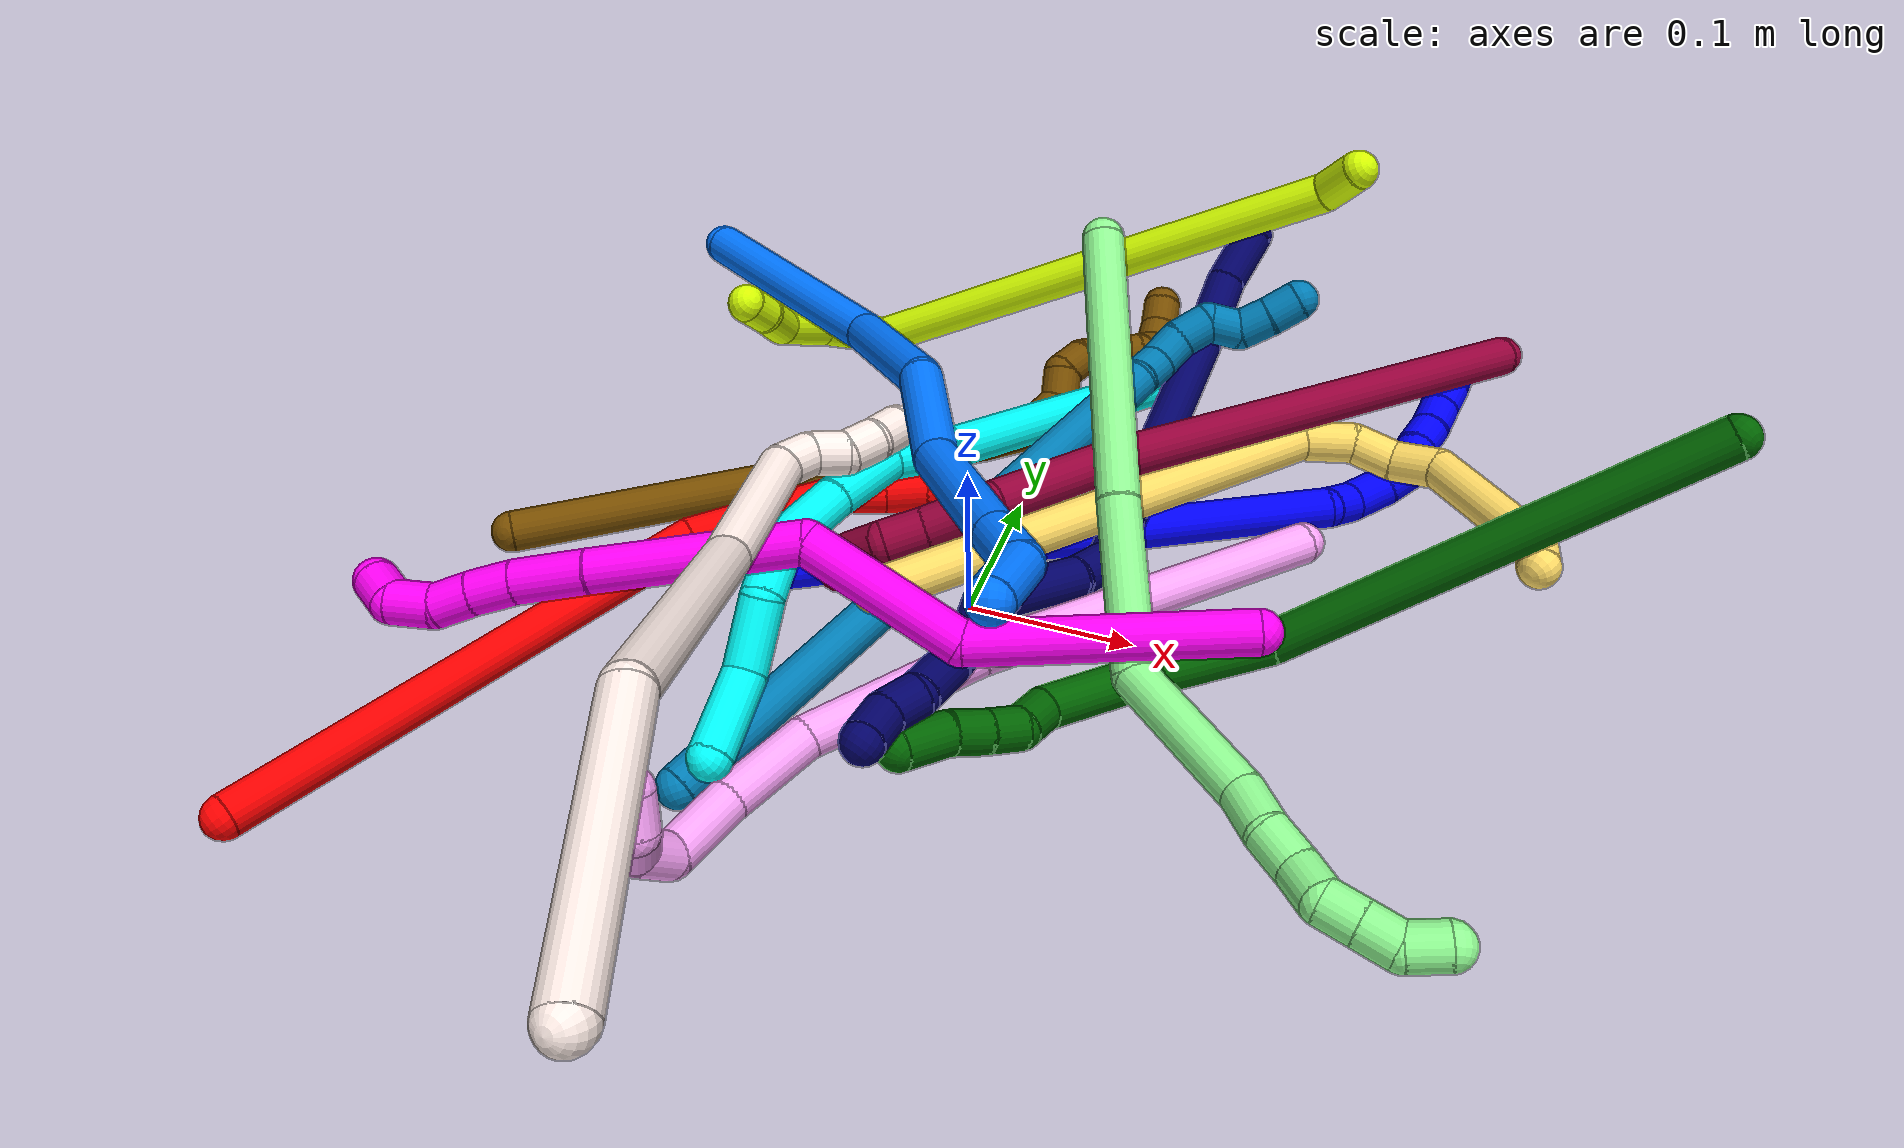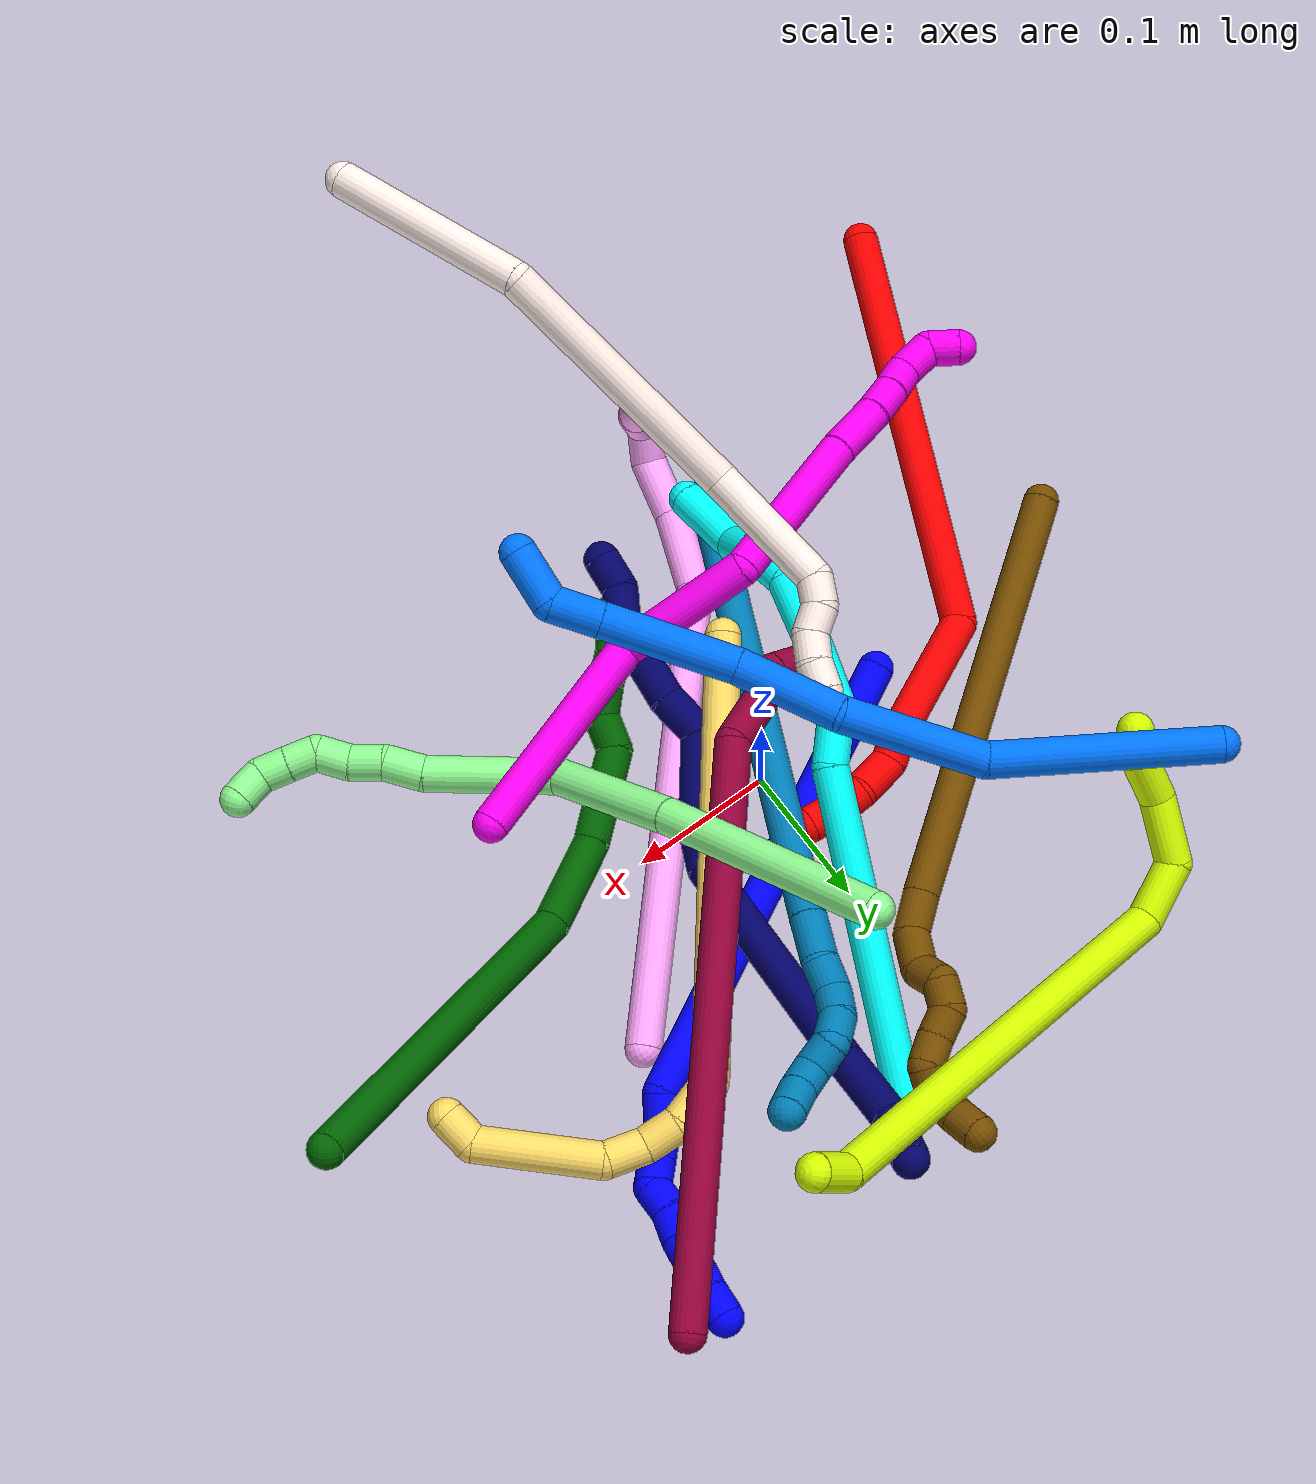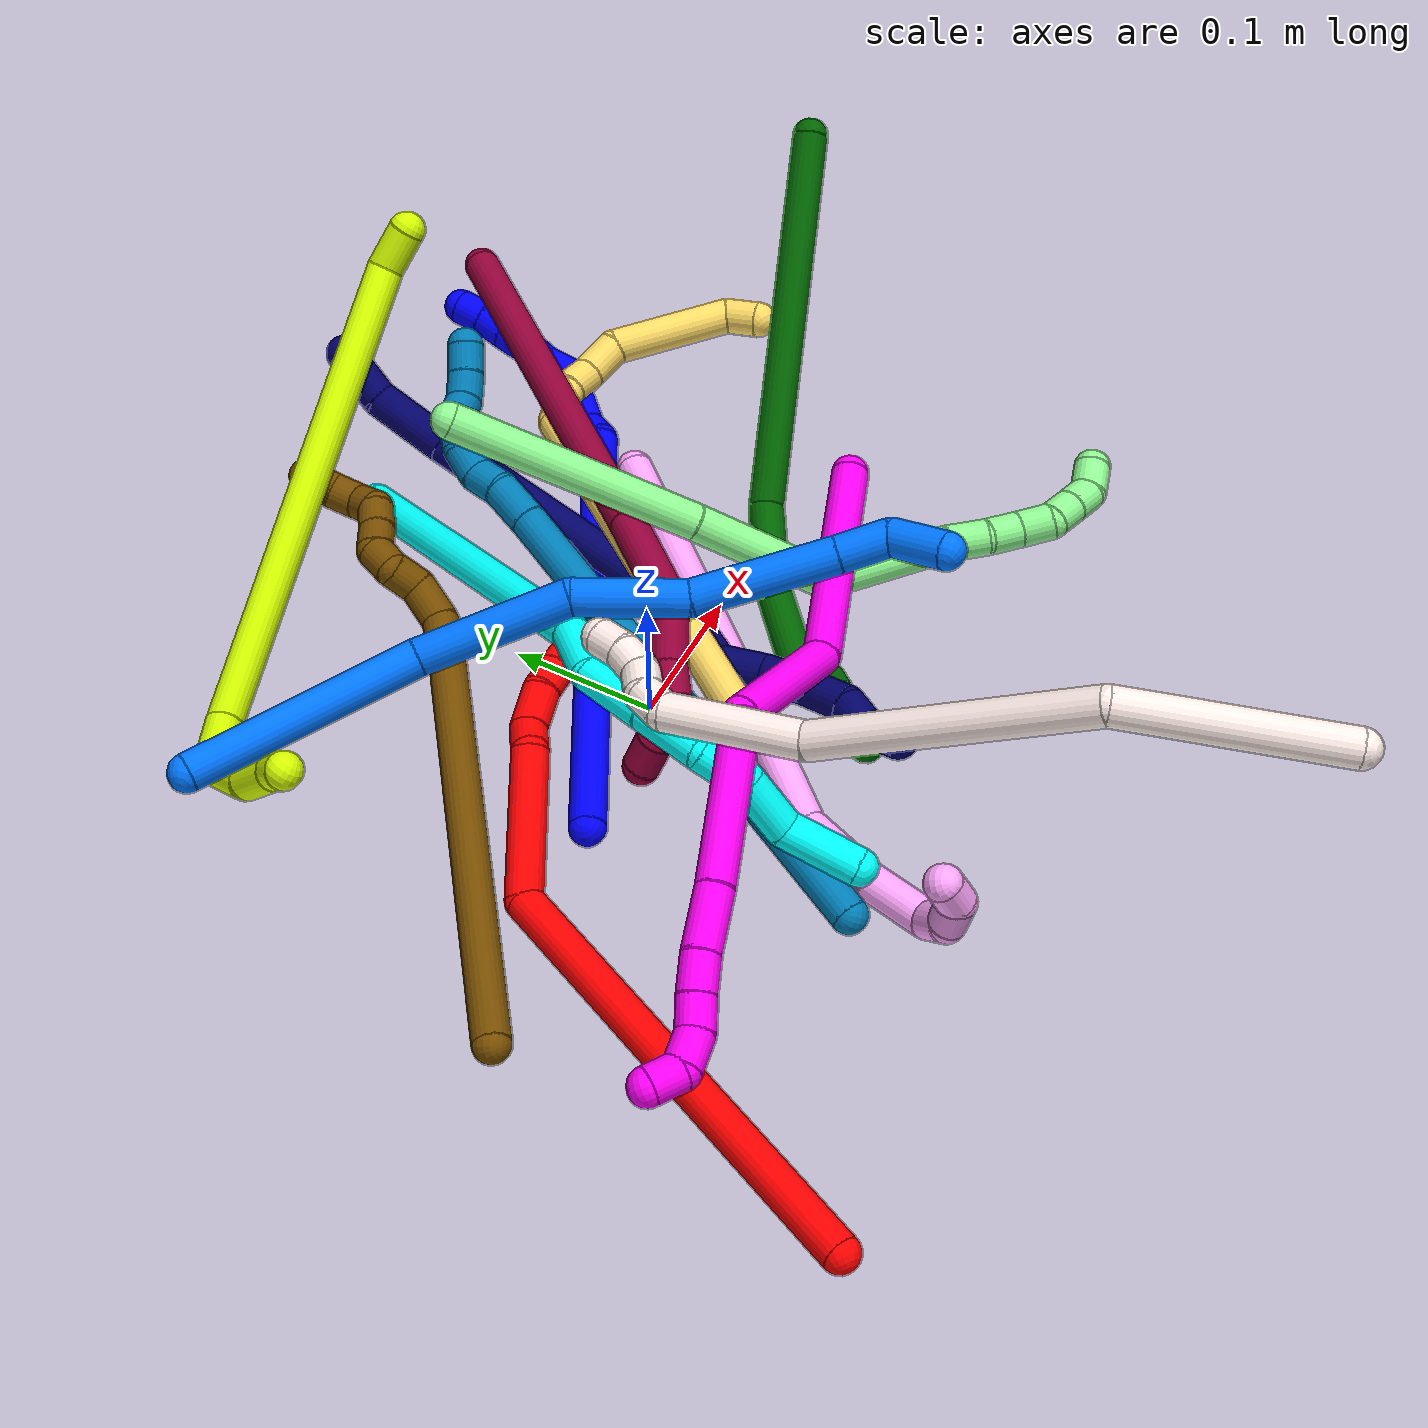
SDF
<sdf version="1.7">
 <world name="default">
  <plugin name="TubeGeneratorPlugin" filename="libtube_generator_plugin.so"/>
  <model name="photoneo_s_sensor">
   <static>1</static>
   <pose>0 0 2 1.57079 1.57079 3.14159</pose>
   <link name="link">
    <inertial><mass>0.1</mass></inertial>
    <sensor name="sensor" type="depth">
     <update_rate>30</update_rate>
     <camera>
      <horizontal_fov>1.22</horizontal_fov>
      <image><width>1920</width><height>1200</height><format>B8G8R8</format></image>
      <clip><near>0.1</near><far>4</far></clip>
      <depth_camera><output>points</output></depth_camera>
     </camera>
     <plugin name="camera_plugin" filename="libgazebo_ros_depth_camera.so">
      <baseline>0.2</baseline>
      <alwaysOn>1</alwaysOn>
      <updateRate>0.0</updateRate>
      <cameraName>camera_ir</cameraName>
      <imageTopicName>/camera/color/image_raw</imageTopicName>
      <cameraInfoTopicName>/camera/color/camera_info</cameraInfoTopicName>
      <depthImageTopicName>/camera/depth/image_raw</depthImageTopicName>
      <depthImageCameraInfoTopicName>/camera/depth/camera_info</depthImageCameraInfoTopicName>
      <pointCloudTopicName>/camera/depth/points</pointCloudTopicName>
      <frameName>fr_optical</frameName>
      <pointCloudCutoff>0.1</pointCloudCutoff>
      <pointCloudCutoffMax>2.0</pointCloudCutoffMax>
      <distortionK1>0</distortionK1>
      <distortionK2>0</distortionK2>
      <distortionK3>0</distortionK3>
      <distortionT1>0</distortionT1>
      <distortionT2>0</distortionT2>
      <CxPrime>0</CxPrime>
      <Cx>0</Cx>
      <Cy>0</Cy>
      <focalLength>0</focalLength>
      <hackBaseline>0</hackBaseline>
     </plugin>
    </sensor>
   </link>
  </model>
  <gravity>0 0 -9.8</gravity>
  <magnetic_field>6e-06 2.3e-05 -4.2e-05</magnetic_field>
  <atmosphere type="adiabatic"/>
  <physics name="default_physics" default="0" type="ode">
   <max_step_size>0.003</max_step_size>
   <real_time_factor>1</real_time_factor>
   <real_time_update_rate>1000</real_time_update_rate>
   <max_contacts>10000</max_contacts>
   <ode>
    <solver>
     <type>quick</type>
     <iters>100</iters>
     <sor>1.3</sor>
     <use_dynamic_moi_rescaling>0</use_dynamic_moi_rescaling>
    </solver>
    <constraints>
     <contact_max_correcting_vel>0</contact_max_correcting_vel>
     <contact_surface_layer>0.001</contact_surface_layer>
     <cfm>0</cfm>
     <erp>0.2</erp>
    </constraints>
   </ode>
  </physics>
  <scene><ambient>0.4 0.4 0.4 1</ambient><background>0.7 0.7 0.7 1</background><shadows>0</shadows></scene>
  <audio><device>default</device></audio>
  <spherical_coordinates>
   <surface_model>EARTH_WGS84</surface_model>
   <latitude_deg>0</latitude_deg>
   <longitude_deg>0</longitude_deg>
   <elevation>0</elevation>
   <heading_deg>0</heading_deg>
  </spherical_coordinates>
  <model name="bin">
   <static>1</static>
   <link name="bottom">
    <collision name="collision-bottom">
     <pose>0 0 -0.01 0 -0 0</pose>
     <geometry><box><size>0.8 0.6 0.02</size></box></geometry>
     <surface>
      <friction><ode><mu>100</mu><mu2>100</mu2></ode></friction>
      <contact><collide_bitmask>65535</collide_bitmask></contact>
     </surface>
    </collision>
   </link>
   <link name="west_wall">
    <collision name="collision-west_wall">
     <pose>-0.41 0 0.1 0 -0 0</pose>
     <geometry><box><size>0.02 0.6 0.2</size></box></geometry>
     <surface>
      <friction><ode><mu>100</mu><mu2>100</mu2></ode></friction>
      <contact><collide_bitmask>65535</collide_bitmask></contact>
     </surface>
    </collision>
   </link>
   <link name="east_wall">
    <collision name="collision-east_wall">
     <pose>0.41 0 0.1 0 -0 0</pose>
     <geometry><box><size>0.02 0.6 0.2</size></box></geometry>
     <surface>
      <friction><ode><mu>100</mu><mu2>100</mu2></ode></friction>
      <contact><collide_bitmask>65535</collide_bitmask></contact>
     </surface>
    </collision>
   </link>
   <link name="south_wall">
    <collision name="collision-south_wall">
     <pose>0 -0.31 0.1 0 -0 0</pose>
     <geometry><box><size>0.8 0.02 0.2</size></box></geometry>
     <surface>
      <friction><ode><mu>100</mu><mu2>100</mu2></ode></friction>
      <contact><collide_bitmask>65535</collide_bitmask></contact>
     </surface>
    </collision>
   </link>
   <link name="north_wall">
    <collision name="collision-north_wall">
     <pose>0 0.31 0.1 0 -0 0</pose>
     <geometry><box><size>0.8 0.02 0.2</size></box></geometry>
     <surface>
      <friction><ode><mu>100</mu><mu2>100</mu2></ode></friction>
      <contact><collide_bitmask>65535</collide_bitmask></contact>
     </surface>
    </collision>
   </link>
  </model>
  <model name="1">
   <static>0</static>
   <link name="1">
    <collision name="collision-cylinder-e_1_1_4">
     <pose>0.131686 0.093437 -0.040959 -1.98393 0.911658 -1.28727</pose>
     <geometry><cylinder><radius>0.0125</radius><length>0.333163</length></cylinder></geometry>
     <surface>
      <friction><ode><mu>1.16</mu><mu2>1.16</mu2><slip1>0</slip1><slip2>0</slip2></ode></friction>
      <contact><ode><kp>1e+06</kp><kd>1</kd><max_vel>0</max_vel><min_depth>0.001</min_depth></ode></contact>
     </surface>
    </collision>
    <visual name="visual-cylinder-e_1_1_4">
     <pose>0.131686 0.093437 -0.040959 -1.98393 0.911658 -1.28727</pose>
     <geometry><cylinder><radius>0.0125</radius><length>0.333163</length></cylinder></geometry>
     <material><ambient>0 0 1 1</ambient></material>
    </visual>
    <collision name="collision-cylinder-e_2_4_5">
     <pose>0.266919 0.196053 -0.085829 -1.9736 0.34158 -0.510544</pose>
     <geometry><cylinder><radius>0.0125</radius><length>0.021177</length></cylinder></geometry>
     <surface>
      <friction><ode><mu>1.16</mu><mu2>1.16</mu2><slip1>0</slip1><slip2>0</slip2></ode></friction>
      <contact><ode><kp>1e+06</kp><kd>1</kd><max_vel>0</max_vel><min_depth>0.001</min_depth></ode></contact>
     </surface>
    </collision>
    <visual name="visual-cylinder-e_2_4_5">
     <pose>0.266919 0.196053 -0.085829 -1.9736 0.34158 -0.510544</pose>
     <geometry><cylinder><radius>0.0125</radius><length>0.021177</length></cylinder></geometry>
     <material><ambient>0 0 1 1</ambient></material>
    </visual>
    <collision name="collision-cylinder-e_3_5_6">
     <pose>0.278493 0.215205 -0.090409 -1.63775 0.676567 -0.719621</pose>
     <geometry><cylinder><radius>0.0125</radius><length>0.025641</length></cylinder></geometry>
     <surface>
      <friction><ode><mu>1.16</mu><mu2>1.16</mu2><slip1>0</slip1><slip2>0</slip2></ode></friction>
      <contact><ode><kp>1e+06</kp><kd>1</kd><max_vel>0</max_vel><min_depth>0.001</min_depth></ode></contact>
     </surface>
    </collision>
    <visual name="visual-cylinder-e_3_5_6">
     <pose>0.278493 0.215205 -0.090409 -1.63775 0.676567 -0.719621</pose>
     <geometry><cylinder><radius>0.0125</radius><length>0.025641</length></cylinder></geometry>
     <material><ambient>0 0 1 1</ambient></material>
    </visual>
    <collision name="collision-cylinder-e_4_6_7">
     <pose>0.293274 0.232394 -0.089522 -1.35852 0.741122 -0.607951</pose>
     <geometry><cylinder><radius>0.0125</radius><length>0.020011</length></cylinder></geometry>
     <surface>
      <friction><ode><mu>1.16</mu><mu2>1.16</mu2><slip1>0</slip1><slip2>0</slip2></ode></friction>
      <contact><ode><kp>1e+06</kp><kd>1</kd><max_vel>0</max_vel><min_depth>0.001</min_depth></ode></contact>
     </surface>
    </collision>
    <visual name="visual-cylinder-e_4_6_7">
     <pose>0.293274 0.232394 -0.089522 -1.35852 0.741122 -0.607951</pose>
     <geometry><cylinder><radius>0.0125</radius><length>0.020011</length></cylinder></geometry>
     <material><ambient>0 0 1 1</ambient></material>
    </visual>
    <collision name="collision-cylinder-e_5_7_8">
     <pose>0.2998 0.249372 -0.085795 -1.35187 -0.022868 0.01834</pose>
     <geometry><cylinder><radius>0.0125</radius><length>0.020008</length></cylinder></geometry>
     <surface>
      <friction><ode><mu>1.16</mu><mu2>1.16</mu2><slip1>0</slip1><slip2>0</slip2></ode></friction>
      <contact><ode><kp>1e+06</kp><kd>1</kd><max_vel>0</max_vel><min_depth>0.001</min_depth></ode></contact>
     </surface>
    </collision>
    <visual name="visual-cylinder-e_5_7_8">
     <pose>0.2998 0.249372 -0.085795 -1.35187 -0.022868 0.01834</pose>
     <geometry><cylinder><radius>0.0125</radius><length>0.020008</length></cylinder></geometry>
     <material><ambient>0 0 1 1</ambient></material>
    </visual>
    <collision name="collision-cylinder-e_6_8_9">
     <pose>0.301806 0.268829 -0.082603 -1.46599 0.225309 -0.203013</pose>
     <geometry><cylinder><radius>0.0125</radius><length>0.02</length></cylinder></geometry>
     <surface>
      <friction><ode><mu>1.16</mu><mu2>1.16</mu2><slip1>0</slip1><slip2>0</slip2></ode></friction>
      <contact><ode><kp>1e+06</kp><kd>1</kd><max_vel>0</max_vel><min_depth>0.001</min_depth></ode></contact>
     </surface>
    </collision>
    <visual name="visual-cylinder-e_6_8_9">
     <pose>0.301806 0.268829 -0.082603 -1.46599 0.225309 -0.203013</pose>
     <geometry><cylinder><radius>0.0125</radius><length>0.02</length></cylinder></geometry>
     <material><ambient>0 0 1 1</ambient></material>
    </visual>
    <collision name="collision-cylinder-e_7_9_10">
     <pose>0.305004 0.28834 -0.079938 -1.40471 0.096594 -0.081768</pose>
     <geometry><cylinder><radius>0.0125</radius><length>0.02</length></cylinder></geometry>
     <surface>
      <friction><ode><mu>1.16</mu><mu2>1.16</mu2><slip1>0</slip1><slip2>0</slip2></ode></friction>
      <contact><ode><kp>1e+06</kp><kd>1</kd><max_vel>0</max_vel><min_depth>0.001</min_depth></ode></contact>
     </surface>
    </collision>
    <visual name="visual-cylinder-e_7_9_10">
     <pose>0.305004 0.28834 -0.079938 -1.40471 0.096594 -0.081768</pose>
     <geometry><cylinder><radius>0.0125</radius><length>0.02</length></cylinder></geometry>
     <material><ambient>0 0 1 1</ambient></material>
    </visual>
    <collision name="collision-cylinder-e_8_10_11">
     <pose>0.307143 0.307946 -0.076622 -1.40182 0.117688 -0.099343</pose>
     <geometry><cylinder><radius>0.0125</radius><length>0.02</length></cylinder></geometry>
     <surface>
      <friction><ode><mu>1.16</mu><mu2>1.16</mu2><slip1>0</slip1><slip2>0</slip2></ode></friction>
      <contact><ode><kp>1e+06</kp><kd>1</kd><max_vel>0</max_vel><min_depth>0.001</min_depth></ode></contact>
     </surface>
    </collision>
    <visual name="visual-cylinder-e_8_10_11">
     <pose>0.307143 0.307946 -0.076622 -1.40182 0.117688 -0.099343</pose>
     <geometry><cylinder><radius>0.0125</radius><length>0.02</length></cylinder></geometry>
     <material><ambient>0 0 1 1</ambient></material>
    </visual>
    <collision name="collision-cylinder-e_9_11_2">
     <pose>0.308352 0.32765 -0.073655 -1.44071 0.003524 -0.003093</pose>
     <geometry><cylinder><radius>0.0125</radius><length>0.02</length></cylinder></geometry>
     <surface>
      <friction><ode><mu>1.16</mu><mu2>1.16</mu2><slip1>0</slip1><slip2>0</slip2></ode></friction>
      <contact><ode><kp>1e+06</kp><kd>1</kd><max_vel>0</max_vel><min_depth>0.001</min_depth></ode></contact>
     </surface>
    </collision>
    <visual name="visual-cylinder-e_9_11_2">
     <pose>0.308352 0.32765 -0.073655 -1.44071 0.003524 -0.003093</pose>
     <geometry><cylinder><radius>0.0125</radius><length>0.02</length></cylinder></geometry>
     <material><ambient>0 0 1 1</ambient></material>
    </visual>
    <collision name="collision-sphere-2">
     <pose>0.308388 0.337566 -0.072358 0 -0 0</pose>
     <geometry><sphere><radius>0.0125</radius></sphere></geometry>
     <surface>
      <friction><ode><mu>1.16</mu><mu2>1.16</mu2><slip1>0</slip1><slip2>0</slip2></ode></friction>
      <contact><ode><kp>1e+06</kp><kd>1</kd><max_vel>0</max_vel><min_depth>0.001</min_depth></ode></contact>
     </surface>
    </collision>
    <visual name="visual-sphere-2">
     <pose>0.308388 0.337566 -0.072358 0 -0 0</pose>
     <geometry><sphere><radius>0.0125</radius></sphere></geometry>
     <material><ambient>0 0 1 1</ambient></material>
    </visual>
    <collision name="collision-sphere-11">
     <pose>0.308317 0.317735 -0.074952 0 -0 0</pose>
     <geometry><sphere><radius>0.0125</radius></sphere></geometry>
     <surface>
      <friction><ode><mu>1.16</mu><mu2>1.16</mu2><slip1>0</slip1><slip2>0</slip2></ode></friction>
      <contact><ode><kp>1e+06</kp><kd>1</kd><max_vel>0</max_vel><min_depth>0.001</min_depth></ode></contact>
     </surface>
    </collision>
    <visual name="visual-sphere-11">
     <pose>0.308317 0.317735 -0.074952 0 -0 0</pose>
     <geometry><sphere><radius>0.0125</radius></sphere></geometry>
     <material><ambient>0 0 1 1</ambient></material>
    </visual>
    <collision name="collision-sphere-10">
     <pose>0.305969 0.298156 -0.078292 0 -0 0</pose>
     <geometry><sphere><radius>0.0125</radius></sphere></geometry>
     <surface>
      <friction><ode><mu>1.16</mu><mu2>1.16</mu2><slip1>0</slip1><slip2>0</slip2></ode></friction>
      <contact><ode><kp>1e+06</kp><kd>1</kd><max_vel>0</max_vel><min_depth>0.001</min_depth></ode></contact>
     </surface>
    </collision>
    <visual name="visual-sphere-10">
     <pose>0.305969 0.298156 -0.078292 0 -0 0</pose>
     <geometry><sphere><radius>0.0125</radius></sphere></geometry>
     <material><ambient>0 0 1 1</ambient></material>
    </visual>
    <collision name="collision-sphere-9">
     <pose>0.30404 0.278523 -0.081583 0 -0 0</pose>
     <geometry><sphere><radius>0.0125</radius></sphere></geometry>
     <surface>
      <friction><ode><mu>1.16</mu><mu2>1.16</mu2><slip1>0</slip1><slip2>0</slip2></ode></friction>
      <contact><ode><kp>1e+06</kp><kd>1</kd><max_vel>0</max_vel><min_depth>0.001</min_depth></ode></contact>
     </surface>
    </collision>
    <visual name="visual-sphere-9">
     <pose>0.30404 0.278523 -0.081583 0 -0 0</pose>
     <geometry><sphere><radius>0.0125</radius></sphere></geometry>
     <material><ambient>0 0 1 1</ambient></material>
    </visual>
    <collision name="collision-sphere-4">
     <pose>0.263372 0.186875 -0.081918 0 -0 0</pose>
     <geometry><sphere><radius>0.0125</radius></sphere></geometry>
     <surface>
      <friction><ode><mu>1.16</mu><mu2>1.16</mu2><slip1>0</slip1><slip2>0</slip2></ode></friction>
      <contact><ode><kp>1e+06</kp><kd>1</kd><max_vel>0</max_vel><min_depth>0.001</min_depth></ode></contact>
     </surface>
    </collision>
    <visual name="visual-sphere-4">
     <pose>0.263372 0.186875 -0.081918 0 -0 0</pose>
     <geometry><sphere><radius>0.0125</radius></sphere></geometry>
     <material><ambient>0 0 1 1</ambient></material>
    </visual>
    <collision name="collision-sphere-1">
     <geometry><sphere><radius>0.0125</radius></sphere></geometry>
     <surface>
      <friction><ode><mu>1.16</mu><mu2>1.16</mu2><slip1>0</slip1><slip2>0</slip2></ode></friction>
      <contact><ode><kp>1e+06</kp><kd>1</kd><max_vel>0</max_vel><min_depth>0.001</min_depth></ode></contact>
     </surface>
    </collision>
    <visual name="visual-sphere-1">
     <geometry><sphere><radius>0.0125</radius></sphere></geometry>
     <material><ambient>0 0 1 1</ambient></material>
    </visual>
    <collision name="collision-sphere-8">
     <pose>0.299572 0.259135 -0.083623 0 -0 0</pose>
     <geometry><sphere><radius>0.0125</radius></sphere></geometry>
     <surface>
      <friction><ode><mu>1.16</mu><mu2>1.16</mu2><slip1>0</slip1><slip2>0</slip2></ode></friction>
      <contact><ode><kp>1e+06</kp><kd>1</kd><max_vel>0</max_vel><min_depth>0.001</min_depth></ode></contact>
     </surface>
    </collision>
    <visual name="visual-sphere-8">
     <pose>0.299572 0.259135 -0.083623 0 -0 0</pose>
     <geometry><sphere><radius>0.0125</radius></sphere></geometry>
     <material><ambient>0 0 1 1</ambient></material>
    </visual>
    <collision name="collision-sphere-5">
     <pose>0.270466 0.205231 -0.08974 0 -0 0</pose>
     <geometry><sphere><radius>0.0125</radius></sphere></geometry>
     <surface>
      <friction><ode><mu>1.16</mu><mu2>1.16</mu2><slip1>0</slip1><slip2>0</slip2></ode></friction>
      <contact><ode><kp>1e+06</kp><kd>1</kd><max_vel>0</max_vel><min_depth>0.001</min_depth></ode></contact>
     </surface>
    </collision>
    <visual name="visual-sphere-5">
     <pose>0.270466 0.205231 -0.08974 0 -0 0</pose>
     <geometry><sphere><radius>0.0125</radius></sphere></geometry>
     <material><ambient>0 0 1 1</ambient></material>
    </visual>
    <collision name="collision-sphere-6">
     <pose>0.28652 0.225179 -0.091077 0 -0 0</pose>
     <geometry><sphere><radius>0.0125</radius></sphere></geometry>
     <surface>
      <friction><ode><mu>1.16</mu><mu2>1.16</mu2><slip1>0</slip1><slip2>0</slip2></ode></friction>
      <contact><ode><kp>1e+06</kp><kd>1</kd><max_vel>0</max_vel><min_depth>0.001</min_depth></ode></contact>
     </surface>
    </collision>
    <visual name="visual-sphere-6">
     <pose>0.28652 0.225179 -0.091077 0 -0 0</pose>
     <geometry><sphere><radius>0.0125</radius></sphere></geometry>
     <material><ambient>0 0 1 1</ambient></material>
    </visual>
    <collision name="collision-sphere-7">
     <pose>0.300029 0.239609 -0.087967 0 -0 0</pose>
     <geometry><sphere><radius>0.0125</radius></sphere></geometry>
     <surface>
      <friction><ode><mu>1.16</mu><mu2>1.16</mu2><slip1>0</slip1><slip2>0</slip2></ode></friction>
      <contact><ode><kp>1e+06</kp><kd>1</kd><max_vel>0</max_vel><min_depth>0.001</min_depth></ode></contact>
     </surface>
    </collision>
    <visual name="visual-sphere-7">
     <pose>0.300029 0.239609 -0.087967 0 -0 0</pose>
     <geometry><sphere><radius>0.0125</radius></sphere></geometry>
     <material><ambient>0 0 1 1</ambient></material>
    </visual>
    <inertial>
     <pose>0.185959 0.14859 -0.055092 0 -0 0</pose>
     <mass>0.5</mass>
     <inertia>
      <ixx>-0.001258</ixx>
      <ixy>0</ixy>
      <ixz>0</ixz>
      <iyy>1e-05</iyy>
      <iyz>0</iyz>
      <izz>-0.004203</izz>
     </inertia>
    </inertial>
   </link>
   <pose>-0.109823 -0.014762 0.011486 -0.044342 -0.350006 -0.099539</pose>
  </model>
  <model name="2">
   <static>0</static>
   <link name="2">
    <collision name="collision-cylinder-e_1_1_4">
     <pose>0.009948 -0.061134 -0.138856 2.72686 0.065473 0.308833</pose>
     <geometry><cylinder><radius>0.0125</radius><length>0.304088</length></cylinder></geometry>
     <surface>
      <friction><ode><mu>1.16</mu><mu2>1.16</mu2><slip1>0</slip1><slip2>0</slip2></ode></friction>
      <contact><ode><kp>1e+06</kp><kd>1</kd><max_vel>0</max_vel><min_depth>0.001</min_depth></ode></contact>
     </surface>
    </collision>
    <visual name="visual-cylinder-e_1_1_4">
     <pose>0.009948 -0.061134 -0.138856 2.72686 0.065473 0.308833</pose>
     <geometry><cylinder><radius>0.0125</radius><length>0.304088</length></cylinder></geometry>
     <material><ambient>1 0 0 1</ambient></material>
    </visual>
    <collision name="collision-cylinder-e_2_4_5">
     <pose>0.03818 -0.110746 -0.323405 -2.89459 0.370146 -1.97062</pose>
     <geometry><cylinder><radius>0.0125</radius><length>0.101091</length></cylinder></geometry>
     <surface>
      <friction><ode><mu>1.16</mu><mu2>1.16</mu2><slip1>0</slip1><slip2>0</slip2></ode></friction>
      <contact><ode><kp>1e+06</kp><kd>1</kd><max_vel>0</max_vel><min_depth>0.001</min_depth></ode></contact>
     </surface>
    </collision>
    <visual name="visual-cylinder-e_2_4_5">
     <pose>0.03818 -0.110746 -0.323405 -2.89459 0.370146 -1.97062</pose>
     <geometry><cylinder><radius>0.0125</radius><length>0.101091</length></cylinder></geometry>
     <material><ambient>1 0 0 1</ambient></material>
    </visual>
    <collision name="collision-cylinder-e_3_5_6">
     <pose>0.063192 -0.10125 -0.377853 2.91427 0.642512 2.4807</pose>
     <geometry><cylinder><radius>0.0125</radius><length>0.022451</length></cylinder></geometry>
     <surface>
      <friction><ode><mu>1.16</mu><mu2>1.16</mu2><slip1>0</slip1><slip2>0</slip2></ode></friction>
      <contact><ode><kp>1e+06</kp><kd>1</kd><max_vel>0</max_vel><min_depth>0.001</min_depth></ode></contact>
     </surface>
    </collision>
    <visual name="visual-cylinder-e_3_5_6">
     <pose>0.063192 -0.10125 -0.377853 2.91427 0.642512 2.4807</pose>
     <geometry><cylinder><radius>0.0125</radius><length>0.022451</length></cylinder></geometry>
     <material><ambient>1 0 0 1</ambient></material>
    </visual>
    <collision name="collision-cylinder-e_4_6_7">
     <pose>0.077637 -0.097899 -0.397832 -2.6948 0.555217 -1.79547</pose>
     <geometry><cylinder><radius>0.0125</radius><length>0.029288</length></cylinder></geometry>
     <surface>
      <friction><ode><mu>1.16</mu><mu2>1.16</mu2><slip1>0</slip1><slip2>0</slip2></ode></friction>
      <contact><ode><kp>1e+06</kp><kd>1</kd><max_vel>0</max_vel><min_depth>0.001</min_depth></ode></contact>
     </surface>
    </collision>
    <visual name="visual-cylinder-e_4_6_7">
     <pose>0.077637 -0.097899 -0.397832 -2.6948 0.555217 -1.79547</pose>
     <geometry><cylinder><radius>0.0125</radius><length>0.029288</length></cylinder></geometry>
     <material><ambient>1 0 0 1</ambient></material>
    </visual>
    <collision name="collision-cylinder-e_5_7_8">
     <pose>0.093059 -0.089214 -0.414996 -2.6336 0.847512 -2.09717</pose>
     <geometry><cylinder><radius>0.0125</radius><length>0.020548</length></cylinder></geometry>
     <surface>
      <friction><ode><mu>1.16</mu><mu2>1.16</mu2><slip1>0</slip1><slip2>0</slip2></ode></friction>
      <contact><ode><kp>1e+06</kp><kd>1</kd><max_vel>0</max_vel><min_depth>0.001</min_depth></ode></contact>
     </surface>
    </collision>
    <visual name="visual-cylinder-e_5_7_8">
     <pose>0.093059 -0.089214 -0.414996 -2.6336 0.847512 -2.09717</pose>
     <geometry><cylinder><radius>0.0125</radius><length>0.020548</length></cylinder></geometry>
     <material><ambient>1 0 0 1</ambient></material>
    </visual>
    <collision name="collision-cylinder-e_6_8_2">
     <pose>0.108799 -0.080595 -0.426778 -2.40366 0.794465 -1.65227</pose>
     <geometry><cylinder><radius>0.0125</radius><length>0.022533</length></cylinder></geometry>
     <surface>
      <friction><ode><mu>1.16</mu><mu2>1.16</mu2><slip1>0</slip1><slip2>0</slip2></ode></friction>
      <contact><ode><kp>1e+06</kp><kd>1</kd><max_vel>0</max_vel><min_depth>0.001</min_depth></ode></contact>
     </surface>
    </collision>
    <visual name="visual-cylinder-e_6_8_2">
     <pose>0.108799 -0.080595 -0.426778 -2.40366 0.794465 -1.65227</pose>
     <geometry><cylinder><radius>0.0125</radius><length>0.022533</length></cylinder></geometry>
     <material><ambient>1 0 0 1</ambient></material>
    </visual>
    <collision name="collision-sphere-2">
     <pose>0.116838 -0.075285 -0.432618 0 -0 0</pose>
     <geometry><sphere><radius>0.0125</radius></sphere></geometry>
     <surface>
      <friction><ode><mu>1.16</mu><mu2>1.16</mu2><slip1>0</slip1><slip2>0</slip2></ode></friction>
      <contact><ode><kp>1e+06</kp><kd>1</kd><max_vel>0</max_vel><min_depth>0.001</min_depth></ode></contact>
     </surface>
    </collision>
    <visual name="visual-sphere-2">
     <pose>0.116838 -0.075285 -0.432618 0 -0 0</pose>
     <geometry><sphere><radius>0.0125</radius></sphere></geometry>
     <material><ambient>1 0 0 1</ambient></material>
    </visual>
    <collision name="collision-sphere-4">
     <pose>0.019895 -0.122267 -0.277713 0 -0 0</pose>
     <geometry><sphere><radius>0.0125</radius></sphere></geometry>
     <surface>
      <friction><ode><mu>1.16</mu><mu2>1.16</mu2><slip1>0</slip1><slip2>0</slip2></ode></friction>
      <contact><ode><kp>1e+06</kp><kd>1</kd><max_vel>0</max_vel><min_depth>0.001</min_depth></ode></contact>
     </surface>
    </collision>
    <visual name="visual-sphere-4">
     <pose>0.019895 -0.122267 -0.277713 0 -0 0</pose>
     <geometry><sphere><radius>0.0125</radius></sphere></geometry>
     <material><ambient>1 0 0 1</ambient></material>
    </visual>
    <collision name="collision-sphere-1">
     <geometry><sphere><radius>0.0125</radius></sphere></geometry>
     <surface>
      <friction><ode><mu>1.16</mu><mu2>1.16</mu2><slip1>0</slip1><slip2>0</slip2></ode></friction>
      <contact><ode><kp>1e+06</kp><kd>1</kd><max_vel>0</max_vel><min_depth>0.001</min_depth></ode></contact>
     </surface>
    </collision>
    <visual name="visual-sphere-1">
     <geometry><sphere><radius>0.0125</radius></sphere></geometry>
     <material><ambient>1 0 0 1</ambient></material>
    </visual>
    <collision name="collision-sphere-8">
     <pose>0.10076 -0.085906 -0.420937 0 -0 0</pose>
     <geometry><sphere><radius>0.0125</radius></sphere></geometry>
     <surface>
      <friction><ode><mu>1.16</mu><mu2>1.16</mu2><slip1>0</slip1><slip2>0</slip2></ode></friction>
      <contact><ode><kp>1e+06</kp><kd>1</kd><max_vel>0</max_vel><min_depth>0.001</min_depth></ode></contact>
     </surface>
    </collision>
    <visual name="visual-sphere-8">
     <pose>0.10076 -0.085906 -0.420937 0 -0 0</pose>
     <geometry><sphere><radius>0.0125</radius></sphere></geometry>
     <material><ambient>1 0 0 1</ambient></material>
    </visual>
    <collision name="collision-sphere-5">
     <pose>0.056465 -0.099225 -0.369097 0 -0 0</pose>
     <geometry><sphere><radius>0.0125</radius></sphere></geometry>
     <surface>
      <friction><ode><mu>1.16</mu><mu2>1.16</mu2><slip1>0</slip1><slip2>0</slip2></ode></friction>
      <contact><ode><kp>1e+06</kp><kd>1</kd><max_vel>0</max_vel><min_depth>0.001</min_depth></ode></contact>
     </surface>
    </collision>
    <visual name="visual-sphere-5">
     <pose>0.056465 -0.099225 -0.369097 0 -0 0</pose>
     <geometry><sphere><radius>0.0125</radius></sphere></geometry>
     <material><ambient>1 0 0 1</ambient></material>
    </visual>
    <collision name="collision-sphere-6">
     <pose>0.069918 -0.103276 -0.386609 0 -0 0</pose>
     <geometry><sphere><radius>0.0125</radius></sphere></geometry>
     <surface>
      <friction><ode><mu>1.16</mu><mu2>1.16</mu2><slip1>0</slip1><slip2>0</slip2></ode></friction>
      <contact><ode><kp>1e+06</kp><kd>1</kd><max_vel>0</max_vel><min_depth>0.001</min_depth></ode></contact>
     </surface>
    </collision>
    <visual name="visual-sphere-6">
     <pose>0.069918 -0.103276 -0.386609 0 -0 0</pose>
     <geometry><sphere><radius>0.0125</radius></sphere></geometry>
     <material><ambient>1 0 0 1</ambient></material>
    </visual>
    <collision name="collision-sphere-7">
     <pose>0.085357 -0.092522 -0.409054 0 -0 0</pose>
     <geometry><sphere><radius>0.0125</radius></sphere></geometry>
     <surface>
      <friction><ode><mu>1.16</mu><mu2>1.16</mu2><slip1>0</slip1><slip2>0</slip2></ode></friction>
      <contact><ode><kp>1e+06</kp><kd>1</kd><max_vel>0</max_vel><min_depth>0.001</min_depth></ode></contact>
     </surface>
    </collision>
    <visual name="visual-sphere-7">
     <pose>0.085357 -0.092522 -0.409054 0 -0 0</pose>
     <geometry><sphere><radius>0.0125</radius></sphere></geometry>
     <material><ambient>1 0 0 1</ambient></material>
    </visual>
    <inertial>
     <pose>0.029882 -0.07715 -0.226394 0 -0 0</pose>
     <mass>0.5</mass>
     <inertia>
      <ixx>0.002846</ixx>
      <ixy>0</ixy>
      <ixz>0</ixz>
      <iyy>-0.001361</iyy>
      <iyz>0</iyz>
      <izz>0.000698</izz>
     </inertia>
    </inertial>
   </link>
   <pose>-0.302105 -0.284244 0.01348 2.03114 0.689516 -0.345624</pose>
  </model>
  <model name="3">
   <static>0</static>
   <link name="3">
    <collision name="collision-cylinder-e_1_1_4">
     <pose>-0.035295 -0.068706 -0.090647 2.49302 -0.300882 -0.847282</pose>
     <geometry><cylinder><radius>0.0125</radius><length>0.238185</length></cylinder></geometry>
     <surface>
      <friction><ode><mu>1.16</mu><mu2>1.16</mu2><slip1>0</slip1><slip2>0</slip2></ode></friction>
      <contact><ode><kp>1e+06</kp><kd>1</kd><max_vel>0</max_vel><min_depth>0.001</min_depth></ode></contact>
     </surface>
    </collision>
    <visual name="visual-cylinder-e_1_1_4">
     <pose>-0.035295 -0.068706 -0.090647 2.49302 -0.300882 -0.847282</pose>
     <geometry><cylinder><radius>0.0125</radius><length>0.238185</length></cylinder></geometry>
     <material><ambient>0.003922 1 0.996078 1</ambient></material>
    </visual>
    <collision name="collision-cylinder-e_2_4_5">
     <pose>-0.07017 -0.152527 -0.19514 2.31239 0.020465 0.046492</pose>
     <geometry><cylinder><radius>0.0125</radius><length>0.041006</length></cylinder></geometry>
     <surface>
      <friction><ode><mu>1.16</mu><mu2>1.16</mu2><slip1>0</slip1><slip2>0</slip2></ode></friction>
      <contact><ode><kp>1e+06</kp><kd>1</kd><max_vel>0</max_vel><min_depth>0.001</min_depth></ode></contact>
     </surface>
    </collision>
    <visual name="visual-cylinder-e_2_4_5">
     <pose>-0.07017 -0.152527 -0.19514 2.31239 0.020465 0.046492</pose>
     <geometry><cylinder><radius>0.0125</radius><length>0.041006</length></cylinder></geometry>
     <material><ambient>0.003922 1 0.996078 1</ambient></material>
    </visual>
    <collision name="collision-cylinder-e_3_5_6">
     <pose>-0.080409 -0.1846 -0.223397 2.27517 -0.446683 -0.912972</pose>
     <geometry><cylinder><radius>0.0125</radius><length>0.049347</length></cylinder></geometry>
     <surface>
      <friction><ode><mu>1.16</mu><mu2>1.16</mu2><slip1>0</slip1><slip2>0</slip2></ode></friction>
      <contact><ode><kp>1e+06</kp><kd>1</kd><max_vel>0</max_vel><min_depth>0.001</min_depth></ode></contact>
     </surface>
    </collision>
    <visual name="visual-cylinder-e_3_5_6">
     <pose>-0.080409 -0.1846 -0.223397 2.27517 -0.446683 -0.912972</pose>
     <geometry><cylinder><radius>0.0125</radius><length>0.049347</length></cylinder></geometry>
     <material><ambient>0.003922 1 0.996078 1</ambient></material>
    </visual>
    <collision name="collision-cylinder-e_4_6_7">
     <pose>-0.101999 -0.217835 -0.249831 2.20705 -0.495258 -0.929032</pose>
     <geometry><cylinder><radius>0.0125</radius><length>0.046003</length></cylinder></geometry>
     <surface>
      <friction><ode><mu>1.16</mu><mu2>1.16</mu2><slip1>0</slip1><slip2>0</slip2></ode></friction>
      <contact><ode><kp>1e+06</kp><kd>1</kd><max_vel>0</max_vel><min_depth>0.001</min_depth></ode></contact>
     </surface>
    </collision>
    <visual name="visual-cylinder-e_4_6_7">
     <pose>-0.101999 -0.217835 -0.249831 2.20705 -0.495258 -0.929032</pose>
     <geometry><cylinder><radius>0.0125</radius><length>0.046003</length></cylinder></geometry>
     <material><ambient>0.003922 1 0.996078 1</ambient></material>
    </visual>
    <collision name="collision-cylinder-e_5_7_8">
     <pose>-0.12409 -0.245893 -0.263087 1.67488 -0.755645 -0.829868</pose>
     <geometry><cylinder><radius>0.0125</radius><length>0.032548</length></cylinder></geometry>
     <surface>
      <friction><ode><mu>1.16</mu><mu2>1.16</mu2><slip1>0</slip1><slip2>0</slip2></ode></friction>
      <contact><ode><kp>1e+06</kp><kd>1</kd><max_vel>0</max_vel><min_depth>0.001</min_depth></ode></contact>
     </surface>
    </collision>
    <visual name="visual-cylinder-e_5_7_8">
     <pose>-0.12409 -0.245893 -0.263087 1.67488 -0.755645 -0.829868</pose>
     <geometry><cylinder><radius>0.0125</radius><length>0.032548</length></cylinder></geometry>
     <material><ambient>0.003922 1 0.996078 1</ambient></material>
    </visual>
    <collision name="collision-cylinder-e_6_8_9">
     <pose>-0.145313 -0.274306 -0.257548 1.18424 -0.510776 -0.347689</pose>
     <geometry><cylinder><radius>0.0125</radius><length>0.041168</length></cylinder></geometry>
     <surface>
      <friction><ode><mu>1.16</mu><mu2>1.16</mu2><slip1>0</slip1><slip2>0</slip2></ode></friction>
      <contact><ode><kp>1e+06</kp><kd>1</kd><max_vel>0</max_vel><min_depth>0.001</min_depth></ode></contact>
     </surface>
    </collision>
    <visual name="visual-cylinder-e_6_8_9">
     <pose>-0.145313 -0.274306 -0.257548 1.18424 -0.510776 -0.347689</pose>
     <geometry><cylinder><radius>0.0125</radius><length>0.041168</length></cylinder></geometry>
     <material><ambient>0.003922 1 0.996078 1</ambient></material>
    </visual>
    <collision name="collision-cylinder-e_7_9_2">
     <pose>-0.173861 -0.308124 -0.256453 1.88973 -0.79596 -1.0535</pose>
     <geometry><cylinder><radius>0.0125</radius><length>0.051742</length></cylinder></geometry>
     <surface>
      <friction><ode><mu>1.16</mu><mu2>1.16</mu2><slip1>0</slip1><slip2>0</slip2></ode></friction>
      <contact><ode><kp>1e+06</kp><kd>1</kd><max_vel>0</max_vel><min_depth>0.001</min_depth></ode></contact>
     </surface>
    </collision>
    <visual name="visual-cylinder-e_7_9_2">
     <pose>-0.173861 -0.308124 -0.256453 1.88973 -0.79596 -1.0535</pose>
     <geometry><cylinder><radius>0.0125</radius><length>0.051742</length></cylinder></geometry>
     <material><ambient>0.003922 1 0.996078 1</ambient></material>
    </visual>
    <collision name="collision-sphere-2">
     <pose>-0.192347 -0.325311 -0.262128 0 -0 0</pose>
     <geometry><sphere><radius>0.0125</radius></sphere></geometry>
     <surface>
      <friction><ode><mu>1.16</mu><mu2>1.16</mu2><slip1>0</slip1><slip2>0</slip2></ode></friction>
      <contact><ode><kp>1e+06</kp><kd>1</kd><max_vel>0</max_vel><min_depth>0.001</min_depth></ode></contact>
     </surface>
    </collision>
    <visual name="visual-sphere-2">
     <pose>-0.192347 -0.325311 -0.262128 0 -0 0</pose>
     <geometry><sphere><radius>0.0125</radius></sphere></geometry>
     <material><ambient>0.003922 1 0.996078 1</ambient></material>
    </visual>
    <collision name="collision-sphere-9">
     <pose>-0.155376 -0.290938 -0.250778 0 -0 0</pose>
     <geometry><sphere><radius>0.0125</radius></sphere></geometry>
     <surface>
      <friction><ode><mu>1.16</mu><mu2>1.16</mu2><slip1>0</slip1><slip2>0</slip2></ode></friction>
      <contact><ode><kp>1e+06</kp><kd>1</kd><max_vel>0</max_vel><min_depth>0.001</min_depth></ode></contact>
     </surface>
    </collision>
    <visual name="visual-sphere-9">
     <pose>-0.155376 -0.290938 -0.250778 0 -0 0</pose>
     <geometry><sphere><radius>0.0125</radius></sphere></geometry>
     <material><ambient>0.003922 1 0.996078 1</ambient></material>
    </visual>
    <collision name="collision-sphere-4">
     <pose>-0.070589 -0.137411 -0.181294 0 -0 0</pose>
     <geometry><sphere><radius>0.0125</radius></sphere></geometry>
     <surface>
      <friction><ode><mu>1.16</mu><mu2>1.16</mu2><slip1>0</slip1><slip2>0</slip2></ode></friction>
      <contact><ode><kp>1e+06</kp><kd>1</kd><max_vel>0</max_vel><min_depth>0.001</min_depth></ode></contact>
     </surface>
    </collision>
    <visual name="visual-sphere-4">
     <pose>-0.070589 -0.137411 -0.181294 0 -0 0</pose>
     <geometry><sphere><radius>0.0125</radius></sphere></geometry>
     <material><ambient>0.003922 1 0.996078 1</ambient></material>
    </visual>
    <collision name="collision-sphere-1">
     <geometry><sphere><radius>0.0125</radius></sphere></geometry>
     <surface>
      <friction><ode><mu>1.16</mu><mu2>1.16</mu2><slip1>0</slip1><slip2>0</slip2></ode></friction>
      <contact><ode><kp>1e+06</kp><kd>1</kd><max_vel>0</max_vel><min_depth>0.001</min_depth></ode></contact>
     </surface>
    </collision>
    <visual name="visual-sphere-1">
     <geometry><sphere><radius>0.0125</radius></sphere></geometry>
     <material><ambient>0.003922 1 0.996078 1</ambient></material>
    </visual>
    <collision name="collision-sphere-8">
     <pose>-0.13525 -0.257674 -0.264318 0 -0 0</pose>
     <geometry><sphere><radius>0.0125</radius></sphere></geometry>
     <surface>
      <friction><ode><mu>1.16</mu><mu2>1.16</mu2><slip1>0</slip1><slip2>0</slip2></ode></friction>
      <contact><ode><kp>1e+06</kp><kd>1</kd><max_vel>0</max_vel><min_depth>0.001</min_depth></ode></contact>
     </surface>
    </collision>
    <visual name="visual-sphere-8">
     <pose>-0.13525 -0.257674 -0.264318 0 -0 0</pose>
     <geometry><sphere><radius>0.0125</radius></sphere></geometry>
     <material><ambient>0.003922 1 0.996078 1</ambient></material>
    </visual>
    <collision name="collision-sphere-5">
     <pose>-0.06975 -0.167643 -0.208987 0 -0 0</pose>
     <geometry><sphere><radius>0.0125</radius></sphere></geometry>
     <surface>
      <friction><ode><mu>1.16</mu><mu2>1.16</mu2><slip1>0</slip1><slip2>0</slip2></ode></friction>
      <contact><ode><kp>1e+06</kp><kd>1</kd><max_vel>0</max_vel><min_depth>0.001</min_depth></ode></contact>
     </surface>
    </collision>
    <visual name="visual-sphere-5">
     <pose>-0.06975 -0.167643 -0.208987 0 -0 0</pose>
     <geometry><sphere><radius>0.0125</radius></sphere></geometry>
     <material><ambient>0.003922 1 0.996078 1</ambient></material>
    </visual>
    <collision name="collision-sphere-6">
     <pose>-0.091067 -0.201557 -0.237806 0 -0 0</pose>
     <geometry><sphere><radius>0.0125</radius></sphere></geometry>
     <surface>
      <friction><ode><mu>1.16</mu><mu2>1.16</mu2><slip1>0</slip1><slip2>0</slip2></ode></friction>
      <contact><ode><kp>1e+06</kp><kd>1</kd><max_vel>0</max_vel><min_depth>0.001</min_depth></ode></contact>
     </surface>
    </collision>
    <visual name="visual-sphere-6">
     <pose>-0.091067 -0.201557 -0.237806 0 -0 0</pose>
     <geometry><sphere><radius>0.0125</radius></sphere></geometry>
     <material><ambient>0.003922 1 0.996078 1</ambient></material>
    </visual>
    <collision name="collision-sphere-7">
     <pose>-0.11293 -0.234113 -0.261856 0 -0 0</pose>
     <geometry><sphere><radius>0.0125</radius></sphere></geometry>
     <surface>
      <friction><ode><mu>1.16</mu><mu2>1.16</mu2><slip1>0</slip1><slip2>0</slip2></ode></friction>
      <contact><ode><kp>1e+06</kp><kd>1</kd><max_vel>0</max_vel><min_depth>0.001</min_depth></ode></contact>
     </surface>
    </collision>
    <visual name="visual-sphere-7">
     <pose>-0.11293 -0.234113 -0.261856 0 -0 0</pose>
     <geometry><sphere><radius>0.0125</radius></sphere></geometry>
     <material><ambient>0.003922 1 0.996078 1</ambient></material>
    </visual>
    <inertial>
     <pose>-0.077923 -0.153978 -0.16909 0 -0 0</pose>
     <mass>0.5</mass>
     <inertia>
      <ixx>-0.000106</ixx>
      <ixy>0</ixy>
      <ixz>0</ixz>
      <iyy>-0.001308</iyy>
      <iyz>0</iyz>
      <izz>0.001036</izz>
     </inertia>
    </inertial>
   </link>
   <pose>0.065842 0.251199 0.01249 2.55295 -0.070994 2.39325</pose>
  </model>
  <model name="4">
   <static>0</static>
   <link name="4">
    <collision name="collision-cylinder-e_1_1_4">
     <pose>-0.058887 -0.071931 0.061845 0.860649 -0.555546 -0.260291</pose>
     <geometry><cylinder><radius>0.0125</radius><length>0.223309</length></cylinder></geometry>
     <surface>
      <friction><ode><mu>1.16</mu><mu2>1.16</mu2><slip1>0</slip1><slip2>0</slip2></ode></friction>
      <contact><ode><kp>1e+06</kp><kd>1</kd><max_vel>0</max_vel><min_depth>0.001</min_depth></ode></contact>
     </surface>
    </collision>
    <visual name="visual-cylinder-e_1_1_4">
     <pose>-0.058887 -0.071931 0.061845 0.860649 -0.555546 -0.260291</pose>
     <geometry><cylinder><radius>0.0125</radius><length>0.223309</length></cylinder></geometry>
     <material><ambient>1 0.65098 0.996078 1</ambient></material>
    </visual>
    <collision name="collision-cylinder-e_2_4_5">
     <pose>-0.143158 -0.183569 0.149204 0.999692 -0.493449 -0.273363</pose>
     <geometry><cylinder><radius>0.0125</radius><length>0.107179</length></cylinder></geometry>
     <surface>
      <friction><ode><mu>1.16</mu><mu2>1.16</mu2><slip1>0</slip1><slip2>0</slip2></ode></friction>
      <contact><ode><kp>1e+06</kp><kd>1</kd><max_vel>0</max_vel><min_depth>0.001</min_depth></ode></contact>
     </surface>
    </collision>
    <visual name="visual-cylinder-e_2_4_5">
     <pose>-0.143158 -0.183569 0.149204 0.999692 -0.493449 -0.273363</pose>
     <geometry><cylinder><radius>0.0125</radius><length>0.107179</length></cylinder></geometry>
     <material><ambient>1 0.65098 0.996078 1</ambient></material>
    </visual>
    <collision name="collision-cylinder-e_3_5_6">
     <pose>-0.17367 -0.243271 0.194632 0.787364 -0.179771 -0.074838</pose>
     <geometry><cylinder><radius>0.0125</radius><length>0.057367</length></cylinder></geometry>
     <surface>
      <friction><ode><mu>1.16</mu><mu2>1.16</mu2><slip1>0</slip1><slip2>0</slip2></ode></friction>
      <contact><ode><kp>1e+06</kp><kd>1</kd><max_vel>0</max_vel><min_depth>0.001</min_depth></ode></contact>
     </surface>
    </collision>
    <visual name="visual-cylinder-e_3_5_6">
     <pose>-0.17367 -0.243271 0.194632 0.787364 -0.179771 -0.074838</pose>
     <geometry><cylinder><radius>0.0125</radius><length>0.057367</length></cylinder></geometry>
     <material><ambient>1 0.65098 0.996078 1</ambient></material>
    </visual>
    <collision name="collision-cylinder-e_4_6_7">
     <pose>-0.180392 -0.277903 0.231272 0.718977 -0.071548 -0.026899</pose>
     <geometry><cylinder><radius>0.0125</radius><length>0.044563</length></cylinder></geometry>
     <surface>
      <friction><ode><mu>1.16</mu><mu2>1.16</mu2><slip1>0</slip1><slip2>0</slip2></ode></friction>
      <contact><ode><kp>1e+06</kp><kd>1</kd><max_vel>0</max_vel><min_depth>0.001</min_depth></ode></contact>
     </surface>
    </collision>
    <visual name="visual-cylinder-e_4_6_7">
     <pose>-0.180392 -0.277903 0.231272 0.718977 -0.071548 -0.026899</pose>
     <geometry><cylinder><radius>0.0125</radius><length>0.044563</length></cylinder></geometry>
     <material><ambient>1 0.65098 0.996078 1</ambient></material>
    </visual>
    <collision name="collision-cylinder-e_5_7_8">
     <pose>-0.187236 -0.292509 0.259726 -0.002677 -0.420917 0.000572</pose>
     <geometry><cylinder><radius>0.0125</radius><length>0.025705</length></cylinder></geometry>
     <surface>
      <friction><ode><mu>1.16</mu><mu2>1.16</mu2><slip1>0</slip1><slip2>0</slip2></ode></friction>
      <contact><ode><kp>1e+06</kp><kd>1</kd><max_vel>0</max_vel><min_depth>0.001</min_depth></ode></contact>
     </surface>
    </collision>
    <visual name="visual-cylinder-e_5_7_8">
     <pose>-0.187236 -0.292509 0.259726 -0.002677 -0.420917 0.000572</pose>
     <geometry><cylinder><radius>0.0125</radius><length>0.025705</length></cylinder></geometry>
     <material><ambient>1 0.65098 0.996078 1</ambient></material>
    </visual>
    <collision name="collision-cylinder-e_6_8_9">
     <pose>-0.19269 -0.285942 0.279224 -0.699563 -0.019865 0.007247</pose>
     <geometry><cylinder><radius>0.0125</radius><length>0.020306</length></cylinder></geometry>
     <surface>
      <friction><ode><mu>1.16</mu><mu2>1.16</mu2><slip1>0</slip1><slip2>0</slip2></ode></friction>
      <contact><ode><kp>1e+06</kp><kd>1</kd><max_vel>0</max_vel><min_depth>0.001</min_depth></ode></contact>
     </surface>
    </collision>
    <visual name="visual-cylinder-e_6_8_9">
     <pose>-0.19269 -0.285942 0.279224 -0.699563 -0.019865 0.007247</pose>
     <geometry><cylinder><radius>0.0125</radius><length>0.020306</length></cylinder></geometry>
     <material><ambient>1 0.65098 0.996078 1</ambient></material>
    </visual>
    <collision name="collision-cylinder-e_7_9_2">
     <pose>-0.198353 -0.270604 0.289994 -1.24193 -0.530993 0.384242</pose>
     <geometry><cylinder><radius>0.0125</radius><length>0.021571</length></cylinder></geometry>
     <surface>
      <friction><ode><mu>1.16</mu><mu2>1.16</mu2><slip1>0</slip1><slip2>0</slip2></ode></friction>
      <contact><ode><kp>1e+06</kp><kd>1</kd><max_vel>0</max_vel><min_depth>0.001</min_depth></ode></contact>
     </surface>
    </collision>
    <visual name="visual-cylinder-e_7_9_2">
     <pose>-0.198353 -0.270604 0.289994 -1.24193 -0.530993 0.384242</pose>
     <geometry><cylinder><radius>0.0125</radius><length>0.021571</length></cylinder></geometry>
     <material><ambient>1 0.65098 0.996078 1</ambient></material>
    </visual>
    <collision name="collision-sphere-2">
     <pose>-0.203815 -0.261802 0.292998 0 -0 0</pose>
     <geometry><sphere><radius>0.0125</radius></sphere></geometry>
     <surface>
      <friction><ode><mu>1.16</mu><mu2>1.16</mu2><slip1>0</slip1><slip2>0</slip2></ode></friction>
      <contact><ode><kp>1e+06</kp><kd>1</kd><max_vel>0</max_vel><min_depth>0.001</min_depth></ode></contact>
     </surface>
    </collision>
    <visual name="visual-sphere-2">
     <pose>-0.203815 -0.261802 0.292998 0 -0 0</pose>
     <geometry><sphere><radius>0.0125</radius></sphere></geometry>
     <material><ambient>1 0.65098 0.996078 1</ambient></material>
    </visual>
    <collision name="collision-sphere-9">
     <pose>-0.192891 -0.279406 0.28699 0 -0 0</pose>
     <geometry><sphere><radius>0.0125</radius></sphere></geometry>
     <surface>
      <friction><ode><mu>1.16</mu><mu2>1.16</mu2><slip1>0</slip1><slip2>0</slip2></ode></friction>
      <contact><ode><kp>1e+06</kp><kd>1</kd><max_vel>0</max_vel><min_depth>0.001</min_depth></ode></contact>
     </surface>
    </collision>
    <visual name="visual-sphere-9">
     <pose>-0.192891 -0.279406 0.28699 0 -0 0</pose>
     <geometry><sphere><radius>0.0125</radius></sphere></geometry>
     <material><ambient>1 0.65098 0.996078 1</ambient></material>
    </visual>
    <collision name="collision-sphere-4">
     <pose>-0.117775 -0.143863 0.123691 0 -0 0</pose>
     <geometry><sphere><radius>0.0125</radius></sphere></geometry>
     <surface>
      <friction><ode><mu>1.16</mu><mu2>1.16</mu2><slip1>0</slip1><slip2>0</slip2></ode></friction>
      <contact><ode><kp>1e+06</kp><kd>1</kd><max_vel>0</max_vel><min_depth>0.001</min_depth></ode></contact>
     </surface>
    </collision>
    <visual name="visual-sphere-4">
     <pose>-0.117775 -0.143863 0.123691 0 -0 0</pose>
     <geometry><sphere><radius>0.0125</radius></sphere></geometry>
     <material><ambient>1 0.65098 0.996078 1</ambient></material>
    </visual>
    <collision name="collision-sphere-1">
     <geometry><sphere><radius>0.0125</radius></sphere></geometry>
     <surface>
      <friction><ode><mu>1.16</mu><mu2>1.16</mu2><slip1>0</slip1><slip2>0</slip2></ode></friction>
      <contact><ode><kp>1e+06</kp><kd>1</kd><max_vel>0</max_vel><min_depth>0.001</min_depth></ode></contact>
     </surface>
    </collision>
    <visual name="visual-sphere-1">
     <geometry><sphere><radius>0.0125</radius></sphere></geometry>
     <material><ambient>1 0.65098 0.996078 1</ambient></material>
    </visual>
    <collision name="collision-sphere-8">
     <pose>-0.192488 -0.292478 0.271457 0 -0 0</pose>
     <geometry><sphere><radius>0.0125</radius></sphere></geometry>
     <surface>
      <friction><ode><mu>1.16</mu><mu2>1.16</mu2><slip1>0</slip1><slip2>0</slip2></ode></friction>
      <contact><ode><kp>1e+06</kp><kd>1</kd><max_vel>0</max_vel><min_depth>0.001</min_depth></ode></contact>
     </surface>
    </collision>
    <visual name="visual-sphere-8">
     <pose>-0.192488 -0.292478 0.271457 0 -0 0</pose>
     <geometry><sphere><radius>0.0125</radius></sphere></geometry>
     <material><ambient>1 0.65098 0.996078 1</ambient></material>
    </visual>
    <collision name="collision-sphere-5">
     <pose>-0.168542 -0.223276 0.174716 0 -0 0</pose>
     <geometry><sphere><radius>0.0125</radius></sphere></geometry>
     <surface>
      <friction><ode><mu>1.16</mu><mu2>1.16</mu2><slip1>0</slip1><slip2>0</slip2></ode></friction>
      <contact><ode><kp>1e+06</kp><kd>1</kd><max_vel>0</max_vel><min_depth>0.001</min_depth></ode></contact>
     </surface>
    </collision>
    <visual name="visual-sphere-5">
     <pose>-0.168542 -0.223276 0.174716 0 -0 0</pose>
     <geometry><sphere><radius>0.0125</radius></sphere></geometry>
     <material><ambient>1 0.65098 0.996078 1</ambient></material>
    </visual>
    <collision name="collision-sphere-6">
     <pose>-0.178799 -0.263265 0.214549 0 -0 0</pose>
     <geometry><sphere><radius>0.0125</radius></sphere></geometry>
     <surface>
      <friction><ode><mu>1.16</mu><mu2>1.16</mu2><slip1>0</slip1><slip2>0</slip2></ode></friction>
      <contact><ode><kp>1e+06</kp><kd>1</kd><max_vel>0</max_vel><min_depth>0.001</min_depth></ode></contact>
     </surface>
    </collision>
    <visual name="visual-sphere-6">
     <pose>-0.178799 -0.263265 0.214549 0 -0 0</pose>
     <geometry><sphere><radius>0.0125</radius></sphere></geometry>
     <material><ambient>1 0.65098 0.996078 1</ambient></material>
    </visual>
    <collision name="collision-sphere-7">
     <pose>-0.181985 -0.29254 0.247996 0 -0 0</pose>
     <geometry><sphere><radius>0.0125</radius></sphere></geometry>
     <surface>
      <friction><ode><mu>1.16</mu><mu2>1.16</mu2><slip1>0</slip1><slip2>0</slip2></ode></friction>
      <contact><ode><kp>1e+06</kp><kd>1</kd><max_vel>0</max_vel><min_depth>0.001</min_depth></ode></contact>
     </surface>
    </collision>
    <visual name="visual-sphere-7">
     <pose>-0.181985 -0.29254 0.247996 0 -0 0</pose>
     <geometry><sphere><radius>0.0125</radius></sphere></geometry>
     <material><ambient>1 0.65098 0.996078 1</ambient></material>
    </visual>
    <inertial>
     <pose>-0.119 -0.16248 0.139751 0 -0 0</pose>
     <mass>0.5</mass>
     <inertia>
      <ixx>0.000644</ixx>
      <ixy>0</ixy>
      <ixz>0</ixz>
      <iyy>0.000526</iyy>
      <iyz>0</iyz>
      <izz>0.001272</izz>
     </inertia>
    </inertial>
   </link>
   <pose>0.17665 0.107747 0.011897 0.834027 0.275161 -0.176235</pose>
  </model>
  <model name="5">
   <static>0</static>
   <link name="5">
    <collision name="collision-cylinder-e_1_1_4">
     <pose>0.017879 0.034262 0.146194 -0.230203 0.11851 -0.013717</pose>
     <geometry><cylinder><radius>0.0125</radius><length>0.302432</length></cylinder></geometry>
     <surface>
      <friction><ode><mu>1.16</mu><mu2>1.16</mu2><slip1>0</slip1><slip2>0</slip2></ode></friction>
      <contact><ode><kp>1e+06</kp><kd>1</kd><max_vel>0</max_vel><min_depth>0.001</min_depth></ode></contact>
     </surface>
    </collision>
    <visual name="visual-cylinder-e_1_1_4">
     <pose>0.017879 0.034262 0.146194 -0.230203 0.11851 -0.013717</pose>
     <geometry><cylinder><radius>0.0125</radius><length>0.302432</length></cylinder></geometry>
     <material><ambient>1 0.858824 0.4 1</ambient></material>
    </visual>
    <collision name="collision-cylinder-e_2_4_5">
     <pose>0.046618 0.073848 0.303753 -0.438151 0.713349 -0.165544</pose>
     <geometry><cylinder><radius>0.0125</radius><length>0.033194</length></cylinder></geometry>
     <surface>
      <friction><ode><mu>1.16</mu><mu2>1.16</mu2><slip1>0</slip1><slip2>0</slip2></ode></friction>
      <contact><ode><kp>1e+06</kp><kd>1</kd><max_vel>0</max_vel><min_depth>0.001</min_depth></ode></contact>
     </surface>
    </collision>
    <visual name="visual-cylinder-e_2_4_5">
     <pose>0.046618 0.073848 0.303753 -0.438151 0.713349 -0.165544</pose>
     <geometry><cylinder><radius>0.0125</radius><length>0.033194</length></cylinder></geometry>
     <material><ambient>1 0.858824 0.4 1</ambient></material>
    </visual>
    <collision name="collision-cylinder-e_3_5_6">
     <pose>0.067691 0.08614 0.319669 -0.99213 0.887061 -0.503349</pose>
     <geometry><cylinder><radius>0.0125</radius><length>0.026348</length></cylinder></geometry>
     <surface>
      <friction><ode><mu>1.16</mu><mu2>1.16</mu2><slip1>0</slip1><slip2>0</slip2></ode></friction>
      <contact><ode><kp>1e+06</kp><kd>1</kd><max_vel>0</max_vel><min_depth>0.001</min_depth></ode></contact>
     </surface>
    </collision>
    <visual name="visual-cylinder-e_3_5_6">
     <pose>0.067691 0.08614 0.319669 -0.99213 0.887061 -0.503349</pose>
     <geometry><cylinder><radius>0.0125</radius><length>0.026348</length></cylinder></geometry>
     <material><ambient>1 0.858824 0.4 1</ambient></material>
    </visual>
    <collision name="collision-cylinder-e_4_6_7">
     <pose>0.091731 0.094982 0.327974 -0.463251 1.27618 -0.346314</pose>
     <geometry><cylinder><radius>0.0125</radius><length>0.0289</length></cylinder></geometry>
     <surface>
      <friction><ode><mu>1.16</mu><mu2>1.16</mu2><slip1>0</slip1><slip2>0</slip2></ode></friction>
      <contact><ode><kp>1e+06</kp><kd>1</kd><max_vel>0</max_vel><min_depth>0.001</min_depth></ode></contact>
     </surface>
    </collision>
    <visual name="visual-cylinder-e_4_6_7">
     <pose>0.091731 0.094982 0.327974 -0.463251 1.27618 -0.346314</pose>
     <geometry><cylinder><radius>0.0125</radius><length>0.0289</length></cylinder></geometry>
     <material><ambient>1 0.858824 0.4 1</ambient></material>
    </visual>
    <collision name="collision-cylinder-e_5_7_8">
     <pose>0.145317 0.106813 0.320263 -2.42655 1.20597 -2.14735</pose>
     <geometry><cylinder><radius>0.0125</radius><length>0.085119</length></cylinder></geometry>
     <surface>
      <friction><ode><mu>1.16</mu><mu2>1.16</mu2><slip1>0</slip1><slip2>0</slip2></ode></friction>
      <contact><ode><kp>1e+06</kp><kd>1</kd><max_vel>0</max_vel><min_depth>0.001</min_depth></ode></contact>
     </surface>
    </collision>
    <visual name="visual-cylinder-e_5_7_8">
     <pose>0.145317 0.106813 0.320263 -2.42655 1.20597 -2.14735</pose>
     <geometry><cylinder><radius>0.0125</radius><length>0.085119</length></cylinder></geometry>
     <material><ambient>1 0.858824 0.4 1</ambient></material>
    </visual>
    <collision name="collision-cylinder-e_6_8_2">
     <pose>0.192521 0.116312 0.299392 3.09316 0.669044 3.00245</pose>
     <geometry><cylinder><radius>0.0125</radius><length>0.024007</length></cylinder></geometry>
     <surface>
      <friction><ode><mu>1.16</mu><mu2>1.16</mu2><slip1>0</slip1><slip2>0</slip2></ode></friction>
      <contact><ode><kp>1e+06</kp><kd>1</kd><max_vel>0</max_vel><min_depth>0.001</min_depth></ode></contact>
     </surface>
    </collision>
    <visual name="visual-cylinder-e_6_8_2">
     <pose>0.192521 0.116312 0.299392 3.09316 0.669044 3.00245</pose>
     <geometry><cylinder><radius>0.0125</radius><length>0.024007</length></cylinder></geometry>
     <material><ambient>1 0.858824 0.4 1</ambient></material>
    </visual>
    <collision name="collision-sphere-2">
     <pose>0.199966 0.115857 0.289988 0 -0 0</pose>
     <geometry><sphere><radius>0.0125</radius></sphere></geometry>
     <surface>
      <friction><ode><mu>1.16</mu><mu2>1.16</mu2><slip1>0</slip1><slip2>0</slip2></ode></friction>
      <contact><ode><kp>1e+06</kp><kd>1</kd><max_vel>0</max_vel><min_depth>0.001</min_depth></ode></contact>
     </surface>
    </collision>
    <visual name="visual-sphere-2">
     <pose>0.199966 0.115857 0.289988 0 -0 0</pose>
     <geometry><sphere><radius>0.0125</radius></sphere></geometry>
     <material><ambient>1 0.858824 0.4 1</ambient></material>
    </visual>
    <collision name="collision-sphere-4">
     <pose>0.035757 0.068524 0.292389 0 -0 0</pose>
     <geometry><sphere><radius>0.0125</radius></sphere></geometry>
     <surface>
      <friction><ode><mu>1.16</mu><mu2>1.16</mu2><slip1>0</slip1><slip2>0</slip2></ode></friction>
      <contact><ode><kp>1e+06</kp><kd>1</kd><max_vel>0</max_vel><min_depth>0.001</min_depth></ode></contact>
     </surface>
    </collision>
    <visual name="visual-sphere-4">
     <pose>0.035757 0.068524 0.292389 0 -0 0</pose>
     <geometry><sphere><radius>0.0125</radius></sphere></geometry>
     <material><ambient>1 0.858824 0.4 1</ambient></material>
    </visual>
    <collision name="collision-sphere-1">
     <geometry><sphere><radius>0.0125</radius></sphere></geometry>
     <surface>
      <friction><ode><mu>1.16</mu><mu2>1.16</mu2><slip1>0</slip1><slip2>0</slip2></ode></friction>
      <contact><ode><kp>1e+06</kp><kd>1</kd><max_vel>0</max_vel><min_depth>0.001</min_depth></ode></contact>
     </surface>
    </collision>
    <visual name="visual-sphere-1">
     <geometry><sphere><radius>0.0125</radius></sphere></geometry>
     <material><ambient>1 0.858824 0.4 1</ambient></material>
    </visual>
    <collision name="collision-sphere-8">
     <pose>0.185076 0.116768 0.308797 0 -0 0</pose>
     <geometry><sphere><radius>0.0125</radius></sphere></geometry>
     <surface>
      <friction><ode><mu>1.16</mu><mu2>1.16</mu2><slip1>0</slip1><slip2>0</slip2></ode></friction>
      <contact><ode><kp>1e+06</kp><kd>1</kd><max_vel>0</max_vel><min_depth>0.001</min_depth></ode></contact>
     </surface>
    </collision>
    <visual name="visual-sphere-8">
     <pose>0.185076 0.116768 0.308797 0 -0 0</pose>
     <geometry><sphere><radius>0.0125</radius></sphere></geometry>
     <material><ambient>1 0.858824 0.4 1</ambient></material>
    </visual>
    <collision name="collision-sphere-5">
     <pose>0.057478 0.079173 0.315118 0 -0 0</pose>
     <geometry><sphere><radius>0.0125</radius></sphere></geometry>
     <surface>
      <friction><ode><mu>1.16</mu><mu2>1.16</mu2><slip1>0</slip1><slip2>0</slip2></ode></friction>
      <contact><ode><kp>1e+06</kp><kd>1</kd><max_vel>0</max_vel><min_depth>0.001</min_depth></ode></contact>
     </surface>
    </collision>
    <visual name="visual-sphere-5">
     <pose>0.057478 0.079173 0.315118 0 -0 0</pose>
     <geometry><sphere><radius>0.0125</radius></sphere></geometry>
     <material><ambient>1 0.858824 0.4 1</ambient></material>
    </visual>
    <collision name="collision-sphere-6">
     <pose>0.077904 0.093107 0.324221 0 -0 0</pose>
     <geometry><sphere><radius>0.0125</radius></sphere></geometry>
     <surface>
      <friction><ode><mu>1.16</mu><mu2>1.16</mu2><slip1>0</slip1><slip2>0</slip2></ode></friction>
      <contact><ode><kp>1e+06</kp><kd>1</kd><max_vel>0</max_vel><min_depth>0.001</min_depth></ode></contact>
     </surface>
    </collision>
    <visual name="visual-sphere-6">
     <pose>0.077904 0.093107 0.324221 0 -0 0</pose>
     <geometry><sphere><radius>0.0125</radius></sphere></geometry>
     <material><ambient>1 0.858824 0.4 1</ambient></material>
    </visual>
    <collision name="collision-sphere-7">
     <pose>0.105559 0.096857 0.331728 0 -0 0</pose>
     <geometry><sphere><radius>0.0125</radius></sphere></geometry>
     <surface>
      <friction><ode><mu>1.16</mu><mu2>1.16</mu2><slip1>0</slip1><slip2>0</slip2></ode></friction>
      <contact><ode><kp>1e+06</kp><kd>1</kd><max_vel>0</max_vel><min_depth>0.001</min_depth></ode></contact>
     </surface>
    </collision>
    <visual name="visual-sphere-7">
     <pose>0.105559 0.096857 0.331728 0 -0 0</pose>
     <geometry><sphere><radius>0.0125</radius></sphere></geometry>
     <material><ambient>1 0.858824 0.4 1</ambient></material>
    </visual>
    <inertial>
     <pose>0.05676 0.059424 0.213291 0 -0 0</pose>
     <mass>0.5</mass>
     <inertia>
      <ixx>0.00226</ixx>
      <ixy>0</ixy>
      <ixz>0</ixz>
      <iyy>0.002278</iyy>
      <iyz>0</iyz>
      <izz>-0.000852</izz>
     </inertia>
    </inertial>
   </link>
   <pose>-0.025703 -0.077413 0.071889 -1.46341 -0.320662 -0.512659</pose>
  </model>
  <model name="6">
   <static>0</static>
   <link name="6">
    <collision name="collision-cylinder-e_1_1_4">
     <pose>0.072701 -0.08537 -0.071204 2.26597 0.57917 1.13368</pose>
     <geometry><cylinder><radius>0.0125</radius><length>0.265659</length></cylinder></geometry>
     <surface>
      <friction><ode><mu>1.16</mu><mu2>1.16</mu2><slip1>0</slip1><slip2>0</slip2></ode></friction>
      <contact><ode><kp>1e+06</kp><kd>1</kd><max_vel>0</max_vel><min_depth>0.001</min_depth></ode></contact>
     </surface>
    </collision>
    <visual name="visual-cylinder-e_1_1_4">
     <pose>0.072701 -0.08537 -0.071204 2.26597 0.57917 1.13368</pose>
     <geometry><cylinder><radius>0.0125</radius><length>0.265659</length></cylinder></geometry>
     <material><ambient>0 0.392157 0.003922 1</ambient></material>
    </visual>
    <collision name="collision-cylinder-e_2_4_5">
     <pose>0.151263 -0.199862 -0.156317 2.01635 0.179629 0.283703</pose>
     <geometry><cylinder><radius>0.0125</radius><length>0.0656</length></cylinder></geometry>
     <surface>
      <friction><ode><mu>1.16</mu><mu2>1.16</mu2><slip1>0</slip1><slip2>0</slip2></ode></friction>
      <contact><ode><kp>1e+06</kp><kd>1</kd><max_vel>0</max_vel><min_depth>0.001</min_depth></ode></contact>
     </surface>
    </collision>
    <visual name="visual-cylinder-e_2_4_5">
     <pose>0.151263 -0.199862 -0.156317 2.01635 0.179629 0.283703</pose>
     <geometry><cylinder><radius>0.0125</radius><length>0.0656</length></cylinder></geometry>
     <material><ambient>0 0.392157 0.003922 1</ambient></material>
    </visual>
    <collision name="collision-cylinder-e_3_5_6">
     <pose>0.159949 -0.262441 -0.178875 1.82379 0.081599 0.105338</pose>
     <geometry><cylinder><radius>0.0125</radius><length>0.069345</length></cylinder></geometry>
     <surface>
      <friction><ode><mu>1.16</mu><mu2>1.16</mu2><slip1>0</slip1><slip2>0</slip2></ode></friction>
      <contact><ode><kp>1e+06</kp><kd>1</kd><max_vel>0</max_vel><min_depth>0.001</min_depth></ode></contact>
     </surface>
    </collision>
    <visual name="visual-cylinder-e_3_5_6">
     <pose>0.159949 -0.262441 -0.178875 1.82379 0.081599 0.105338</pose>
     <geometry><cylinder><radius>0.0125</radius><length>0.069345</length></cylinder></geometry>
     <material><ambient>0 0.392157 0.003922 1</ambient></material>
    </visual>
    <collision name="collision-cylinder-e_4_6_7">
     <pose>0.160914 -0.307539 -0.182901 1.19273 -0.147494 -0.100219</pose>
     <geometry><cylinder><radius>0.0125</radius><length>0.025327</length></cylinder></geometry>
     <surface>
      <friction><ode><mu>1.16</mu><mu2>1.16</mu2><slip1>0</slip1><slip2>0</slip2></ode></friction>
      <contact><ode><kp>1e+06</kp><kd>1</kd><max_vel>0</max_vel><min_depth>0.001</min_depth></ode></contact>
     </surface>
    </collision>
    <visual name="visual-cylinder-e_4_6_7">
     <pose>0.160914 -0.307539 -0.182901 1.19273 -0.147494 -0.100219</pose>
     <geometry><cylinder><radius>0.0125</radius><length>0.025327</length></cylinder></geometry>
     <material><ambient>0 0.392157 0.003922 1</ambient></material>
    </visual>
    <collision name="collision-cylinder-e_5_7_8">
     <pose>0.15646 -0.32938 -0.179913 1.72985 -0.245981 -0.288038</pose>
     <geometry><cylinder><radius>0.0125</radius><length>0.021301</length></cylinder></geometry>
     <surface>
      <friction><ode><mu>1.16</mu><mu2>1.16</mu2><slip1>0</slip1><slip2>0</slip2></ode></friction>
      <contact><ode><kp>1e+06</kp><kd>1</kd><max_vel>0</max_vel><min_depth>0.001</min_depth></ode></contact>
     </surface>
    </collision>
    <visual name="visual-cylinder-e_5_7_8">
     <pose>0.15646 -0.32938 -0.179913 1.72985 -0.245981 -0.288038</pose>
     <geometry><cylinder><radius>0.0125</radius><length>0.021301</length></cylinder></geometry>
     <material><ambient>0 0.392157 0.003922 1</ambient></material>
    </visual>
    <collision name="collision-cylinder-e_6_8_9">
     <pose>0.150915 -0.349873 -0.184009 1.80534 -0.271986 -0.343359</pose>
     <geometry><cylinder><radius>0.0125</radius><length>0.021974</length></cylinder></geometry>
     <surface>
      <friction><ode><mu>1.16</mu><mu2>1.16</mu2><slip1>0</slip1><slip2>0</slip2></ode></friction>
      <contact><ode><kp>1e+06</kp><kd>1</kd><max_vel>0</max_vel><min_depth>0.001</min_depth></ode></contact>
     </surface>
    </collision>
    <visual name="visual-cylinder-e_6_8_9">
     <pose>0.150915 -0.349873 -0.184009 1.80534 -0.271986 -0.343359</pose>
     <geometry><cylinder><radius>0.0125</radius><length>0.021974</length></cylinder></geometry>
     <material><ambient>0 0.392157 0.003922 1</ambient></material>
    </visual>
    <collision name="collision-cylinder-e_7_9_2">
     <pose>0.146302 -0.375447 -0.187377 1.6302 -0.108071 -0.114675</pose>
     <geometry><cylinder><radius>0.0125</radius><length>0.030794</length></cylinder></geometry>
     <surface>
      <friction><ode><mu>1.16</mu><mu2>1.16</mu2><slip1>0</slip1><slip2>0</slip2></ode></friction>
      <contact><ode><kp>1e+06</kp><kd>1</kd><max_vel>0</max_vel><min_depth>0.001</min_depth></ode></contact>
     </surface>
    </collision>
    <visual name="visual-cylinder-e_7_9_2">
     <pose>0.146302 -0.375447 -0.187377 1.6302 -0.108071 -0.114675</pose>
     <geometry><cylinder><radius>0.0125</radius><length>0.030794</length></cylinder></geometry>
     <material><ambient>0 0.392157 0.003922 1</ambient></material>
    </visual>
    <collision name="collision-sphere-2">
     <pose>0.144642 -0.390727 -0.188286 0 -0 0</pose>
     <geometry><sphere><radius>0.0125</radius></sphere></geometry>
     <surface>
      <friction><ode><mu>1.16</mu><mu2>1.16</mu2><slip1>0</slip1><slip2>0</slip2></ode></friction>
      <contact><ode><kp>1e+06</kp><kd>1</kd><max_vel>0</max_vel><min_depth>0.001</min_depth></ode></contact>
     </surface>
    </collision>
    <visual name="visual-sphere-2">
     <pose>0.144642 -0.390727 -0.188286 0 -0 0</pose>
     <geometry><sphere><radius>0.0125</radius></sphere></geometry>
     <material><ambient>0 0.392157 0.003922 1</ambient></material>
    </visual>
    <collision name="collision-sphere-9">
     <pose>0.147963 -0.360166 -0.186469 0 -0 0</pose>
     <geometry><sphere><radius>0.0125</radius></sphere></geometry>
     <surface>
      <friction><ode><mu>1.16</mu><mu2>1.16</mu2><slip1>0</slip1><slip2>0</slip2></ode></friction>
      <contact><ode><kp>1e+06</kp><kd>1</kd><max_vel>0</max_vel><min_depth>0.001</min_depth></ode></contact>
     </surface>
    </collision>
    <visual name="visual-sphere-9">
     <pose>0.147963 -0.360166 -0.186469 0 -0 0</pose>
     <geometry><sphere><radius>0.0125</radius></sphere></geometry>
     <material><ambient>0 0.392157 0.003922 1</ambient></material>
    </visual>
    <collision name="collision-sphere-4">
     <pose>0.145403 -0.17074 -0.142409 0 -0 0</pose>
     <geometry><sphere><radius>0.0125</radius></sphere></geometry>
     <surface>
      <friction><ode><mu>1.16</mu><mu2>1.16</mu2><slip1>0</slip1><slip2>0</slip2></ode></friction>
      <contact><ode><kp>1e+06</kp><kd>1</kd><max_vel>0</max_vel><min_depth>0.001</min_depth></ode></contact>
     </surface>
    </collision>
    <visual name="visual-sphere-4">
     <pose>0.145403 -0.17074 -0.142409 0 -0 0</pose>
     <geometry><sphere><radius>0.0125</radius></sphere></geometry>
     <material><ambient>0 0.392157 0.003922 1</ambient></material>
    </visual>
    <collision name="collision-sphere-1">
     <geometry><sphere><radius>0.0125</radius></sphere></geometry>
     <surface>
      <friction><ode><mu>1.16</mu><mu2>1.16</mu2><slip1>0</slip1><slip2>0</slip2></ode></friction>
      <contact><ode><kp>1e+06</kp><kd>1</kd><max_vel>0</max_vel><min_depth>0.001</min_depth></ode></contact>
     </surface>
    </collision>
    <visual name="visual-sphere-1">
     <geometry><sphere><radius>0.0125</radius></sphere></geometry>
     <material><ambient>0 0.392157 0.003922 1</ambient></material>
    </visual>
    <collision name="collision-sphere-8">
     <pose>0.153866 -0.339579 -0.181549 0 -0 0</pose>
     <geometry><sphere><radius>0.0125</radius></sphere></geometry>
     <surface>
      <friction><ode><mu>1.16</mu><mu2>1.16</mu2><slip1>0</slip1><slip2>0</slip2></ode></friction>
      <contact><ode><kp>1e+06</kp><kd>1</kd><max_vel>0</max_vel><min_depth>0.001</min_depth></ode></contact>
     </surface>
    </collision>
    <visual name="visual-sphere-8">
     <pose>0.153866 -0.339579 -0.181549 0 -0 0</pose>
     <geometry><sphere><radius>0.0125</radius></sphere></geometry>
     <material><ambient>0 0.392157 0.003922 1</ambient></material>
    </visual>
    <collision name="collision-sphere-5">
     <pose>0.157123 -0.228984 -0.170225 0 -0 0</pose>
     <geometry><sphere><radius>0.0125</radius></sphere></geometry>
     <surface>
      <friction><ode><mu>1.16</mu><mu2>1.16</mu2><slip1>0</slip1><slip2>0</slip2></ode></friction>
      <contact><ode><kp>1e+06</kp><kd>1</kd><max_vel>0</max_vel><min_depth>0.001</min_depth></ode></contact>
     </surface>
    </collision>
    <visual name="visual-sphere-5">
     <pose>0.157123 -0.228984 -0.170225 0 -0 0</pose>
     <geometry><sphere><radius>0.0125</radius></sphere></geometry>
     <material><ambient>0 0.392157 0.003922 1</ambient></material>
    </visual>
    <collision name="collision-sphere-6">
     <pose>0.162775 -0.295898 -0.187524 0 -0 0</pose>
     <geometry><sphere><radius>0.0125</radius></sphere></geometry>
     <surface>
      <friction><ode><mu>1.16</mu><mu2>1.16</mu2><slip1>0</slip1><slip2>0</slip2></ode></friction>
      <contact><ode><kp>1e+06</kp><kd>1</kd><max_vel>0</max_vel><min_depth>0.001</min_depth></ode></contact>
     </surface>
    </collision>
    <visual name="visual-sphere-6">
     <pose>0.162775 -0.295898 -0.187524 0 -0 0</pose>
     <geometry><sphere><radius>0.0125</radius></sphere></geometry>
     <material><ambient>0 0.392157 0.003922 1</ambient></material>
    </visual>
    <collision name="collision-sphere-7">
     <pose>0.159053 -0.31918 -0.178277 0 -0 0</pose>
     <geometry><sphere><radius>0.0125</radius></sphere></geometry>
     <surface>
      <friction><ode><mu>1.16</mu><mu2>1.16</mu2><slip1>0</slip1><slip2>0</slip2></ode></friction>
      <contact><ode><kp>1e+06</kp><kd>1</kd><max_vel>0</max_vel><min_depth>0.001</min_depth></ode></contact>
     </surface>
    </collision>
    <visual name="visual-sphere-7">
     <pose>0.159053 -0.31918 -0.178277 0 -0 0</pose>
     <geometry><sphere><radius>0.0125</radius></sphere></geometry>
     <material><ambient>0 0.392157 0.003922 1</ambient></material>
    </visual>
    <inertial>
     <pose>0.111116 -0.176088 -0.119706 0 -0 0</pose>
     <mass>0.5</mass>
     <inertia>
      <ixx>0.001834</ixx>
      <ixy>0</ixy>
      <ixz>0</ixz>
      <iyy>0.001327</iyy>
      <iyz>0</iyz>
      <izz>0.000191</izz>
     </inertia>
    </inertial>
   </link>
   <pose>0.388502 0.078946 0.165162 -0.754132 1.46048 -1.36295</pose>
  </model>
  <model name="7">
   <static>0</static>
   <link name="7">
    <collision name="collision-cylinder-e_1_1_4">
     <pose>0.001049 -0.000856 -0.01905 3.09668 0.054933 1.77085</pose>
     <geometry><cylinder><radius>0.0125</radius><length>0.038195</length></cylinder></geometry>
     <surface>
      <friction><ode><mu>1.16</mu><mu2>1.16</mu2><slip1>0</slip1><slip2>0</slip2></ode></friction>
      <contact><ode><kp>1e+06</kp><kd>1</kd><max_vel>0</max_vel><min_depth>0.001</min_depth></ode></contact>
     </surface>
    </collision>
    <visual name="visual-cylinder-e_1_1_4">
     <pose>0.001049 -0.000856 -0.01905 3.09668 0.054933 1.77085</pose>
     <geometry><cylinder><radius>0.0125</radius><length>0.038195</length></cylinder></geometry>
     <material><ambient>0.003922 0 0.403922 1</ambient></material>
    </visual>
    <collision name="collision-cylinder-e_2_4_5">
     <pose>0.004483 -0.009951 -0.063229 2.8248 0.089972 0.549387</pose>
     <geometry><cylinder><radius>0.0125</radius><length>0.053107</length></cylinder></geometry>
     <surface>
      <friction><ode><mu>1.16</mu><mu2>1.16</mu2><slip1>0</slip1><slip2>0</slip2></ode></friction>
      <contact><ode><kp>1e+06</kp><kd>1</kd><max_vel>0</max_vel><min_depth>0.001</min_depth></ode></contact>
     </surface>
    </collision>
    <visual name="visual-cylinder-e_2_4_5">
     <pose>0.004483 -0.009951 -0.063229 2.8248 0.089972 0.549387</pose>
     <geometry><cylinder><radius>0.0125</radius><length>0.053107</length></cylinder></geometry>
     <material><ambient>0.003922 0 0.403922 1</ambient></material>
    </visual>
    <collision name="collision-cylinder-e_3_5_6">
     <pose>0.008263 -0.050306 -0.169884 2.76631 0.015905 0.083719</pose>
     <geometry><cylinder><radius>0.0125</radius><length>0.175267</length></cylinder></geometry>
     <surface>
      <friction><ode><mu>1.16</mu><mu2>1.16</mu2><slip1>0</slip1><slip2>0</slip2></ode></friction>
      <contact><ode><kp>1e+06</kp><kd>1</kd><max_vel>0</max_vel><min_depth>0.001</min_depth></ode></contact>
     </surface>
    </collision>
    <visual name="visual-cylinder-e_3_5_6">
     <pose>0.008263 -0.050306 -0.169884 2.76631 0.015905 0.083719</pose>
     <geometry><cylinder><radius>0.0125</radius><length>0.175267</length></cylinder></geometry>
     <material><ambient>0.003922 0 0.403922 1</ambient></material>
    </visual>
    <collision name="collision-cylinder-e_4_6_7">
     <pose>0.002448 -0.087936 -0.262036 2.66305 -0.541957 -1.70044</pose>
     <geometry><cylinder><radius>0.0125</radius><length>0.027951</length></cylinder></geometry>
     <surface>
      <friction><ode><mu>1.16</mu><mu2>1.16</mu2><slip1>0</slip1><slip2>0</slip2></ode></friction>
      <contact><ode><kp>1e+06</kp><kd>1</kd><max_vel>0</max_vel><min_depth>0.001</min_depth></ode></contact>
     </surface>
    </collision>
    <visual name="visual-cylinder-e_4_6_7">
     <pose>0.002448 -0.087936 -0.262036 2.66305 -0.541957 -1.70044</pose>
     <geometry><cylinder><radius>0.0125</radius><length>0.027951</length></cylinder></geometry>
     <material><ambient>0.003922 0 0.403922 1</ambient></material>
    </visual>
    <collision name="collision-cylinder-e_5_7_8">
     <pose>-0.026103 -0.099731 -0.296176 2.88054 -0.719915 -2.47038</pose>
     <geometry><cylinder><radius>0.0125</radius><length>0.064738</length></cylinder></geometry>
     <surface>
      <friction><ode><mu>1.16</mu><mu2>1.16</mu2><slip1>0</slip1><slip2>0</slip2></ode></friction>
      <contact><ode><kp>1e+06</kp><kd>1</kd><max_vel>0</max_vel><min_depth>0.001</min_depth></ode></contact>
     </surface>
    </collision>
    <visual name="visual-cylinder-e_5_7_8">
     <pose>-0.026103 -0.099731 -0.296176 2.88054 -0.719915 -2.47038</pose>
     <geometry><cylinder><radius>0.0125</radius><length>0.064738</length></cylinder></geometry>
     <material><ambient>0.003922 0 0.403922 1</ambient></material>
    </visual>
    <collision name="collision-cylinder-e_6_8_9">
     <pose>-0.048921 -0.117441 -0.331069 2.35404 -0.091283 -0.218979</pose>
     <geometry><cylinder><radius>0.0125</radius><length>0.032393</length></cylinder></geometry>
     <surface>
      <friction><ode><mu>1.16</mu><mu2>1.16</mu2><slip1>0</slip1><slip2>0</slip2></ode></friction>
      <contact><ode><kp>1e+06</kp><kd>1</kd><max_vel>0</max_vel><min_depth>0.001</min_depth></ode></contact>
     </surface>
    </collision>
    <visual name="visual-cylinder-e_6_8_9">
     <pose>-0.048921 -0.117441 -0.331069 2.35404 -0.091283 -0.218979</pose>
     <geometry><cylinder><radius>0.0125</radius><length>0.032393</length></cylinder></geometry>
     <material><ambient>0.003922 0 0.403922 1</ambient></material>
    </visual>
    <collision name="collision-cylinder-e_7_9_10">
     <pose>-0.054726 -0.138226 -0.353474 2.43794 -0.290906 -0.759355</pose>
     <geometry><cylinder><radius>0.0125</radius><length>0.030187</length></cylinder></geometry>
     <surface>
      <friction><ode><mu>1.16</mu><mu2>1.16</mu2><slip1>0</slip1><slip2>0</slip2></ode></friction>
      <contact><ode><kp>1e+06</kp><kd>1</kd><max_vel>0</max_vel><min_depth>0.001</min_depth></ode></contact>
     </surface>
    </collision>
    <visual name="visual-cylinder-e_7_9_10">
     <pose>-0.054726 -0.138226 -0.353474 2.43794 -0.290906 -0.759355</pose>
     <geometry><cylinder><radius>0.0125</radius><length>0.030187</length></cylinder></geometry>
     <material><ambient>0.003922 0 0.403922 1</ambient></material>
    </visual>
    <collision name="collision-cylinder-e_8_10_11">
     <pose>-0.064804 -0.156867 -0.376322 2.47584 -0.365224 -0.981141</pose>
     <geometry><cylinder><radius>0.0125</radius><length>0.032192</length></cylinder></geometry>
     <surface>
      <friction><ode><mu>1.16</mu><mu2>1.16</mu2><slip1>0</slip1><slip2>0</slip2></ode></friction>
      <contact><ode><kp>1e+06</kp><kd>1</kd><max_vel>0</max_vel><min_depth>0.001</min_depth></ode></contact>
     </surface>
    </collision>
    <visual name="visual-cylinder-e_8_10_11">
     <pose>-0.064804 -0.156867 -0.376322 2.47584 -0.365224 -0.981141</pose>
     <geometry><cylinder><radius>0.0125</radius><length>0.032192</length></cylinder></geometry>
     <material><ambient>0.003922 0 0.403922 1</ambient></material>
    </visual>
    <collision name="collision-cylinder-e_9_11_12">
     <pose>-0.07586 -0.16821 -0.397443 2.92391 -0.508515 -2.34553</pose>
     <geometry><cylinder><radius>0.0125</radius><length>0.0218</length></cylinder></geometry>
     <surface>
      <friction><ode><mu>1.16</mu><mu2>1.16</mu2><slip1>0</slip1><slip2>0</slip2></ode></friction>
      <contact><ode><kp>1e+06</kp><kd>1</kd><max_vel>0</max_vel><min_depth>0.001</min_depth></ode></contact>
     </surface>
    </collision>
    <visual name="visual-cylinder-e_9_11_12">
     <pose>-0.07586 -0.16821 -0.397443 2.92391 -0.508515 -2.34553</pose>
     <geometry><cylinder><radius>0.0125</radius><length>0.0218</length></cylinder></geometry>
     <material><ambient>0.003922 0 0.403922 1</ambient></material>
    </visual>
    <collision name="collision-cylinder-e_10_12_2">
     <pose>-0.084251 -0.177431 -0.415969 2.48148 -0.257993 -0.723912</pose>
     <geometry><cylinder><radius>0.0125</radius><length>0.02417</length></cylinder></geometry>
     <surface>
      <friction><ode><mu>1.16</mu><mu2>1.16</mu2><slip1>0</slip1><slip2>0</slip2></ode></friction>
      <contact><ode><kp>1e+06</kp><kd>1</kd><max_vel>0</max_vel><min_depth>0.001</min_depth></ode></contact>
     </surface>
    </collision>
    <visual name="visual-cylinder-e_10_12_2">
     <pose>-0.084251 -0.177431 -0.415969 2.48148 -0.257993 -0.723912</pose>
     <geometry><cylinder><radius>0.0125</radius><length>0.02417</length></cylinder></geometry>
     <material><ambient>0.003922 0 0.403922 1</ambient></material>
    </visual>
    <collision name="collision-sphere-2">
     <pose>-0.087334 -0.184597 -0.4252 0 -0 0</pose>
     <geometry><sphere><radius>0.0125</radius></sphere></geometry>
     <surface>
      <friction><ode><mu>1.16</mu><mu2>1.16</mu2><slip1>0</slip1><slip2>0</slip2></ode></friction>
      <contact><ode><kp>1e+06</kp><kd>1</kd><max_vel>0</max_vel><min_depth>0.001</min_depth></ode></contact>
     </surface>
    </collision>
    <visual name="visual-sphere-2">
     <pose>-0.087334 -0.184597 -0.4252 0 -0 0</pose>
     <geometry><sphere><radius>0.0125</radius></sphere></geometry>
     <material><ambient>0.003922 0 0.403922 1</ambient></material>
    </visual>
    <collision name="collision-sphere-12">
     <pose>-0.081167 -0.170266 -0.406739 0 -0 0</pose>
     <geometry><sphere><radius>0.0125</radius></sphere></geometry>
     <surface>
      <friction><ode><mu>1.16</mu><mu2>1.16</mu2><slip1>0</slip1><slip2>0</slip2></ode></friction>
      <contact><ode><kp>1e+06</kp><kd>1</kd><max_vel>0</max_vel><min_depth>0.001</min_depth></ode></contact>
     </surface>
    </collision>
    <visual name="visual-sphere-12">
     <pose>-0.081167 -0.170266 -0.406739 0 -0 0</pose>
     <geometry><sphere><radius>0.0125</radius></sphere></geometry>
     <material><ambient>0.003922 0 0.403922 1</ambient></material>
    </visual>
    <collision name="collision-sphere-11">
     <pose>-0.070553 -0.166153 -0.388146 0 -0 0</pose>
     <geometry><sphere><radius>0.0125</radius></sphere></geometry>
     <surface>
      <friction><ode><mu>1.16</mu><mu2>1.16</mu2><slip1>0</slip1><slip2>0</slip2></ode></friction>
      <contact><ode><kp>1e+06</kp><kd>1</kd><max_vel>0</max_vel><min_depth>0.001</min_depth></ode></contact>
     </surface>
    </collision>
    <visual name="visual-sphere-11">
     <pose>-0.070553 -0.166153 -0.388146 0 -0 0</pose>
     <geometry><sphere><radius>0.0125</radius></sphere></geometry>
     <material><ambient>0.003922 0 0.403922 1</ambient></material>
    </visual>
    <collision name="collision-sphere-10">
     <pose>-0.059055 -0.147581 -0.364499 0 -0 0</pose>
     <geometry><sphere><radius>0.0125</radius></sphere></geometry>
     <surface>
      <friction><ode><mu>1.16</mu><mu2>1.16</mu2><slip1>0</slip1><slip2>0</slip2></ode></friction>
      <contact><ode><kp>1e+06</kp><kd>1</kd><max_vel>0</max_vel><min_depth>0.001</min_depth></ode></contact>
     </surface>
    </collision>
    <visual name="visual-sphere-10">
     <pose>-0.059055 -0.147581 -0.364499 0 -0 0</pose>
     <geometry><sphere><radius>0.0125</radius></sphere></geometry>
     <material><ambient>0.003922 0 0.403922 1</ambient></material>
    </visual>
    <collision name="collision-sphere-9">
     <pose>-0.050397 -0.128871 -0.342449 0 -0 0</pose>
     <geometry><sphere><radius>0.0125</radius></sphere></geometry>
     <surface>
      <friction><ode><mu>1.16</mu><mu2>1.16</mu2><slip1>0</slip1><slip2>0</slip2></ode></friction>
      <contact><ode><kp>1e+06</kp><kd>1</kd><max_vel>0</max_vel><min_depth>0.001</min_depth></ode></contact>
     </surface>
    </collision>
    <visual name="visual-sphere-9">
     <pose>-0.050397 -0.128871 -0.342449 0 -0 0</pose>
     <geometry><sphere><radius>0.0125</radius></sphere></geometry>
     <material><ambient>0.003922 0 0.403922 1</ambient></material>
    </visual>
    <collision name="collision-sphere-4">
     <pose>0.002097 -0.001712 -0.038099 0 -0 0</pose>
     <geometry><sphere><radius>0.0125</radius></sphere></geometry>
     <surface>
      <friction><ode><mu>1.16</mu><mu2>1.16</mu2><slip1>0</slip1><slip2>0</slip2></ode></friction>
      <contact><ode><kp>1e+06</kp><kd>1</kd><max_vel>0</max_vel><min_depth>0.001</min_depth></ode></contact>
     </surface>
    </collision>
    <visual name="visual-sphere-4">
     <pose>0.002097 -0.001712 -0.038099 0 -0 0</pose>
     <geometry><sphere><radius>0.0125</radius></sphere></geometry>
     <material><ambient>0.003922 0 0.403922 1</ambient></material>
    </visual>
    <collision name="collision-sphere-1">
     <geometry><sphere><radius>0.0125</radius></sphere></geometry>
     <surface>
      <friction><ode><mu>1.16</mu><mu2>1.16</mu2><slip1>0</slip1><slip2>0</slip2></ode></friction>
      <contact><ode><kp>1e+06</kp><kd>1</kd><max_vel>0</max_vel><min_depth>0.001</min_depth></ode></contact>
     </surface>
    </collision>
    <visual name="visual-sphere-1">
     <geometry><sphere><radius>0.0125</radius></sphere></geometry>
     <material><ambient>0.003922 0 0.403922 1</ambient></material>
    </visual>
    <collision name="collision-sphere-8">
     <pose>-0.047444 -0.106012 -0.319689 0 -0 0</pose>
     <geometry><sphere><radius>0.0125</radius></sphere></geometry>
     <surface>
      <friction><ode><mu>1.16</mu><mu2>1.16</mu2><slip1>0</slip1><slip2>0</slip2></ode></friction>
      <contact><ode><kp>1e+06</kp><kd>1</kd><max_vel>0</max_vel><min_depth>0.001</min_depth></ode></contact>
     </surface>
    </collision>
    <visual name="visual-sphere-8">
     <pose>-0.047444 -0.106012 -0.319689 0 -0 0</pose>
     <geometry><sphere><radius>0.0125</radius></sphere></geometry>
     <material><ambient>0.003922 0 0.403922 1</ambient></material>
    </visual>
    <collision name="collision-sphere-5">
     <pose>0.006869 -0.01819 -0.08836 0 -0 0</pose>
     <geometry><sphere><radius>0.0125</radius></sphere></geometry>
     <surface>
      <friction><ode><mu>1.16</mu><mu2>1.16</mu2><slip1>0</slip1><slip2>0</slip2></ode></friction>
      <contact><ode><kp>1e+06</kp><kd>1</kd><max_vel>0</max_vel><min_depth>0.001</min_depth></ode></contact>
     </surface>
    </collision>
    <visual name="visual-sphere-5">
     <pose>0.006869 -0.01819 -0.08836 0 -0 0</pose>
     <geometry><sphere><radius>0.0125</radius></sphere></geometry>
     <material><ambient>0.003922 0 0.403922 1</ambient></material>
    </visual>
    <collision name="collision-sphere-6">
     <pose>0.009656 -0.082423 -0.251408 0 -0 0</pose>
     <geometry><sphere><radius>0.0125</radius></sphere></geometry>
     <surface>
      <friction><ode><mu>1.16</mu><mu2>1.16</mu2><slip1>0</slip1><slip2>0</slip2></ode></friction>
      <contact><ode><kp>1e+06</kp><kd>1</kd><max_vel>0</max_vel><min_depth>0.001</min_depth></ode></contact>
     </surface>
    </collision>
    <visual name="visual-sphere-6">
     <pose>0.009656 -0.082423 -0.251408 0 -0 0</pose>
     <geometry><sphere><radius>0.0125</radius></sphere></geometry>
     <material><ambient>0.003922 0 0.403922 1</ambient></material>
    </visual>
    <collision name="collision-sphere-7">
     <pose>-0.004761 -0.093449 -0.272664 0 -0 0</pose>
     <geometry><sphere><radius>0.0125</radius></sphere></geometry>
     <surface>
      <friction><ode><mu>1.16</mu><mu2>1.16</mu2><slip1>0</slip1><slip2>0</slip2></ode></friction>
      <contact><ode><kp>1e+06</kp><kd>1</kd><max_vel>0</max_vel><min_depth>0.001</min_depth></ode></contact>
     </surface>
    </collision>
    <visual name="visual-sphere-7">
     <pose>-0.004761 -0.093449 -0.272664 0 -0 0</pose>
     <geometry><sphere><radius>0.0125</radius></sphere></geometry>
     <material><ambient>0.003922 0 0.403922 1</ambient></material>
    </visual>
    <inertial>
     <pose>-0.017816 -0.078549 -0.225172 0 -0 0</pose>
     <mass>0.5</mass>
     <inertia>
      <ixx>0.000481</ixx>
      <ixy>0</ixy>
      <ixz>0</ixz>
      <iyy>-0.0004</iyy>
      <iyz>0</iyz>
      <izz>0.000167</izz>
     </inertia>
    </inertial>
   </link>
   <pose>0.098172 0.286111 0.11115 -0.852737 0.72501 0.146164</pose>
  </model>
  <model name="8">
   <static>0</static>
   <link name="8">
    <collision name="collision-cylinder-e_1_1_4">
     <pose>-0.002648 0.016315 -0.153253 -3.03553 -0.01718 0.320895</pose>
     <geometry><cylinder><radius>0.0125</radius><length>0.308284</length></cylinder></geometry>
     <surface>
      <friction><ode><mu>1.16</mu><mu2>1.16</mu2><slip1>0</slip1><slip2>0</slip2></ode></friction>
      <contact><ode><kp>1e+06</kp><kd>1</kd><max_vel>0</max_vel><min_depth>0.001</min_depth></ode></contact>
     </surface>
    </collision>
    <visual name="visual-cylinder-e_1_1_4">
     <pose>-0.002648 0.016315 -0.153253 -3.03553 -0.01718 0.320895</pose>
     <geometry><cylinder><radius>0.0125</radius><length>0.308284</length></cylinder></geometry>
     <material><ambient>0.584314 0 0.227451 1</ambient></material>
    </visual>
    <collision name="collision-cylinder-e_2_4_5">
     <pose>-0.007194 0.033543 -0.344827 -3.11779 -0.049469 2.24482</pose>
     <geometry><cylinder><radius>0.0125</radius><length>0.076756</length></cylinder></geometry>
     <surface>
      <friction><ode><mu>1.16</mu><mu2>1.16</mu2><slip1>0</slip1><slip2>0</slip2></ode></friction>
      <contact><ode><kp>1e+06</kp><kd>1</kd><max_vel>0</max_vel><min_depth>0.001</min_depth></ode></contact>
     </surface>
    </collision>
    <visual name="visual-cylinder-e_2_4_5">
     <pose>-0.007194 0.033543 -0.344827 -3.11779 -0.049469 2.24482</pose>
     <geometry><cylinder><radius>0.0125</radius><length>0.076756</length></cylinder></geometry>
     <material><ambient>0.584314 0 0.227451 1</ambient></material>
    </visual>
    <collision name="collision-cylinder-e_3_5_6">
     <pose>-0.004926 0.025151 -0.401023 2.66167 0.203853 0.791903</pose>
     <geometry><cylinder><radius>0.0125</radius><length>0.041156</length></cylinder></geometry>
     <surface>
      <friction><ode><mu>1.16</mu><mu2>1.16</mu2><slip1>0</slip1><slip2>0</slip2></ode></friction>
      <contact><ode><kp>1e+06</kp><kd>1</kd><max_vel>0</max_vel><min_depth>0.001</min_depth></ode></contact>
     </surface>
    </collision>
    <visual name="visual-cylinder-e_3_5_6">
     <pose>-0.004926 0.025151 -0.401023 2.66167 0.203853 0.791903</pose>
     <geometry><cylinder><radius>0.0125</radius><length>0.041156</length></cylinder></geometry>
     <material><ambient>0.584314 0 0.227451 1</ambient></material>
    </visual>
    <collision name="collision-cylinder-e_4_6_7">
     <pose>0.001059 0.012541 -0.430809 2.87089 0.146086 0.986106</pose>
     <geometry><cylinder><radius>0.0125</radius><length>0.024989</length></cylinder></geometry>
     <surface>
      <friction><ode><mu>1.16</mu><mu2>1.16</mu2><slip1>0</slip1><slip2>0</slip2></ode></friction>
      <contact><ode><kp>1e+06</kp><kd>1</kd><max_vel>0</max_vel><min_depth>0.001</min_depth></ode></contact>
     </surface>
    </collision>
    <visual name="visual-cylinder-e_4_6_7">
     <pose>0.001059 0.012541 -0.430809 2.87089 0.146086 0.986106</pose>
     <geometry><cylinder><radius>0.0125</radius><length>0.024989</length></cylinder></geometry>
     <material><ambient>0.584314 0 0.227451 1</ambient></material>
    </visual>
    <collision name="collision-cylinder-e_5_7_8">
     <pose>0.008374 -0.000679 -0.449561 2.17472 0.428061 0.785085</pose>
     <geometry><cylinder><radius>0.0125</radius><length>0.02648</length></cylinder></geometry>
     <surface>
      <friction><ode><mu>1.16</mu><mu2>1.16</mu2><slip1>0</slip1><slip2>0</slip2></ode></friction>
      <contact><ode><kp>1e+06</kp><kd>1</kd><max_vel>0</max_vel><min_depth>0.001</min_depth></ode></contact>
     </surface>
    </collision>
    <visual name="visual-cylinder-e_5_7_8">
     <pose>0.008374 -0.000679 -0.449561 2.17472 0.428061 0.785085</pose>
     <geometry><cylinder><radius>0.0125</radius><length>0.02648</length></cylinder></geometry>
     <material><ambient>0.584314 0 0.227451 1</ambient></material>
    </visual>
    <collision name="collision-cylinder-e_6_8_2">
     <pose>0.015856 -0.021537 -0.457399 1.66171 0.178833 0.195774</pose>
     <geometry><cylinder><radius>0.0125</radius><length>0.022335</length></cylinder></geometry>
     <surface>
      <friction><ode><mu>1.16</mu><mu2>1.16</mu2><slip1>0</slip1><slip2>0</slip2></ode></friction>
      <contact><ode><kp>1e+06</kp><kd>1</kd><max_vel>0</max_vel><min_depth>0.001</min_depth></ode></contact>
     </surface>
    </collision>
    <visual name="visual-cylinder-e_6_8_2">
     <pose>0.015856 -0.021537 -0.457399 1.66171 0.178833 0.195774</pose>
     <geometry><cylinder><radius>0.0125</radius><length>0.022335</length></cylinder></geometry>
     <material><ambient>0.584314 0 0.227451 1</ambient></material>
    </visual>
    <collision name="collision-sphere-2">
     <pose>0.017843 -0.032481 -0.458397 0 -0 0</pose>
     <geometry><sphere><radius>0.0125</radius></sphere></geometry>
     <surface>
      <friction><ode><mu>1.16</mu><mu2>1.16</mu2><slip1>0</slip1><slip2>0</slip2></ode></friction>
      <contact><ode><kp>1e+06</kp><kd>1</kd><max_vel>0</max_vel><min_depth>0.001</min_depth></ode></contact>
     </surface>
    </collision>
    <visual name="visual-sphere-2">
     <pose>0.017843 -0.032481 -0.458397 0 -0 0</pose>
     <geometry><sphere><radius>0.0125</radius></sphere></geometry>
     <material><ambient>0.584314 0 0.227451 1</ambient></material>
    </visual>
    <collision name="collision-sphere-4">
     <pose>-0.005296 0.032631 -0.306507 0 -0 0</pose>
     <geometry><sphere><radius>0.0125</radius></sphere></geometry>
     <surface>
      <friction><ode><mu>1.16</mu><mu2>1.16</mu2><slip1>0</slip1><slip2>0</slip2></ode></friction>
      <contact><ode><kp>1e+06</kp><kd>1</kd><max_vel>0</max_vel><min_depth>0.001</min_depth></ode></contact>
     </surface>
    </collision>
    <visual name="visual-sphere-4">
     <pose>-0.005296 0.032631 -0.306507 0 -0 0</pose>
     <geometry><sphere><radius>0.0125</radius></sphere></geometry>
     <material><ambient>0.584314 0 0.227451 1</ambient></material>
    </visual>
    <collision name="collision-sphere-1">
     <geometry><sphere><radius>0.0125</radius></sphere></geometry>
     <surface>
      <friction><ode><mu>1.16</mu><mu2>1.16</mu2><slip1>0</slip1><slip2>0</slip2></ode></friction>
      <contact><ode><kp>1e+06</kp><kd>1</kd><max_vel>0</max_vel><min_depth>0.001</min_depth></ode></contact>
     </surface>
    </collision>
    <visual name="visual-sphere-1">
     <geometry><sphere><radius>0.0125</radius></sphere></geometry>
     <material><ambient>0.584314 0 0.227451 1</ambient></material>
    </visual>
    <collision name="collision-sphere-8">
     <pose>0.01387 -0.010593 -0.456401 0 -0 0</pose>
     <geometry><sphere><radius>0.0125</radius></sphere></geometry>
     <surface>
      <friction><ode><mu>1.16</mu><mu2>1.16</mu2><slip1>0</slip1><slip2>0</slip2></ode></friction>
      <contact><ode><kp>1e+06</kp><kd>1</kd><max_vel>0</max_vel><min_depth>0.001</min_depth></ode></contact>
     </surface>
    </collision>
    <visual name="visual-sphere-8">
     <pose>0.01387 -0.010593 -0.456401 0 -0 0</pose>
     <geometry><sphere><radius>0.0125</radius></sphere></geometry>
     <material><ambient>0.584314 0 0.227451 1</ambient></material>
    </visual>
    <collision name="collision-sphere-5">
     <pose>-0.009092 0.034455 -0.383147 0 -0 0</pose>
     <geometry><sphere><radius>0.0125</radius></sphere></geometry>
     <surface>
      <friction><ode><mu>1.16</mu><mu2>1.16</mu2><slip1>0</slip1><slip2>0</slip2></ode></friction>
      <contact><ode><kp>1e+06</kp><kd>1</kd><max_vel>0</max_vel><min_depth>0.001</min_depth></ode></contact>
     </surface>
    </collision>
    <visual name="visual-sphere-5">
     <pose>-0.009092 0.034455 -0.383147 0 -0 0</pose>
     <geometry><sphere><radius>0.0125</radius></sphere></geometry>
     <material><ambient>0.584314 0 0.227451 1</ambient></material>
    </visual>
    <collision name="collision-sphere-6">
     <pose>-0.00076 0.015847 -0.418898 0 -0 0</pose>
     <geometry><sphere><radius>0.0125</radius></sphere></geometry>
     <surface>
      <friction><ode><mu>1.16</mu><mu2>1.16</mu2><slip1>0</slip1><slip2>0</slip2></ode></friction>
      <contact><ode><kp>1e+06</kp><kd>1</kd><max_vel>0</max_vel><min_depth>0.001</min_depth></ode></contact>
     </surface>
    </collision>
    <visual name="visual-sphere-6">
     <pose>-0.00076 0.015847 -0.418898 0 -0 0</pose>
     <geometry><sphere><radius>0.0125</radius></sphere></geometry>
     <material><ambient>0.584314 0 0.227451 1</ambient></material>
    </visual>
    <collision name="collision-sphere-7">
     <pose>0.002878 0.009236 -0.442721 0 -0 0</pose>
     <geometry><sphere><radius>0.0125</radius></sphere></geometry>
     <surface>
      <friction><ode><mu>1.16</mu><mu2>1.16</mu2><slip1>0</slip1><slip2>0</slip2></ode></friction>
      <contact><ode><kp>1e+06</kp><kd>1</kd><max_vel>0</max_vel><min_depth>0.001</min_depth></ode></contact>
     </surface>
    </collision>
    <visual name="visual-sphere-7">
     <pose>0.002878 0.009236 -0.442721 0 -0 0</pose>
     <geometry><sphere><radius>0.0125</radius></sphere></geometry>
     <material><ambient>0.584314 0 0.227451 1</ambient></material>
    </visual>
    <inertial>
     <pose>-0.001938 0.016908 -0.246207 0 -0 0</pose>
     <mass>0.5</mass>
     <inertia>
      <ixx>0.003128</ixx>
      <ixy>0</ixy>
      <ixz>0</ixz>
      <iyy>-0.001482</iyy>
      <iyz>0</iyz>
      <izz>-0.000248</izz>
     </inertia>
    </inertial>
   </link>
   <pose>0.268203 0.282853 0.055273 1.58513 -0.298262 2.37623</pose>
  </model>
  <model name="9">
   <static>0</static>
   <link name="9">
    <collision name="collision-cylinder-e_1_1_4">
     <pose>0.099674 0.120985 0.069833 -1.04731 0.619743 -0.365637</pose>
     <geometry><cylinder><radius>0.0125</radius><length>0.343214</length></cylinder></geometry>
     <surface>
      <friction><ode><mu>1.16</mu><mu2>1.16</mu2><slip1>0</slip1><slip2>0</slip2></ode></friction>
      <contact><ode><kp>1e+06</kp><kd>1</kd><max_vel>0</max_vel><min_depth>0.001</min_depth></ode></contact>
     </surface>
    </collision>
    <visual name="visual-cylinder-e_1_1_4">
     <pose>0.099674 0.120985 0.069833 -1.04731 0.619743 -0.365637</pose>
     <geometry><cylinder><radius>0.0125</radius><length>0.343214</length></cylinder></geometry>
     <material><ambient>0 0.490196 0.709804 1</ambient></material>
    </visual>
    <collision name="collision-cylinder-e_2_4_5">
     <pose>0.207796 0.253346 0.145962 -1.06529 0.576231 -0.345905</pose>
     <geometry><cylinder><radius>0.0125</radius><length>0.03101</length></cylinder></geometry>
     <surface>
      <friction><ode><mu>1.16</mu><mu2>1.16</mu2><slip1>0</slip1><slip2>0</slip2></ode></friction>
      <contact><ode><kp>1e+06</kp><kd>1</kd><max_vel>0</max_vel><min_depth>0.001</min_depth></ode></contact>
     </surface>
    </collision>
    <visual name="visual-cylinder-e_2_4_5">
     <pose>0.207796 0.253346 0.145962 -1.06529 0.576231 -0.345905</pose>
     <geometry><cylinder><radius>0.0125</radius><length>0.03101</length></cylinder></geometry>
     <material><ambient>0 0.490196 0.709804 1</ambient></material>
    </visual>
    <collision name="collision-cylinder-e_3_5_6">
     <pose>0.219702 0.274394 0.156488 -1.15857 0.316567 -0.208075</pose>
     <geometry><cylinder><radius>0.0125</radius><length>0.02222</length></cylinder></geometry>
     <surface>
      <friction><ode><mu>1.16</mu><mu2>1.16</mu2><slip1>0</slip1><slip2>0</slip2></ode></friction>
      <contact><ode><kp>1e+06</kp><kd>1</kd><max_vel>0</max_vel><min_depth>0.001</min_depth></ode></contact>
     </surface>
    </collision>
    <visual name="visual-cylinder-e_3_5_6">
     <pose>0.219702 0.274394 0.156488 -1.15857 0.316567 -0.208075</pose>
     <geometry><cylinder><radius>0.0125</radius><length>0.02222</length></cylinder></geometry>
     <material><ambient>0 0.490196 0.709804 1</ambient></material>
    </visual>
    <collision name="collision-cylinder-e_4_6_7">
     <pose>0.230701 0.289702 0.165774 -0.839428 0.783352 -0.364509</pose>
     <geometry><cylinder><radius>0.0125</radius><length>0.02137</length></cylinder></geometry>
     <surface>
      <friction><ode><mu>1.16</mu><mu2>1.16</mu2><slip1>0</slip1><slip2>0</slip2></ode></friction>
      <contact><ode><kp>1e+06</kp><kd>1</kd><max_vel>0</max_vel><min_depth>0.001</min_depth></ode></contact>
     </surface>
    </collision>
    <visual name="visual-cylinder-e_4_6_7">
     <pose>0.230701 0.289702 0.165774 -0.839428 0.783352 -0.364509</pose>
     <geometry><cylinder><radius>0.0125</radius><length>0.02137</length></cylinder></geometry>
     <material><ambient>0 0.490196 0.709804 1</ambient></material>
    </visual>
    <collision name="collision-cylinder-e_5_7_8">
     <pose>0.247518 0.300142 0.172781 -1.18519 1.06107 -0.752368</pose>
     <geometry><cylinder><radius>0.0125</radius><length>0.021258</length></cylinder></geometry>
     <surface>
      <friction><ode><mu>1.16</mu><mu2>1.16</mu2><slip1>0</slip1><slip2>0</slip2></ode></friction>
      <contact><ode><kp>1e+06</kp><kd>1</kd><max_vel>0</max_vel><min_depth>0.001</min_depth></ode></contact>
     </surface>
    </collision>
    <visual name="visual-cylinder-e_5_7_8">
     <pose>0.247518 0.300142 0.172781 -1.18519 1.06107 -0.752368</pose>
     <geometry><cylinder><radius>0.0125</radius><length>0.021258</length></cylinder></geometry>
     <material><ambient>0 0.490196 0.709804 1</ambient></material>
    </visual>
    <collision name="collision-cylinder-e_6_8_9">
     <pose>0.26346 0.310726 0.169526 -2.3041 0.708491 -1.38671</pose>
     <geometry><cylinder><radius>0.0125</radius><length>0.020484</length></cylinder></geometry>
     <surface>
      <friction><ode><mu>1.16</mu><mu2>1.16</mu2><slip1>0</slip1><slip2>0</slip2></ode></friction>
      <contact><ode><kp>1e+06</kp><kd>1</kd><max_vel>0</max_vel><min_depth>0.001</min_depth></ode></contact>
     </surface>
    </collision>
    <visual name="visual-cylinder-e_6_8_9">
     <pose>0.26346 0.310726 0.169526 -2.3041 0.708491 -1.38671</pose>
     <geometry><cylinder><radius>0.0125</radius><length>0.020484</length></cylinder></geometry>
     <material><ambient>0 0.490196 0.709804 1</ambient></material>
    </visual>
    <collision name="collision-cylinder-e_7_9_10">
     <pose>0.280027 0.318917 0.164629 -1.4437 1.32987 -1.20828</pose>
     <geometry><cylinder><radius>0.0125</radius><length>0.020394</length></cylinder></geometry>
     <surface>
      <friction><ode><mu>1.16</mu><mu2>1.16</mu2><slip1>0</slip1><slip2>0</slip2></ode></friction>
      <contact><ode><kp>1e+06</kp><kd>1</kd><max_vel>0</max_vel><min_depth>0.001</min_depth></ode></contact>
     </surface>
    </collision>
    <visual name="visual-cylinder-e_7_9_10">
     <pose>0.280027 0.318917 0.164629 -1.4437 1.32987 -1.20828</pose>
     <geometry><cylinder><radius>0.0125</radius><length>0.020394</length></cylinder></geometry>
     <material><ambient>0 0.490196 0.709804 1</ambient></material>
    </visual>
    <collision name="collision-cylinder-e_8_10_2">
     <pose>0.299491 0.32407 0.166198 -1.13953 1.26525 -0.878196</pose>
     <geometry><cylinder><radius>0.0125</radius><length>0.020051</length></cylinder></geometry>
     <surface>
      <friction><ode><mu>1.16</mu><mu2>1.16</mu2><slip1>0</slip1><slip2>0</slip2></ode></friction>
      <contact><ode><kp>1e+06</kp><kd>1</kd><max_vel>0</max_vel><min_depth>0.001</min_depth></ode></contact>
     </surface>
    </collision>
    <visual name="visual-cylinder-e_8_10_2">
     <pose>0.299491 0.32407 0.166198 -1.13953 1.26525 -0.878196</pose>
     <geometry><cylinder><radius>0.0125</radius><length>0.020051</length></cylinder></geometry>
     <material><ambient>0 0.490196 0.709804 1</ambient></material>
    </visual>
    <collision name="collision-sphere-2">
     <pose>0.309052 0.32681 0.167459 0 -0 0</pose>
     <geometry><sphere><radius>0.0125</radius></sphere></geometry>
     <surface>
      <friction><ode><mu>1.16</mu><mu2>1.16</mu2><slip1>0</slip1><slip2>0</slip2></ode></friction>
      <contact><ode><kp>1e+06</kp><kd>1</kd><max_vel>0</max_vel><min_depth>0.001</min_depth></ode></contact>
     </surface>
    </collision>
    <visual name="visual-sphere-2">
     <pose>0.309052 0.32681 0.167459 0 -0 0</pose>
     <geometry><sphere><radius>0.0125</radius></sphere></geometry>
     <material><ambient>0 0.490196 0.709804 1</ambient></material>
    </visual>
    <collision name="collision-sphere-10">
     <pose>0.28993 0.321331 0.164938 0 -0 0</pose>
     <geometry><sphere><radius>0.0125</radius></sphere></geometry>
     <surface>
      <friction><ode><mu>1.16</mu><mu2>1.16</mu2><slip1>0</slip1><slip2>0</slip2></ode></friction>
      <contact><ode><kp>1e+06</kp><kd>1</kd><max_vel>0</max_vel><min_depth>0.001</min_depth></ode></contact>
     </surface>
    </collision>
    <visual name="visual-sphere-10">
     <pose>0.28993 0.321331 0.164938 0 -0 0</pose>
     <geometry><sphere><radius>0.0125</radius></sphere></geometry>
     <material><ambient>0 0.490196 0.709804 1</ambient></material>
    </visual>
    <collision name="collision-sphere-9">
     <pose>0.270125 0.316504 0.164321 0 -0 0</pose>
     <geometry><sphere><radius>0.0125</radius></sphere></geometry>
     <surface>
      <friction><ode><mu>1.16</mu><mu2>1.16</mu2><slip1>0</slip1><slip2>0</slip2></ode></friction>
      <contact><ode><kp>1e+06</kp><kd>1</kd><max_vel>0</max_vel><min_depth>0.001</min_depth></ode></contact>
     </surface>
    </collision>
    <visual name="visual-sphere-9">
     <pose>0.270125 0.316504 0.164321 0 -0 0</pose>
     <geometry><sphere><radius>0.0125</radius></sphere></geometry>
     <material><ambient>0 0.490196 0.709804 1</ambient></material>
    </visual>
    <collision name="collision-sphere-4">
     <pose>0.199348 0.241971 0.139666 0 -0 0</pose>
     <geometry><sphere><radius>0.0125</radius></sphere></geometry>
     <surface>
      <friction><ode><mu>1.16</mu><mu2>1.16</mu2><slip1>0</slip1><slip2>0</slip2></ode></friction>
      <contact><ode><kp>1e+06</kp><kd>1</kd><max_vel>0</max_vel><min_depth>0.001</min_depth></ode></contact>
     </surface>
    </collision>
    <visual name="visual-sphere-4">
     <pose>0.199348 0.241971 0.139666 0 -0 0</pose>
     <geometry><sphere><radius>0.0125</radius></sphere></geometry>
     <material><ambient>0 0.490196 0.709804 1</ambient></material>
    </visual>
    <collision name="collision-sphere-1">
     <geometry><sphere><radius>0.0125</radius></sphere></geometry>
     <surface>
      <friction><ode><mu>1.16</mu><mu2>1.16</mu2><slip1>0</slip1><slip2>0</slip2></ode></friction>
      <contact><ode><kp>1e+06</kp><kd>1</kd><max_vel>0</max_vel><min_depth>0.001</min_depth></ode></contact>
     </surface>
    </collision>
    <visual name="visual-sphere-1">
     <geometry><sphere><radius>0.0125</radius></sphere></geometry>
     <material><ambient>0 0.490196 0.709804 1</ambient></material>
    </visual>
    <collision name="collision-sphere-8">
     <pose>0.256796 0.304948 0.174732 0 -0 0</pose>
     <geometry><sphere><radius>0.0125</radius></sphere></geometry>
     <surface>
      <friction><ode><mu>1.16</mu><mu2>1.16</mu2><slip1>0</slip1><slip2>0</slip2></ode></friction>
      <contact><ode><kp>1e+06</kp><kd>1</kd><max_vel>0</max_vel><min_depth>0.001</min_depth></ode></contact>
     </surface>
    </collision>
    <visual name="visual-sphere-8">
     <pose>0.256796 0.304948 0.174732 0 -0 0</pose>
     <geometry><sphere><radius>0.0125</radius></sphere></geometry>
     <material><ambient>0 0.490196 0.709804 1</ambient></material>
    </visual>
    <collision name="collision-sphere-5">
     <pose>0.216244 0.264721 0.152258 0 -0 0</pose>
     <geometry><sphere><radius>0.0125</radius></sphere></geometry>
     <surface>
      <friction><ode><mu>1.16</mu><mu2>1.16</mu2><slip1>0</slip1><slip2>0</slip2></ode></friction>
      <contact><ode><kp>1e+06</kp><kd>1</kd><max_vel>0</max_vel><min_depth>0.001</min_depth></ode></contact>
     </surface>
    </collision>
    <visual name="visual-sphere-5">
     <pose>0.216244 0.264721 0.152258 0 -0 0</pose>
     <geometry><sphere><radius>0.0125</radius></sphere></geometry>
     <material><ambient>0 0.490196 0.709804 1</ambient></material>
    </visual>
    <collision name="collision-sphere-6">
     <pose>0.223161 0.284068 0.160718 0 -0 0</pose>
     <geometry><sphere><radius>0.0125</radius></sphere></geometry>
     <surface>
      <friction><ode><mu>1.16</mu><mu2>1.16</mu2><slip1>0</slip1><slip2>0</slip2></ode></friction>
      <contact><ode><kp>1e+06</kp><kd>1</kd><max_vel>0</max_vel><min_depth>0.001</min_depth></ode></contact>
     </surface>
    </collision>
    <visual name="visual-sphere-6">
     <pose>0.223161 0.284068 0.160718 0 -0 0</pose>
     <geometry><sphere><radius>0.0125</radius></sphere></geometry>
     <material><ambient>0 0.490196 0.709804 1</ambient></material>
    </visual>
    <collision name="collision-sphere-7">
     <pose>0.238241 0.295337 0.170831 0 -0 0</pose>
     <geometry><sphere><radius>0.0125</radius></sphere></geometry>
     <surface>
      <friction><ode><mu>1.16</mu><mu2>1.16</mu2><slip1>0</slip1><slip2>0</slip2></ode></friction>
      <contact><ode><kp>1e+06</kp><kd>1</kd><max_vel>0</max_vel><min_depth>0.001</min_depth></ode></contact>
     </surface>
    </collision>
    <visual name="visual-sphere-7">
     <pose>0.238241 0.295337 0.170831 0 -0 0</pose>
     <geometry><sphere><radius>0.0125</radius></sphere></geometry>
     <material><ambient>0 0.490196 0.709804 1</ambient></material>
    </visual>
    <inertial>
     <pose>0.145679 0.17483 0.098698 0 -0 0</pose>
     <mass>0.5</mass>
     <inertia>
      <ixx>0.001614</ixx>
      <ixy>0</ixy>
      <ixz>0</ixz>
      <iyy>0.001234</iyy>
      <iyz>0</iyz>
      <izz>-0.004353</izz>
     </inertia>
    </inertial>
   </link>
   <pose>-0.093689 -0.189543 0.011494 -0.743669 -0.623803 0.19105</pose>
  </model>
  <model name="10">
   <static>0</static>
   <link name="10">
    <collision name="collision-cylinder-e_1_1_4">
     <pose>-0.049679 0.005184 -0.057835 -3.0522 -0.707701 2.9006</pose>
     <geometry><cylinder><radius>0.0125</radius><length>0.152837</length></cylinder></geometry>
     <surface>
      <friction><ode><mu>1.16</mu><mu2>1.16</mu2><slip1>0</slip1><slip2>0</slip2></ode></friction>
      <contact><ode><kp>1e+06</kp><kd>1</kd><max_vel>0</max_vel><min_depth>0.001</min_depth></ode></contact>
     </surface>
    </collision>
    <visual name="visual-cylinder-e_1_1_4">
     <pose>-0.049679 0.005184 -0.057835 -3.0522 -0.707701 2.9006</pose>
     <geometry><cylinder><radius>0.0125</radius><length>0.152837</length></cylinder></geometry>
     <material><ambient>1 0 0.964706 1</ambient></material>
    </visual>
    <collision name="collision-cylinder-e_2_4_5">
     <pose>-0.14543 0.017015 -0.127473 -2.62867 -1.28485 2.46747</pose>
     <geometry><cylinder><radius>0.0125</radius><length>0.096046</length></cylinder></geometry>
     <surface>
      <friction><ode><mu>1.16</mu><mu2>1.16</mu2><slip1>0</slip1><slip2>0</slip2></ode></friction>
      <contact><ode><kp>1e+06</kp><kd>1</kd><max_vel>0</max_vel><min_depth>0.001</min_depth></ode></contact>
     </surface>
    </collision>
    <visual name="visual-cylinder-e_2_4_5">
     <pose>-0.14543 0.017015 -0.127473 -2.62867 -1.28485 2.46747</pose>
     <geometry><cylinder><radius>0.0125</radius><length>0.096046</length></cylinder></geometry>
     <material><ambient>1 0 0.964706 1</ambient></material>
    </visual>
    <collision name="collision-cylinder-e_3_5_6">
     <pose>-0.224854 0.031509 -0.18652 -2.97702 -0.608299 2.62772</pose>
     <geometry><cylinder><radius>0.0125</radius><length>0.116721</length></cylinder></geometry>
     <surface>
      <friction><ode><mu>1.16</mu><mu2>1.16</mu2><slip1>0</slip1><slip2>0</slip2></ode></friction>
      <contact><ode><kp>1e+06</kp><kd>1</kd><max_vel>0</max_vel><min_depth>0.001</min_depth></ode></contact>
     </surface>
    </collision>
    <visual name="visual-cylinder-e_3_5_6">
     <pose>-0.224854 0.031509 -0.18652 -2.97702 -0.608299 2.62772</pose>
     <geometry><cylinder><radius>0.0125</radius><length>0.116721</length></cylinder></geometry>
     <material><ambient>1 0 0.964706 1</ambient></material>
    </visual>
    <collision name="collision-cylinder-e_4_6_7">
     <pose>-0.269545 0.043892 -0.250429 -2.87576 -0.580977 2.30045</pose>
     <geometry><cylinder><radius>0.0125</radius><length>0.041322</length></cylinder></geometry>
     <surface>
      <friction><ode><mu>1.16</mu><mu2>1.16</mu2><slip1>0</slip1><slip2>0</slip2></ode></friction>
      <contact><ode><kp>1e+06</kp><kd>1</kd><max_vel>0</max_vel><min_depth>0.001</min_depth></ode></contact>
     </surface>
    </collision>
    <visual name="visual-cylinder-e_4_6_7">
     <pose>-0.269545 0.043892 -0.250429 -2.87576 -0.580977 2.30045</pose>
     <geometry><cylinder><radius>0.0125</radius><length>0.041322</length></cylinder></geometry>
     <material><ambient>1 0 0.964706 1</ambient></material>
    </visual>
    <collision name="collision-cylinder-e_5_7_8">
     <pose>-0.286606 0.050615 -0.2778 -2.94025 -0.482318 2.36218</pose>
     <geometry><cylinder><radius>0.0125</radius><length>0.024668</length></cylinder></geometry>
     <surface>
      <friction><ode><mu>1.16</mu><mu2>1.16</mu2><slip1>0</slip1><slip2>0</slip2></ode></friction>
      <contact><ode><kp>1e+06</kp><kd>1</kd><max_vel>0</max_vel><min_depth>0.001</min_depth></ode></contact>
     </surface>
    </collision>
    <visual name="visual-cylinder-e_5_7_8">
     <pose>-0.286606 0.050615 -0.2778 -2.94025 -0.482318 2.36218</pose>
     <geometry><cylinder><radius>0.0125</radius><length>0.024668</length></cylinder></geometry>
     <material><ambient>1 0 0.964706 1</ambient></material>
    </visual>
    <collision name="collision-cylinder-e_6_8_9">
     <pose>-0.296703 0.054357 -0.298433 -2.98598 -0.410785 2.4254</pose>
     <geometry><cylinder><radius>0.0125</radius><length>0.02192</length></cylinder></geometry>
     <surface>
      <friction><ode><mu>1.16</mu><mu2>1.16</mu2><slip1>0</slip1><slip2>0</slip2></ode></friction>
      <contact><ode><kp>1e+06</kp><kd>1</kd><max_vel>0</max_vel><min_depth>0.001</min_depth></ode></contact>
     </surface>
    </collision>
    <visual name="visual-cylinder-e_6_8_9">
     <pose>-0.296703 0.054357 -0.298433 -2.98598 -0.410785 2.4254</pose>
     <geometry><cylinder><radius>0.0125</radius><length>0.02192</length></cylinder></geometry>
     <material><ambient>1 0 0.964706 1</ambient></material>
    </visual>
    <collision name="collision-cylinder-e_7_9_10">
     <pose>-0.310164 0.058334 -0.316675 -2.8585 -0.809275 2.49917</pose>
     <geometry><cylinder><radius>0.0125</radius><length>0.025101</length></cylinder></geometry>
     <surface>
      <friction><ode><mu>1.16</mu><mu2>1.16</mu2><slip1>0</slip1><slip2>0</slip2></ode></friction>
      <contact><ode><kp>1e+06</kp><kd>1</kd><max_vel>0</max_vel><min_depth>0.001</min_depth></ode></contact>
     </surface>
    </collision>
    <visual name="visual-cylinder-e_7_9_10">
     <pose>-0.310164 0.058334 -0.316675 -2.8585 -0.809275 2.49917</pose>
     <geometry><cylinder><radius>0.0125</radius><length>0.025101</length></cylinder></geometry>
     <material><ambient>1 0 0.964706 1</ambient></material>
    </visual>
    <collision name="collision-cylinder-e_8_10_2">
     <pose>-0.327319 0.067699 -0.325966 -1.71027 -0.85532 0.965718</pose>
     <geometry><cylinder><radius>0.0125</radius><length>0.021386</length></cylinder></geometry>
     <surface>
      <friction><ode><mu>1.16</mu><mu2>1.16</mu2><slip1>0</slip1><slip2>0</slip2></ode></friction>
      <contact><ode><kp>1e+06</kp><kd>1</kd><max_vel>0</max_vel><min_depth>0.001</min_depth></ode></contact>
     </surface>
    </collision>
    <visual name="visual-cylinder-e_8_10_2">
     <pose>-0.327319 0.067699 -0.325966 -1.71027 -0.85532 0.965718</pose>
     <geometry><cylinder><radius>0.0125</radius><length>0.021386</length></cylinder></geometry>
     <material><ambient>1 0 0.964706 1</ambient></material>
    </visual>
    <collision name="collision-sphere-2">
     <pose>-0.33539 0.074645 -0.326941 0 -0 0</pose>
     <geometry><sphere><radius>0.0125</radius></sphere></geometry>
     <surface>
      <friction><ode><mu>1.16</mu><mu2>1.16</mu2><slip1>0</slip1><slip2>0</slip2></ode></friction>
      <contact><ode><kp>1e+06</kp><kd>1</kd><max_vel>0</max_vel><min_depth>0.001</min_depth></ode></contact>
     </surface>
    </collision>
    <visual name="visual-sphere-2">
     <pose>-0.33539 0.074645 -0.326941 0 -0 0</pose>
     <geometry><sphere><radius>0.0125</radius></sphere></geometry>
     <material><ambient>1 0 0.964706 1</ambient></material>
    </visual>
    <collision name="collision-sphere-10">
     <pose>-0.319248 0.060753 -0.324991 0 -0 0</pose>
     <geometry><sphere><radius>0.0125</radius></sphere></geometry>
     <surface>
      <friction><ode><mu>1.16</mu><mu2>1.16</mu2><slip1>0</slip1><slip2>0</slip2></ode></friction>
      <contact><ode><kp>1e+06</kp><kd>1</kd><max_vel>0</max_vel><min_depth>0.001</min_depth></ode></contact>
     </surface>
    </collision>
    <visual name="visual-sphere-10">
     <pose>-0.319248 0.060753 -0.324991 0 -0 0</pose>
     <geometry><sphere><radius>0.0125</radius></sphere></geometry>
     <material><ambient>1 0 0.964706 1</ambient></material>
    </visual>
    <collision name="collision-sphere-9">
     <pose>-0.30108 0.055915 -0.308359 0 -0 0</pose>
     <geometry><sphere><radius>0.0125</radius></sphere></geometry>
     <surface>
      <friction><ode><mu>1.16</mu><mu2>1.16</mu2><slip1>0</slip1><slip2>0</slip2></ode></friction>
      <contact><ode><kp>1e+06</kp><kd>1</kd><max_vel>0</max_vel><min_depth>0.001</min_depth></ode></contact>
     </surface>
    </collision>
    <visual name="visual-sphere-9">
     <pose>-0.30108 0.055915 -0.308359 0 -0 0</pose>
     <geometry><sphere><radius>0.0125</radius></sphere></geometry>
     <material><ambient>1 0 0.964706 1</ambient></material>
    </visual>
    <collision name="collision-sphere-4">
     <pose>-0.099357 0.010368 -0.11567 0 -0 0</pose>
     <geometry><sphere><radius>0.0125</radius></sphere></geometry>
     <surface>
      <friction><ode><mu>1.16</mu><mu2>1.16</mu2><slip1>0</slip1><slip2>0</slip2></ode></friction>
      <contact><ode><kp>1e+06</kp><kd>1</kd><max_vel>0</max_vel><min_depth>0.001</min_depth></ode></contact>
     </surface>
    </collision>
    <visual name="visual-sphere-4">
     <pose>-0.099357 0.010368 -0.11567 0 -0 0</pose>
     <geometry><sphere><radius>0.0125</radius></sphere></geometry>
     <material><ambient>1 0 0.964706 1</ambient></material>
    </visual>
    <collision name="collision-sphere-1">
     <geometry><sphere><radius>0.0125</radius></sphere></geometry>
     <surface>
      <friction><ode><mu>1.16</mu><mu2>1.16</mu2><slip1>0</slip1><slip2>0</slip2></ode></friction>
      <contact><ode><kp>1e+06</kp><kd>1</kd><max_vel>0</max_vel><min_depth>0.001</min_depth></ode></contact>
     </surface>
    </collision>
    <visual name="visual-sphere-1">
     <geometry><sphere><radius>0.0125</radius></sphere></geometry>
     <material><ambient>1 0 0.964706 1</ambient></material>
    </visual>
    <collision name="collision-sphere-8">
     <pose>-0.292327 0.0528 -0.288506 0 -0 0</pose>
     <geometry><sphere><radius>0.0125</radius></sphere></geometry>
     <surface>
      <friction><ode><mu>1.16</mu><mu2>1.16</mu2><slip1>0</slip1><slip2>0</slip2></ode></friction>
      <contact><ode><kp>1e+06</kp><kd>1</kd><max_vel>0</max_vel><min_depth>0.001</min_depth></ode></contact>
     </surface>
    </collision>
    <visual name="visual-sphere-8">
     <pose>-0.292327 0.0528 -0.288506 0 -0 0</pose>
     <geometry><sphere><radius>0.0125</radius></sphere></geometry>
     <material><ambient>1 0 0.964706 1</ambient></material>
    </visual>
    <collision name="collision-sphere-5">
     <pose>-0.191503 0.023662 -0.139275 0 -0 0</pose>
     <geometry><sphere><radius>0.0125</radius></sphere></geometry>
     <surface>
      <friction><ode><mu>1.16</mu><mu2>1.16</mu2><slip1>0</slip1><slip2>0</slip2></ode></friction>
      <contact><ode><kp>1e+06</kp><kd>1</kd><max_vel>0</max_vel><min_depth>0.001</min_depth></ode></contact>
     </surface>
    </collision>
    <visual name="visual-sphere-5">
     <pose>-0.191503 0.023662 -0.139275 0 -0 0</pose>
     <geometry><sphere><radius>0.0125</radius></sphere></geometry>
     <material><ambient>1 0 0.964706 1</ambient></material>
    </visual>
    <collision name="collision-sphere-6">
     <pose>-0.258206 0.039355 -0.233765 0 -0 0</pose>
     <geometry><sphere><radius>0.0125</radius></sphere></geometry>
     <surface>
      <friction><ode><mu>1.16</mu><mu2>1.16</mu2><slip1>0</slip1><slip2>0</slip2></ode></friction>
      <contact><ode><kp>1e+06</kp><kd>1</kd><max_vel>0</max_vel><min_depth>0.001</min_depth></ode></contact>
     </surface>
    </collision>
    <visual name="visual-sphere-6">
     <pose>-0.258206 0.039355 -0.233765 0 -0 0</pose>
     <geometry><sphere><radius>0.0125</radius></sphere></geometry>
     <material><ambient>1 0 0.964706 1</ambient></material>
    </visual>
    <collision name="collision-sphere-7">
     <pose>-0.280885 0.04843 -0.267094 0 -0 0</pose>
     <geometry><sphere><radius>0.0125</radius></sphere></geometry>
     <surface>
      <friction><ode><mu>1.16</mu><mu2>1.16</mu2><slip1>0</slip1><slip2>0</slip2></ode></friction>
      <contact><ode><kp>1e+06</kp><kd>1</kd><max_vel>0</max_vel><min_depth>0.001</min_depth></ode></contact>
     </surface>
    </collision>
    <visual name="visual-sphere-7">
     <pose>-0.280885 0.04843 -0.267094 0 -0 0</pose>
     <geometry><sphere><radius>0.0125</radius></sphere></geometry>
     <material><ambient>1 0 0.964706 1</ambient></material>
    </visual>
    <inertial>
     <pose>-0.174606 0.02654 -0.163032 0 -0 0</pose>
     <mass>0.5</mass>
     <inertia>
      <ixx>-0.00024</ixx>
      <ixy>0</ixy>
      <ixz>0</ixz>
      <iyy>0.000648</iyy>
      <iyz>0</iyz>
      <izz>0.00028</izz>
     </inertia>
    </inertial>
   </link>
   <pose>0.177666 -0.056749 0.085553 -0.861652 0.639042 -0.226923</pose>
  </model>
  <model name="11">
   <static>0</static>
   <link name="11">
    <collision name="collision-cylinder-e_1_1_4">
     <pose>-0.006313 0.044991 -0.054611 -2.45248 -0.088988 0.246868</pose>
     <geometry><cylinder><radius>0.0125</radius><length>0.142077</length></cylinder></geometry>
     <surface>
      <friction><ode><mu>1.16</mu><mu2>1.16</mu2><slip1>0</slip1><slip2>0</slip2></ode></friction>
      <contact><ode><kp>1e+06</kp><kd>1</kd><max_vel>0</max_vel><min_depth>0.001</min_depth></ode></contact>
     </surface>
    </collision>
    <visual name="visual-cylinder-e_1_1_4">
     <pose>-0.006313 0.044991 -0.054611 -2.45248 -0.088988 0.246868</pose>
     <geometry><cylinder><radius>0.0125</radius><length>0.142077</length></cylinder></geometry>
     <material><ambient>1 0.933333 0.909804 1</ambient></material>
    </visual>
    <collision name="collision-cylinder-e_2_4_5">
     <pose>-0.039158 0.106749 -0.197347 -2.95358 -0.287568 1.98713</pose>
     <geometry><cylinder><radius>0.0125</radius><length>0.187093</length></cylinder></geometry>
     <surface>
      <friction><ode><mu>1.16</mu><mu2>1.16</mu2><slip1>0</slip1><slip2>0</slip2></ode></friction>
      <contact><ode><kp>1e+06</kp><kd>1</kd><max_vel>0</max_vel><min_depth>0.001</min_depth></ode></contact>
     </surface>
    </collision>
    <visual name="visual-cylinder-e_2_4_5">
     <pose>-0.039158 0.106749 -0.197347 -2.95358 -0.287568 1.98713</pose>
     <geometry><cylinder><radius>0.0125</radius><length>0.187093</length></cylinder></geometry>
     <material><ambient>1 0.933333 0.909804 1</ambient></material>
    </visual>
    <collision name="collision-cylinder-e_3_5_6">
     <pose>-0.066709 0.141067 -0.327271 -2.74405 -0.022468 0.111432</pose>
     <geometry><cylinder><radius>0.0125</radius><length>0.090692</length></cylinder></geometry>
     <surface>
      <friction><ode><mu>1.16</mu><mu2>1.16</mu2><slip1>0</slip1><slip2>0</slip2></ode></friction>
      <contact><ode><kp>1e+06</kp><kd>1</kd><max_vel>0</max_vel><min_depth>0.001</min_depth></ode></contact>
     </surface>
    </collision>
    <visual name="visual-cylinder-e_3_5_6">
     <pose>-0.066709 0.141067 -0.327271 -2.74405 -0.022468 0.111432</pose>
     <geometry><cylinder><radius>0.0125</radius><length>0.090692</length></cylinder></geometry>
     <material><ambient>1 0.933333 0.909804 1</ambient></material>
    </visual>
    <collision name="collision-cylinder-e_4_6_7">
     <pose>-0.063334 0.159235 -0.378082 -3.07334 0.452712 -2.84728</pose>
     <geometry><cylinder><radius>0.0125</radius><length>0.020088</length></cylinder></geometry>
     <surface>
      <friction><ode><mu>1.16</mu><mu2>1.16</mu2><slip1>0</slip1><slip2>0</slip2></ode></friction>
      <contact><ode><kp>1e+06</kp><kd>1</kd><max_vel>0</max_vel><min_depth>0.001</min_depth></ode></contact>
     </surface>
    </collision>
    <visual name="visual-cylinder-e_4_6_7">
     <pose>-0.063334 0.159235 -0.378082 -3.07334 0.452712 -2.84728</pose>
     <geometry><cylinder><radius>0.0125</radius><length>0.020088</length></cylinder></geometry>
     <material><ambient>1 0.933333 0.909804 1</ambient></material>
    </visual>
    <collision name="collision-cylinder-e_5_7_8">
     <pose>-0.052148 0.156671 -0.393735 2.69518 0.745074 2.08915</pose>
     <geometry><cylinder><radius>0.0125</radius><length>0.020037</length></cylinder></geometry>
     <surface>
      <friction><ode><mu>1.16</mu><mu2>1.16</mu2><slip1>0</slip1><slip2>0</slip2></ode></friction>
      <contact><ode><kp>1e+06</kp><kd>1</kd><max_vel>0</max_vel><min_depth>0.001</min_depth></ode></contact>
     </surface>
    </collision>
    <visual name="visual-cylinder-e_5_7_8">
     <pose>-0.052148 0.156671 -0.393735 2.69518 0.745074 2.08915</pose>
     <geometry><cylinder><radius>0.0125</radius><length>0.020037</length></cylinder></geometry>
     <material><ambient>1 0.933333 0.909804 1</ambient></material>
    </visual>
    <collision name="collision-cylinder-e_6_8_9">
     <pose>-0.040094 0.15425 -0.408854 -3.05249 0.553684 -2.83033</pose>
     <geometry><cylinder><radius>0.0125</radius><length>0.020011</length></cylinder></geometry>
     <surface>
      <friction><ode><mu>1.16</mu><mu2>1.16</mu2><slip1>0</slip1><slip2>0</slip2></ode></friction>
      <contact><ode><kp>1e+06</kp><kd>1</kd><max_vel>0</max_vel><min_depth>0.001</min_depth></ode></contact>
     </surface>
    </collision>
    <visual name="visual-cylinder-e_6_8_9">
     <pose>-0.040094 0.15425 -0.408854 -3.05249 0.553684 -2.83033</pose>
     <geometry><cylinder><radius>0.0125</radius><length>0.020011</length></cylinder></geometry>
     <material><ambient>1 0.933333 0.909804 1</ambient></material>
    </visual>
    <collision name="collision-cylinder-e_7_9_2">
     <pose>-0.03184 0.15632 -0.426783 -3.00356 0.303959 -2.29369</pose>
     <geometry><cylinder><radius>0.0125</radius><length>0.020001</length></cylinder></geometry>
     <surface>
      <friction><ode><mu>1.16</mu><mu2>1.16</mu2><slip1>0</slip1><slip2>0</slip2></ode></friction>
      <contact><ode><kp>1e+06</kp><kd>1</kd><max_vel>0</max_vel><min_depth>0.001</min_depth></ode></contact>
     </surface>
    </collision>
    <visual name="visual-cylinder-e_7_9_2">
     <pose>-0.03184 0.15632 -0.426783 -3.00356 0.303959 -2.29369</pose>
     <geometry><cylinder><radius>0.0125</radius><length>0.020001</length></cylinder></geometry>
     <material><ambient>1 0.933333 0.909804 1</ambient></material>
    </visual>
    <collision name="collision-sphere-2">
     <pose>-0.028847 0.157633 -0.436234 0 -0 0</pose>
     <geometry><sphere><radius>0.0125</radius></sphere></geometry>
     <surface>
      <friction><ode><mu>1.16</mu><mu2>1.16</mu2><slip1>0</slip1><slip2>0</slip2></ode></friction>
      <contact><ode><kp>1e+06</kp><kd>1</kd><max_vel>0</max_vel><min_depth>0.001</min_depth></ode></contact>
     </surface>
    </collision>
    <visual name="visual-sphere-2">
     <pose>-0.028847 0.157633 -0.436234 0 -0 0</pose>
     <geometry><sphere><radius>0.0125</radius></sphere></geometry>
     <material><ambient>1 0.933333 0.909804 1</ambient></material>
    </visual>
    <collision name="collision-sphere-9">
     <pose>-0.034833 0.155007 -0.417331 0 -0 0</pose>
     <geometry><sphere><radius>0.0125</radius></sphere></geometry>
     <surface>
      <friction><ode><mu>1.16</mu><mu2>1.16</mu2><slip1>0</slip1><slip2>0</slip2></ode></friction>
      <contact><ode><kp>1e+06</kp><kd>1</kd><max_vel>0</max_vel><min_depth>0.001</min_depth></ode></contact>
     </surface>
    </collision>
    <visual name="visual-sphere-9">
     <pose>-0.034833 0.155007 -0.417331 0 -0 0</pose>
     <geometry><sphere><radius>0.0125</radius></sphere></geometry>
     <material><ambient>1 0.933333 0.909804 1</ambient></material>
    </visual>
    <collision name="collision-sphere-4">
     <pose>-0.012626 0.089983 -0.109223 0 -0 0</pose>
     <geometry><sphere><radius>0.0125</radius></sphere></geometry>
     <surface>
      <friction><ode><mu>1.16</mu><mu2>1.16</mu2><slip1>0</slip1><slip2>0</slip2></ode></friction>
      <contact><ode><kp>1e+06</kp><kd>1</kd><max_vel>0</max_vel><min_depth>0.001</min_depth></ode></contact>
     </surface>
    </collision>
    <visual name="visual-sphere-4">
     <pose>-0.012626 0.089983 -0.109223 0 -0 0</pose>
     <geometry><sphere><radius>0.0125</radius></sphere></geometry>
     <material><ambient>1 0.933333 0.909804 1</ambient></material>
    </visual>
    <collision name="collision-sphere-1">
     <geometry><sphere><radius>0.0125</radius></sphere></geometry>
     <surface>
      <friction><ode><mu>1.16</mu><mu2>1.16</mu2><slip1>0</slip1><slip2>0</slip2></ode></friction>
      <contact><ode><kp>1e+06</kp><kd>1</kd><max_vel>0</max_vel><min_depth>0.001</min_depth></ode></contact>
     </surface>
    </collision>
    <visual name="visual-sphere-1">
     <geometry><sphere><radius>0.0125</radius></sphere></geometry>
     <material><ambient>1 0.933333 0.909804 1</ambient></material>
    </visual>
    <collision name="collision-sphere-8">
     <pose>-0.045355 0.153492 -0.400377 0 -0 0</pose>
     <geometry><sphere><radius>0.0125</radius></sphere></geometry>
     <surface>
      <friction><ode><mu>1.16</mu><mu2>1.16</mu2><slip1>0</slip1><slip2>0</slip2></ode></friction>
      <contact><ode><kp>1e+06</kp><kd>1</kd><max_vel>0</max_vel><min_depth>0.001</min_depth></ode></contact>
     </surface>
    </collision>
    <visual name="visual-sphere-8">
     <pose>-0.045355 0.153492 -0.400377 0 -0 0</pose>
     <geometry><sphere><radius>0.0125</radius></sphere></geometry>
     <material><ambient>1 0.933333 0.909804 1</ambient></material>
    </visual>
    <collision name="collision-sphere-5">
     <pose>-0.06569 0.123516 -0.285472 0 -0 0</pose>
     <geometry><sphere><radius>0.0125</radius></sphere></geometry>
     <surface>
      <friction><ode><mu>1.16</mu><mu2>1.16</mu2><slip1>0</slip1><slip2>0</slip2></ode></friction>
      <contact><ode><kp>1e+06</kp><kd>1</kd><max_vel>0</max_vel><min_depth>0.001</min_depth></ode></contact>
     </surface>
    </collision>
    <visual name="visual-sphere-5">
     <pose>-0.06569 0.123516 -0.285472 0 -0 0</pose>
     <geometry><sphere><radius>0.0125</radius></sphere></geometry>
     <material><ambient>1 0.933333 0.909804 1</ambient></material>
    </visual>
    <collision name="collision-sphere-6">
     <pose>-0.067727 0.158619 -0.36907 0 -0 0</pose>
     <geometry><sphere><radius>0.0125</radius></sphere></geometry>
     <surface>
      <friction><ode><mu>1.16</mu><mu2>1.16</mu2><slip1>0</slip1><slip2>0</slip2></ode></friction>
      <contact><ode><kp>1e+06</kp><kd>1</kd><max_vel>0</max_vel><min_depth>0.001</min_depth></ode></contact>
     </surface>
    </collision>
    <visual name="visual-sphere-6">
     <pose>-0.067727 0.158619 -0.36907 0 -0 0</pose>
     <geometry><sphere><radius>0.0125</radius></sphere></geometry>
     <material><ambient>1 0.933333 0.909804 1</ambient></material>
    </visual>
    <collision name="collision-sphere-7">
     <pose>-0.058941 0.159851 -0.387093 0 -0 0</pose>
     <geometry><sphere><radius>0.0125</radius></sphere></geometry>
     <surface>
      <friction><ode><mu>1.16</mu><mu2>1.16</mu2><slip1>0</slip1><slip2>0</slip2></ode></friction>
      <contact><ode><kp>1e+06</kp><kd>1</kd><max_vel>0</max_vel><min_depth>0.001</min_depth></ode></contact>
     </surface>
    </collision>
    <visual name="visual-sphere-7">
     <pose>-0.058941 0.159851 -0.387093 0 -0 0</pose>
     <geometry><sphere><radius>0.0125</radius></sphere></geometry>
     <material><ambient>1 0.933333 0.909804 1</ambient></material>
    </visual>
    <inertial>
     <pose>-0.036059 0.103418 -0.213129 0 -0 0</pose>
     <mass>0.5</mass>
     <inertia>
      <ixx>0.000632</ixx>
      <ixy>0</ixy>
      <ixz>0</ixz>
      <iyy>0.000575</iyy>
      <iyz>0</iyz>
      <izz>-0.000136</izz>
     </inertia>
    </inertial>
   </link>
   <pose>0.015015 -0.444239 0.206471 1.03472 -0.54351 0.176613</pose>
  </model>
  <model name="12">
   <static>0</static>
   <link name="12">
    <collision name="collision-cylinder-e_1_1_4">
     <pose>0.058474 0.122884 0.064781 -1.08565 0.398427 -0.242398</pose>
     <geometry><cylinder><radius>0.0125</radius><length>0.301438</length></cylinder></geometry>
     <surface>
      <friction><ode><mu>1.16</mu><mu2>1.16</mu2><slip1>0</slip1><slip2>0</slip2></ode></friction>
      <contact><ode><kp>1e+06</kp><kd>1</kd><max_vel>0</max_vel><min_depth>0.001</min_depth></ode></contact>
     </surface>
    </collision>
    <visual name="visual-cylinder-e_1_1_4">
     <pose>0.058474 0.122884 0.064781 -1.08565 0.398427 -0.242398</pose>
     <geometry><cylinder><radius>0.0125</radius><length>0.301438</length></cylinder></geometry>
     <material><ambient>0.466667 0.301961 0 1</ambient></material>
    </visual>
    <collision name="collision-cylinder-e_2_4_5">
     <pose>0.123091 0.25699 0.136069 -1.04536 0.442219 -0.257574</pose>
     <geometry><cylinder><radius>0.0125</radius><length>0.028708</length></cylinder></geometry>
     <surface>
      <friction><ode><mu>1.16</mu><mu2>1.16</mu2><slip1>0</slip1><slip2>0</slip2></ode></friction>
      <contact><ode><kp>1e+06</kp><kd>1</kd><max_vel>0</max_vel><min_depth>0.001</min_depth></ode></contact>
     </surface>
    </collision>
    <visual name="visual-cylinder-e_2_4_5">
     <pose>0.123091 0.25699 0.136069 -1.04536 0.442219 -0.257574</pose>
     <geometry><cylinder><radius>0.0125</radius><length>0.028708</length></cylinder></geometry>
     <material><ambient>0.466667 0.301961 0 1</ambient></material>
    </visual>
    <collision name="collision-cylinder-e_3_5_6">
     <pose>0.140122 0.274085 0.150198 -0.656441 0.847074 -0.304665</pose>
     <geometry><cylinder><radius>0.0125</radius><length>0.029059</length></cylinder></geometry>
     <surface>
      <friction><ode><mu>1.16</mu><mu2>1.16</mu2><slip1>0</slip1><slip2>0</slip2></ode></friction>
      <contact><ode><kp>1e+06</kp><kd>1</kd><max_vel>0</max_vel><min_depth>0.001</min_depth></ode></contact>
     </surface>
    </collision>
    <visual name="visual-cylinder-e_3_5_6">
     <pose>0.140122 0.274085 0.150198 -0.656441 0.847074 -0.304665</pose>
     <geometry><cylinder><radius>0.0125</radius><length>0.029059</length></cylinder></geometry>
     <material><ambient>0.466667 0.301961 0 1</ambient></material>
    </visual>
    <collision name="collision-cylinder-e_4_6_7">
     <pose>0.160276 0.277846 0.162027 0.464988 1.10075 0.288563</pose>
     <geometry><cylinder><radius>0.0125</radius><length>0.020788</length></cylinder></geometry>
     <surface>
      <friction><ode><mu>1.16</mu><mu2>1.16</mu2><slip1>0</slip1><slip2>0</slip2></ode></friction>
      <contact><ode><kp>1e+06</kp><kd>1</kd><max_vel>0</max_vel><min_depth>0.001</min_depth></ode></contact>
     </surface>
    </collision>
    <visual name="visual-cylinder-e_4_6_7">
     <pose>0.160276 0.277846 0.162027 0.464988 1.10075 0.288563</pose>
     <geometry><cylinder><radius>0.0125</radius><length>0.020788</length></cylinder></geometry>
     <material><ambient>0.466667 0.301961 0 1</ambient></material>
    </visual>
    <collision name="collision-cylinder-e_5_7_8">
     <pose>0.175225 0.279754 0.173421 -0.509919 0.604142 -0.162073</pose>
     <geometry><cylinder><radius>0.0125</radius><length>0.020007</length></cylinder></geometry>
     <surface>
      <friction><ode><mu>1.16</mu><mu2>1.16</mu2><slip1>0</slip1><slip2>0</slip2></ode></friction>
      <contact><ode><kp>1e+06</kp><kd>1</kd><max_vel>0</max_vel><min_depth>0.001</min_depth></ode></contact>
     </surface>
    </collision>
    <visual name="visual-cylinder-e_5_7_8">
     <pose>0.175225 0.279754 0.173421 -0.509919 0.604142 -0.162073</pose>
     <geometry><cylinder><radius>0.0125</radius><length>0.020007</length></cylinder></geometry>
     <material><ambient>0.466667 0.301961 0 1</ambient></material>
    </visual>
    <collision name="collision-cylinder-e_6_8_9">
     <pose>0.183501 0.292717 0.184248 -1.18416 0.262358 -0.177009</pose>
     <geometry><cylinder><radius>0.0125</radius><length>0.02</length></cylinder></geometry>
     <surface>
      <friction><ode><mu>1.16</mu><mu2>1.16</mu2><slip1>0</slip1><slip2>0</slip2></ode></friction>
      <contact><ode><kp>1e+06</kp><kd>1</kd><max_vel>0</max_vel><min_depth>0.001</min_depth></ode></contact>
     </surface>
    </collision>
    <visual name="visual-cylinder-e_6_8_9">
     <pose>0.183501 0.292717 0.184248 -1.18416 0.262358 -0.177009</pose>
     <geometry><cylinder><radius>0.0125</radius><length>0.02</length></cylinder></geometry>
     <material><ambient>0.466667 0.301961 0 1</ambient></material>
    </visual>
    <collision name="collision-cylinder-e_7_9_10">
     <pose>0.189993 0.309976 0.19185 -1.12628 0.40041 -0.254836</pose>
     <geometry><cylinder><radius>0.0125</radius><length>0.02</length></cylinder></geometry>
     <surface>
      <friction><ode><mu>1.16</mu><mu2>1.16</mu2><slip1>0</slip1><slip2>0</slip2></ode></friction>
      <contact><ode><kp>1e+06</kp><kd>1</kd><max_vel>0</max_vel><min_depth>0.001</min_depth></ode></contact>
     </surface>
    </collision>
    <visual name="visual-cylinder-e_7_9_10">
     <pose>0.189993 0.309976 0.19185 -1.12628 0.40041 -0.254836</pose>
     <geometry><cylinder><radius>0.0125</radius><length>0.02</length></cylinder></geometry>
     <material><ambient>0.466667 0.301961 0 1</ambient></material>
    </visual>
    <collision name="collision-cylinder-e_8_10_11">
     <pose>0.195465 0.321682 0.205085 -0.350613 0.158039 -0.028049</pose>
     <geometry><cylinder><radius>0.0125</radius><length>0.02</length></cylinder></geometry>
     <surface>
      <friction><ode><mu>1.16</mu><mu2>1.16</mu2><slip1>0</slip1><slip2>0</slip2></ode></friction>
      <contact><ode><kp>1e+06</kp><kd>1</kd><max_vel>0</max_vel><min_depth>0.001</min_depth></ode></contact>
     </surface>
    </collision>
    <visual name="visual-cylinder-e_8_10_11">
     <pose>0.195465 0.321682 0.205085 -0.350613 0.158039 -0.028049</pose>
     <geometry><cylinder><radius>0.0125</radius><length>0.02</length></cylinder></geometry>
     <material><ambient>0.466667 0.301961 0 1</ambient></material>
    </visual>
    <collision name="collision-cylinder-e_9_11_12">
     <pose>0.203583 0.32421 0.221871 0.114489 0.713419 0.042705</pose>
     <geometry><cylinder><radius>0.0125</radius><length>0.02</length></cylinder></geometry>
     <surface>
      <friction><ode><mu>1.16</mu><mu2>1.16</mu2><slip1>0</slip1><slip2>0</slip2></ode></friction>
      <contact><ode><kp>1e+06</kp><kd>1</kd><max_vel>0</max_vel><min_depth>0.001</min_depth></ode></contact>
     </surface>
    </collision>
    <visual name="visual-cylinder-e_9_11_12">
     <pose>0.203583 0.32421 0.221871 0.114489 0.713419 0.042705</pose>
     <geometry><cylinder><radius>0.0125</radius><length>0.02</length></cylinder></geometry>
     <material><ambient>0.466667 0.301961 0 1</ambient></material>
    </visual>
    <collision name="collision-cylinder-e_10_12_2">
     <pose>0.217928 0.321768 0.235437 0.254977 0.894772 0.122859</pose>
     <geometry><cylinder><radius>0.0125</radius><length>0.02</length></cylinder></geometry>
     <surface>
      <friction><ode><mu>1.16</mu><mu2>1.16</mu2><slip1>0</slip1><slip2>0</slip2></ode></friction>
      <contact><ode><kp>1e+06</kp><kd>1</kd><max_vel>0</max_vel><min_depth>0.001</min_depth></ode></contact>
     </surface>
    </collision>
    <visual name="visual-cylinder-e_10_12_2">
     <pose>0.217928 0.321768 0.235437 0.254977 0.894772 0.122859</pose>
     <geometry><cylinder><radius>0.0125</radius><length>0.02</length></cylinder></geometry>
     <material><ambient>0.466667 0.301961 0 1</ambient></material>
    </visual>
    <collision name="collision-sphere-2">
     <pose>0.225728 0.32019 0.241492 0 -0 0</pose>
     <geometry><sphere><radius>0.0125</radius></sphere></geometry>
     <surface>
      <friction><ode><mu>1.16</mu><mu2>1.16</mu2><slip1>0</slip1><slip2>0</slip2></ode></friction>
      <contact><ode><kp>1e+06</kp><kd>1</kd><max_vel>0</max_vel><min_depth>0.001</min_depth></ode></contact>
     </surface>
    </collision>
    <visual name="visual-sphere-2">
     <pose>0.225728 0.32019 0.241492 0 -0 0</pose>
     <geometry><sphere><radius>0.0125</radius></sphere></geometry>
     <material><ambient>0.466667 0.301961 0 1</ambient></material>
    </visual>
    <collision name="collision-sphere-12">
     <pose>0.210127 0.323347 0.229383 0 -0 0</pose>
     <geometry><sphere><radius>0.0125</radius></sphere></geometry>
     <surface>
      <friction><ode><mu>1.16</mu><mu2>1.16</mu2><slip1>0</slip1><slip2>0</slip2></ode></friction>
      <contact><ode><kp>1e+06</kp><kd>1</kd><max_vel>0</max_vel><min_depth>0.001</min_depth></ode></contact>
     </surface>
    </collision>
    <visual name="visual-sphere-12">
     <pose>0.210127 0.323347 0.229383 0 -0 0</pose>
     <geometry><sphere><radius>0.0125</radius></sphere></geometry>
     <material><ambient>0.466667 0.301961 0 1</ambient></material>
    </visual>
    <collision name="collision-sphere-11">
     <pose>0.197039 0.325074 0.214359 0 -0 0</pose>
     <geometry><sphere><radius>0.0125</radius></sphere></geometry>
     <surface>
      <friction><ode><mu>1.16</mu><mu2>1.16</mu2><slip1>0</slip1><slip2>0</slip2></ode></friction>
      <contact><ode><kp>1e+06</kp><kd>1</kd><max_vel>0</max_vel><min_depth>0.001</min_depth></ode></contact>
     </surface>
    </collision>
    <visual name="visual-sphere-11">
     <pose>0.197039 0.325074 0.214359 0 -0 0</pose>
     <geometry><sphere><radius>0.0125</radius></sphere></geometry>
     <material><ambient>0.466667 0.301961 0 1</ambient></material>
    </visual>
    <collision name="collision-sphere-10">
     <pose>0.193891 0.31829 0.19581 0 -0 0</pose>
     <geometry><sphere><radius>0.0125</radius></sphere></geometry>
     <surface>
      <friction><ode><mu>1.16</mu><mu2>1.16</mu2><slip1>0</slip1><slip2>0</slip2></ode></friction>
      <contact><ode><kp>1e+06</kp><kd>1</kd><max_vel>0</max_vel><min_depth>0.001</min_depth></ode></contact>
     </surface>
    </collision>
    <visual name="visual-sphere-10">
     <pose>0.193891 0.31829 0.19581 0 -0 0</pose>
     <geometry><sphere><radius>0.0125</radius></sphere></geometry>
     <material><ambient>0.466667 0.301961 0 1</ambient></material>
    </visual>
    <collision name="collision-sphere-9">
     <pose>0.186095 0.301662 0.18789 0 -0 0</pose>
     <geometry><sphere><radius>0.0125</radius></sphere></geometry>
     <surface>
      <friction><ode><mu>1.16</mu><mu2>1.16</mu2><slip1>0</slip1><slip2>0</slip2></ode></friction>
      <contact><ode><kp>1e+06</kp><kd>1</kd><max_vel>0</max_vel><min_depth>0.001</min_depth></ode></contact>
     </surface>
    </collision>
    <visual name="visual-sphere-9">
     <pose>0.186095 0.301662 0.18789 0 -0 0</pose>
     <geometry><sphere><radius>0.0125</radius></sphere></geometry>
     <material><ambient>0.466667 0.301961 0 1</ambient></material>
    </visual>
    <collision name="collision-sphere-4">
     <pose>0.116948 0.245767 0.129562 0 -0 0</pose>
     <geometry><sphere><radius>0.0125</radius></sphere></geometry>
     <surface>
      <friction><ode><mu>1.16</mu><mu2>1.16</mu2><slip1>0</slip1><slip2>0</slip2></ode></friction>
      <contact><ode><kp>1e+06</kp><kd>1</kd><max_vel>0</max_vel><min_depth>0.001</min_depth></ode></contact>
     </surface>
    </collision>
    <visual name="visual-sphere-4">
     <pose>0.116948 0.245767 0.129562 0 -0 0</pose>
     <geometry><sphere><radius>0.0125</radius></sphere></geometry>
     <material><ambient>0.466667 0.301961 0 1</ambient></material>
    </visual>
    <collision name="collision-sphere-1">
     <geometry><sphere><radius>0.0125</radius></sphere></geometry>
     <surface>
      <friction><ode><mu>1.16</mu><mu2>1.16</mu2><slip1>0</slip1><slip2>0</slip2></ode></friction>
      <contact><ode><kp>1e+06</kp><kd>1</kd><max_vel>0</max_vel><min_depth>0.001</min_depth></ode></contact>
     </surface>
    </collision>
    <visual name="visual-sphere-1">
     <geometry><sphere><radius>0.0125</radius></sphere></geometry>
     <material><ambient>0.466667 0.301961 0 1</ambient></material>
    </visual>
    <collision name="collision-sphere-8">
     <pose>0.180908 0.283772 0.180606 0 -0 0</pose>
     <geometry><sphere><radius>0.0125</radius></sphere></geometry>
     <surface>
      <friction><ode><mu>1.16</mu><mu2>1.16</mu2><slip1>0</slip1><slip2>0</slip2></ode></friction>
      <contact><ode><kp>1e+06</kp><kd>1</kd><max_vel>0</max_vel><min_depth>0.001</min_depth></ode></contact>
     </surface>
    </collision>
    <visual name="visual-sphere-8">
     <pose>0.180908 0.283772 0.180606 0 -0 0</pose>
     <geometry><sphere><radius>0.0125</radius></sphere></geometry>
     <material><ambient>0.466667 0.301961 0 1</ambient></material>
    </visual>
    <collision name="collision-sphere-5">
     <pose>0.129234 0.268213 0.142576 0 -0 0</pose>
     <geometry><sphere><radius>0.0125</radius></sphere></geometry>
     <surface>
      <friction><ode><mu>1.16</mu><mu2>1.16</mu2><slip1>0</slip1><slip2>0</slip2></ode></friction>
      <contact><ode><kp>1e+06</kp><kd>1</kd><max_vel>0</max_vel><min_depth>0.001</min_depth></ode></contact>
     </surface>
    </collision>
    <visual name="visual-sphere-5">
     <pose>0.129234 0.268213 0.142576 0 -0 0</pose>
     <geometry><sphere><radius>0.0125</radius></sphere></geometry>
     <material><ambient>0.466667 0.301961 0 1</ambient></material>
    </visual>
    <collision name="collision-sphere-6">
     <pose>0.151009 0.279957 0.157819 0 -0 0</pose>
     <geometry><sphere><radius>0.0125</radius></sphere></geometry>
     <surface>
      <friction><ode><mu>1.16</mu><mu2>1.16</mu2><slip1>0</slip1><slip2>0</slip2></ode></friction>
      <contact><ode><kp>1e+06</kp><kd>1</kd><max_vel>0</max_vel><min_depth>0.001</min_depth></ode></contact>
     </surface>
    </collision>
    <visual name="visual-sphere-6">
     <pose>0.151009 0.279957 0.157819 0 -0 0</pose>
     <geometry><sphere><radius>0.0125</radius></sphere></geometry>
     <material><ambient>0.466667 0.301961 0 1</ambient></material>
    </visual>
    <collision name="collision-sphere-7">
     <pose>0.169542 0.275735 0.166235 0 -0 0</pose>
     <geometry><sphere><radius>0.0125</radius></sphere></geometry>
     <surface>
      <friction><ode><mu>1.16</mu><mu2>1.16</mu2><slip1>0</slip1><slip2>0</slip2></ode></friction>
      <contact><ode><kp>1e+06</kp><kd>1</kd><max_vel>0</max_vel><min_depth>0.001</min_depth></ode></contact>
     </surface>
    </collision>
    <visual name="visual-sphere-7">
     <pose>0.169542 0.275735 0.166235 0 -0 0</pose>
     <geometry><sphere><radius>0.0125</radius></sphere></geometry>
     <material><ambient>0.466667 0.301961 0 1</ambient></material>
    </visual>
    <inertial>
     <pose>0.103758 0.190328 0.110812 0 -0 0</pose>
     <mass>0.5</mass>
     <inertia>
      <ixx>0.001574</ixx>
      <ixy>0</ixy>
      <ixz>0</ixz>
      <iyy>0.000756</iyy>
      <iyz>0</iyz>
      <izz>-0.002758</izz>
     </inertia>
    </inertial>
   </link>
   <pose>-0.277217 -0.043873 0.017879 -2.88851 -1.01397 1.38148</pose>
  </model>
  <model name="13">
   <static>0</static>
   <link name="13">
    <collision name="collision-cylinder-e_1_1_4">
     <pose>-0.00151 0.003455 -0.086254 -3.10156 -0.017485 0.823473</pose>
     <geometry><cylinder><radius>0.0125</radius><length>0.172672</length></cylinder></geometry>
     <surface>
      <friction><ode><mu>1.16</mu><mu2>1.16</mu2><slip1>0</slip1><slip2>0</slip2></ode></friction>
      <contact><ode><kp>1e+06</kp><kd>1</kd><max_vel>0</max_vel><min_depth>0.001</min_depth></ode></contact>
     </surface>
    </collision>
    <visual name="visual-cylinder-e_1_1_4">
     <pose>-0.00151 0.003455 -0.086254 -3.10156 -0.017485 0.823473</pose>
     <geometry><cylinder><radius>0.0125</radius><length>0.172672</length></cylinder></geometry>
     <material><ambient>0.564706 0.984314 0.572549 1</ambient></material>
    </visual>
    <collision name="collision-cylinder-e_2_4_5">
     <pose>-0.003359 0.013031 -0.221563 -3.01747 -0.00687 0.110436</pose>
     <geometry><cylinder><radius>0.0125</radius><length>0.098874</length></cylinder></geometry>
     <surface>
      <friction><ode><mu>1.16</mu><mu2>1.16</mu2><slip1>0</slip1><slip2>0</slip2></ode></friction>
      <contact><ode><kp>1e+06</kp><kd>1</kd><max_vel>0</max_vel><min_depth>0.001</min_depth></ode></contact>
     </surface>
    </collision>
    <visual name="visual-cylinder-e_2_4_5">
     <pose>-0.003359 0.013031 -0.221563 -3.01747 -0.00687 0.110436</pose>
     <geometry><cylinder><radius>0.0125</radius><length>0.098874</length></cylinder></geometry>
     <material><ambient>0.564706 0.984314 0.572549 1</ambient></material>
    </visual>
    <collision name="collision-cylinder-e_3_5_6">
     <pose>0.022373 0.014361 -0.307277 3.01166 0.614205 2.73693</pose>
     <geometry><cylinder><radius>0.0125</radius><length>0.090477</length></cylinder></geometry>
     <surface>
      <friction><ode><mu>1.16</mu><mu2>1.16</mu2><slip1>0</slip1><slip2>0</slip2></ode></friction>
      <contact><ode><kp>1e+06</kp><kd>1</kd><max_vel>0</max_vel><min_depth>0.001</min_depth></ode></contact>
     </surface>
    </collision>
    <visual name="visual-cylinder-e_3_5_6">
     <pose>0.022373 0.014361 -0.307277 3.01166 0.614205 2.73693</pose>
     <geometry><cylinder><radius>0.0125</radius><length>0.090477</length></cylinder></geometry>
     <material><ambient>0.564706 0.984314 0.572549 1</ambient></material>
    </visual>
    <collision name="collision-cylinder-e_4_6_7">
     <pose>0.054081 0.005624 -0.355755 2.81927 0.424755 1.84955</pose>
     <geometry><cylinder><radius>0.0125</radius><length>0.027352</length></cylinder></geometry>
     <surface>
      <friction><ode><mu>1.16</mu><mu2>1.16</mu2><slip1>0</slip1><slip2>0</slip2></ode></friction>
      <contact><ode><kp>1e+06</kp><kd>1</kd><max_vel>0</max_vel><min_depth>0.001</min_depth></ode></contact>
     </surface>
    </collision>
    <visual name="visual-cylinder-e_4_6_7">
     <pose>0.054081 0.005624 -0.355755 2.81927 0.424755 1.84955</pose>
     <geometry><cylinder><radius>0.0125</radius><length>0.027352</length></cylinder></geometry>
     <material><ambient>0.564706 0.984314 0.572549 1</ambient></material>
    </visual>
    <collision name="collision-cylinder-e_5_7_8">
     <pose>0.066291 0.00123 -0.377686 3.09749 0.576088 2.99299</pose>
     <geometry><cylinder><radius>0.0125</radius><length>0.024138</length></cylinder></geometry>
     <surface>
      <friction><ode><mu>1.16</mu><mu2>1.16</mu2><slip1>0</slip1><slip2>0</slip2></ode></friction>
      <contact><ode><kp>1e+06</kp><kd>1</kd><max_vel>0</max_vel><min_depth>0.001</min_depth></ode></contact>
     </surface>
    </collision>
    <visual name="visual-cylinder-e_5_7_8">
     <pose>0.066291 0.00123 -0.377686 3.09749 0.576088 2.99299</pose>
     <geometry><cylinder><radius>0.0125</radius><length>0.024138</length></cylinder></geometry>
     <material><ambient>0.564706 0.984314 0.572549 1</ambient></material>
    </visual>
    <collision name="collision-cylinder-e_6_8_9">
     <pose>0.078231 -0.003604 -0.397278 2.70816 0.474443 1.66426</pose>
     <geometry><cylinder><radius>0.0125</radius><length>0.02349</length></cylinder></geometry>
     <surface>
      <friction><ode><mu>1.16</mu><mu2>1.16</mu2><slip1>0</slip1><slip2>0</slip2></ode></friction>
      <contact><ode><kp>1e+06</kp><kd>1</kd><max_vel>0</max_vel><min_depth>0.001</min_depth></ode></contact>
     </surface>
    </collision>
    <visual name="visual-cylinder-e_6_8_9">
     <pose>0.078231 -0.003604 -0.397278 2.70816 0.474443 1.66426</pose>
     <geometry><cylinder><radius>0.0125</radius><length>0.02349</length></cylinder></geometry>
     <material><ambient>0.564706 0.984314 0.572549 1</ambient></material>
    </visual>
    <collision name="collision-cylinder-e_7_9_10">
     <pose>0.091795 -0.006618 -0.412603 -2.91068 0.938754 -2.69201</pose>
     <geometry><cylinder><radius>0.0125</radius><length>0.020321</length></cylinder></geometry>
     <surface>
      <friction><ode><mu>1.16</mu><mu2>1.16</mu2><slip1>0</slip1><slip2>0</slip2></ode></friction>
      <contact><ode><kp>1e+06</kp><kd>1</kd><max_vel>0</max_vel><min_depth>0.001</min_depth></ode></contact>
     </surface>
    </collision>
    <visual name="visual-cylinder-e_7_9_10">
     <pose>0.091795 -0.006618 -0.412603 -2.91068 0.938754 -2.69201</pose>
     <geometry><cylinder><radius>0.0125</radius><length>0.020321</length></cylinder></geometry>
     <material><ambient>0.564706 0.984314 0.572549 1</ambient></material>
    </visual>
    <collision name="collision-cylinder-e_8_10_11">
     <pose>0.108216 -0.003718 -0.424309 -2.88694 0.935916 -2.64543</pose>
     <geometry><cylinder><radius>0.0125</radius><length>0.020428</length></cylinder></geometry>
     <surface>
      <friction><ode><mu>1.16</mu><mu2>1.16</mu2><slip1>0</slip1><slip2>0</slip2></ode></friction>
      <contact><ode><kp>1e+06</kp><kd>1</kd><max_vel>0</max_vel><min_depth>0.001</min_depth></ode></contact>
     </surface>
    </collision>
    <visual name="visual-cylinder-e_8_10_11">
     <pose>0.108216 -0.003718 -0.424309 -2.88694 0.935916 -2.64543</pose>
     <geometry><cylinder><radius>0.0125</radius><length>0.020428</length></cylinder></geometry>
     <material><ambient>0.564706 0.984314 0.572549 1</ambient></material>
    </visual>
    <collision name="collision-cylinder-e_9_11_2">
     <pose>0.127369 -0.00014 -0.430473 -1.71669 1.38324 -1.52856</pose>
     <geometry><cylinder><radius>0.0125</radius><length>0.022247</length></cylinder></geometry>
     <surface>
      <friction><ode><mu>1.16</mu><mu2>1.16</mu2><slip1>0</slip1><slip2>0</slip2></ode></friction>
      <contact><ode><kp>1e+06</kp><kd>1</kd><max_vel>0</max_vel><min_depth>0.001</min_depth></ode></contact>
     </surface>
    </collision>
    <visual name="visual-cylinder-e_9_11_2">
     <pose>0.127369 -0.00014 -0.430473 -1.71669 1.38324 -1.52856</pose>
     <geometry><cylinder><radius>0.0125</radius><length>0.022247</length></cylinder></geometry>
     <material><ambient>0.564706 0.984314 0.572549 1</ambient></material>
    </visual>
    <collision name="collision-sphere-2">
     <pose>0.138297 0.001912 -0.430775 0 -0 0</pose>
     <geometry><sphere><radius>0.0125</radius></sphere></geometry>
     <surface>
      <friction><ode><mu>1.16</mu><mu2>1.16</mu2><slip1>0</slip1><slip2>0</slip2></ode></friction>
      <contact><ode><kp>1e+06</kp><kd>1</kd><max_vel>0</max_vel><min_depth>0.001</min_depth></ode></contact>
     </surface>
    </collision>
    <visual name="visual-sphere-2">
     <pose>0.138297 0.001912 -0.430775 0 -0 0</pose>
     <geometry><sphere><radius>0.0125</radius></sphere></geometry>
     <material><ambient>0.564706 0.984314 0.572549 1</ambient></material>
    </visual>
    <collision name="collision-sphere-11">
     <pose>0.11644 -0.002192 -0.430172 0 -0 0</pose>
     <geometry><sphere><radius>0.0125</radius></sphere></geometry>
     <surface>
      <friction><ode><mu>1.16</mu><mu2>1.16</mu2><slip1>0</slip1><slip2>0</slip2></ode></friction>
      <contact><ode><kp>1e+06</kp><kd>1</kd><max_vel>0</max_vel><min_depth>0.001</min_depth></ode></contact>
     </surface>
    </collision>
    <visual name="visual-sphere-11">
     <pose>0.11644 -0.002192 -0.430172 0 -0 0</pose>
     <geometry><sphere><radius>0.0125</radius></sphere></geometry>
     <material><ambient>0.564706 0.984314 0.572549 1</ambient></material>
    </visual>
    <collision name="collision-sphere-10">
     <pose>0.099993 -0.005244 -0.418447 0 -0 0</pose>
     <geometry><sphere><radius>0.0125</radius></sphere></geometry>
     <surface>
      <friction><ode><mu>1.16</mu><mu2>1.16</mu2><slip1>0</slip1><slip2>0</slip2></ode></friction>
      <contact><ode><kp>1e+06</kp><kd>1</kd><max_vel>0</max_vel><min_depth>0.001</min_depth></ode></contact>
     </surface>
    </collision>
    <visual name="visual-sphere-10">
     <pose>0.099993 -0.005244 -0.418447 0 -0 0</pose>
     <geometry><sphere><radius>0.0125</radius></sphere></geometry>
     <material><ambient>0.564706 0.984314 0.572549 1</ambient></material>
    </visual>
    <collision name="collision-sphere-9">
     <pose>0.083597 -0.007992 -0.40676 0 -0 0</pose>
     <geometry><sphere><radius>0.0125</radius></sphere></geometry>
     <surface>
      <friction><ode><mu>1.16</mu><mu2>1.16</mu2><slip1>0</slip1><slip2>0</slip2></ode></friction>
      <contact><ode><kp>1e+06</kp><kd>1</kd><max_vel>0</max_vel><min_depth>0.001</min_depth></ode></contact>
     </surface>
    </collision>
    <visual name="visual-sphere-9">
     <pose>0.083597 -0.007992 -0.40676 0 -0 0</pose>
     <geometry><sphere><radius>0.0125</radius></sphere></geometry>
     <material><ambient>0.564706 0.984314 0.572549 1</ambient></material>
    </visual>
    <collision name="collision-sphere-4">
     <pose>-0.003019 0.00691 -0.172507 0 -0 0</pose>
     <geometry><sphere><radius>0.0125</radius></sphere></geometry>
     <surface>
      <friction><ode><mu>1.16</mu><mu2>1.16</mu2><slip1>0</slip1><slip2>0</slip2></ode></friction>
      <contact><ode><kp>1e+06</kp><kd>1</kd><max_vel>0</max_vel><min_depth>0.001</min_depth></ode></contact>
     </surface>
    </collision>
    <visual name="visual-sphere-4">
     <pose>-0.003019 0.00691 -0.172507 0 -0 0</pose>
     <geometry><sphere><radius>0.0125</radius></sphere></geometry>
     <material><ambient>0.564706 0.984314 0.572549 1</ambient></material>
    </visual>
    <collision name="collision-sphere-1">
     <geometry><sphere><radius>0.0125</radius></sphere></geometry>
     <surface>
      <friction><ode><mu>1.16</mu><mu2>1.16</mu2><slip1>0</slip1><slip2>0</slip2></ode></friction>
      <contact><ode><kp>1e+06</kp><kd>1</kd><max_vel>0</max_vel><min_depth>0.001</min_depth></ode></contact>
     </surface>
    </collision>
    <visual name="visual-sphere-1">
     <geometry><sphere><radius>0.0125</radius></sphere></geometry>
     <material><ambient>0.564706 0.984314 0.572549 1</ambient></material>
    </visual>
    <collision name="collision-sphere-8">
     <pose>0.072866 0.000784 -0.387797 0 -0 0</pose>
     <geometry><sphere><radius>0.0125</radius></sphere></geometry>
     <surface>
      <friction><ode><mu>1.16</mu><mu2>1.16</mu2><slip1>0</slip1><slip2>0</slip2></ode></friction>
      <contact><ode><kp>1e+06</kp><kd>1</kd><max_vel>0</max_vel><min_depth>0.001</min_depth></ode></contact>
     </surface>
    </collision>
    <visual name="visual-sphere-8">
     <pose>0.072866 0.000784 -0.387797 0 -0 0</pose>
     <geometry><sphere><radius>0.0125</radius></sphere></geometry>
     <material><ambient>0.564706 0.984314 0.572549 1</ambient></material>
    </visual>
    <collision name="collision-sphere-5">
     <pose>-0.003698 0.019151 -0.270618 0 -0 0</pose>
     <geometry><sphere><radius>0.0125</radius></sphere></geometry>
     <surface>
      <friction><ode><mu>1.16</mu><mu2>1.16</mu2><slip1>0</slip1><slip2>0</slip2></ode></friction>
      <contact><ode><kp>1e+06</kp><kd>1</kd><max_vel>0</max_vel><min_depth>0.001</min_depth></ode></contact>
     </surface>
    </collision>
    <visual name="visual-sphere-5">
     <pose>-0.003698 0.019151 -0.270618 0 -0 0</pose>
     <geometry><sphere><radius>0.0125</radius></sphere></geometry>
     <material><ambient>0.564706 0.984314 0.572549 1</ambient></material>
    </visual>
    <collision name="collision-sphere-6">
     <pose>0.048445 0.009571 -0.343936 0 -0 0</pose>
     <geometry><sphere><radius>0.0125</radius></sphere></geometry>
     <surface>
      <friction><ode><mu>1.16</mu><mu2>1.16</mu2><slip1>0</slip1><slip2>0</slip2></ode></friction>
      <contact><ode><kp>1e+06</kp><kd>1</kd><max_vel>0</max_vel><min_depth>0.001</min_depth></ode></contact>
     </surface>
    </collision>
    <visual name="visual-sphere-6">
     <pose>0.048445 0.009571 -0.343936 0 -0 0</pose>
     <geometry><sphere><radius>0.0125</radius></sphere></geometry>
     <material><ambient>0.564706 0.984314 0.572549 1</ambient></material>
    </visual>
    <collision name="collision-sphere-7">
     <pose>0.059717 0.001676 -0.367574 0 -0 0</pose>
     <geometry><sphere><radius>0.0125</radius></sphere></geometry>
     <surface>
      <friction><ode><mu>1.16</mu><mu2>1.16</mu2><slip1>0</slip1><slip2>0</slip2></ode></friction>
      <contact><ode><kp>1e+06</kp><kd>1</kd><max_vel>0</max_vel><min_depth>0.001</min_depth></ode></contact>
     </surface>
    </collision>
    <visual name="visual-sphere-7">
     <pose>0.059717 0.001676 -0.367574 0 -0 0</pose>
     <geometry><sphere><radius>0.0125</radius></sphere></geometry>
     <material><ambient>0.564706 0.984314 0.572549 1</ambient></material>
    </visual>
    <inertial>
     <pose>0.026516 0.006139 -0.238821 0 -0 0</pose>
     <mass>0.5</mass>
     <inertia>
      <ixx>0.000691</ixx>
      <ixy>0</ixy>
      <ixz>0</ixz>
      <iyy>4.4e-05</iyy>
      <iyz>0</iyz>
      <izz>-9.1e-05</izz>
     </inertia>
    </inertial>
   </link>
   <pose>0.030149 0.156958 0.168703 -1.15769 -0.296163 0.227339</pose>
  </model>
  <model name="14">
   <static>0</static>
   <link name="14">
    <collision name="collision-cylinder-e_1_1_4">
     <pose>0.045095 -0.03053 0.056388 0.496239 0.612918 0.159985</pose>
     <geometry><cylinder><radius>0.0125</radius><length>0.156783</length></cylinder></geometry>
     <surface>
      <friction><ode><mu>1.16</mu><mu2>1.16</mu2><slip1>0</slip1><slip2>0</slip2></ode></friction>
      <contact><ode><kp>1e+06</kp><kd>1</kd><max_vel>0</max_vel><min_depth>0.001</min_depth></ode></contact>
     </surface>
    </collision>
    <visual name="visual-cylinder-e_1_1_4">
     <pose>0.045095 -0.03053 0.056388 0.496239 0.612918 0.159985</pose>
     <geometry><cylinder><radius>0.0125</radius><length>0.156783</length></cylinder></geometry>
     <material><ambient>0 0.462745 1 1</ambient></material>
    </visual>
    <collision name="collision-cylinder-e_2_4_5">
     <pose>0.120874 -0.094731 0.135764 0.971766 0.645157 0.349446</pose>
     <geometry><cylinder><radius>0.0125</radius><length>0.102053</length></cylinder></geometry>
     <surface>
      <friction><ode><mu>1.16</mu><mu2>1.16</mu2><slip1>0</slip1><slip2>0</slip2></ode></friction>
      <contact><ode><kp>1e+06</kp><kd>1</kd><max_vel>0</max_vel><min_depth>0.001</min_depth></ode></contact>
     </surface>
    </collision>
    <visual name="visual-cylinder-e_2_4_5">
     <pose>0.120874 -0.094731 0.135764 0.971766 0.645157 0.349446</pose>
     <geometry><cylinder><radius>0.0125</radius><length>0.102053</length></cylinder></geometry>
     <material><ambient>0 0.462745 1 1</ambient></material>
    </visual>
    <collision name="collision-cylinder-e_3_5_6">
     <pose>0.183355 -0.145116 0.167827 1.07334 1.03179 0.65079</pose>
     <geometry><cylinder><radius>0.0125</radius><length>0.074103</length></cylinder></geometry>
     <surface>
      <friction><ode><mu>1.16</mu><mu2>1.16</mu2><slip1>0</slip1><slip2>0</slip2></ode></friction>
      <contact><ode><kp>1e+06</kp><kd>1</kd><max_vel>0</max_vel><min_depth>0.001</min_depth></ode></contact>
     </surface>
    </collision>
    <visual name="visual-cylinder-e_3_5_6">
     <pose>0.183355 -0.145116 0.167827 1.07334 1.03179 0.65079</pose>
     <geometry><cylinder><radius>0.0125</radius><length>0.074103</length></cylinder></geometry>
     <material><ambient>0 0.462745 1 1</ambient></material>
    </visual>
    <collision name="collision-cylinder-e_4_6_7">
     <pose>0.246697 -0.190645 0.196613 0.970869 0.734741 0.400592</pose>
     <geometry><cylinder><radius>0.0125</radius><length>0.094104</length></cylinder></geometry>
     <surface>
      <friction><ode><mu>1.16</mu><mu2>1.16</mu2><slip1>0</slip1><slip2>0</slip2></ode></friction>
      <contact><ode><kp>1e+06</kp><kd>1</kd><max_vel>0</max_vel><min_depth>0.001</min_depth></ode></contact>
     </surface>
    </collision>
    <visual name="visual-cylinder-e_4_6_7">
     <pose>0.246697 -0.190645 0.196613 0.970869 0.734741 0.400592</pose>
     <geometry><cylinder><radius>0.0125</radius><length>0.094104</length></cylinder></geometry>
     <material><ambient>0 0.462745 1 1</ambient></material>
    </visual>
    <collision name="collision-cylinder-e_5_7_8">
     <pose>0.289378 -0.230201 0.223737 0.966655 0.706483 0.382303</pose>
     <geometry><cylinder><radius>0.0125</radius><length>0.034312</length></cylinder></geometry>
     <surface>
      <friction><ode><mu>1.16</mu><mu2>1.16</mu2><slip1>0</slip1><slip2>0</slip2></ode></friction>
      <contact><ode><kp>1e+06</kp><kd>1</kd><max_vel>0</max_vel><min_depth>0.001</min_depth></ode></contact>
     </surface>
    </collision>
    <visual name="visual-cylinder-e_5_7_8">
     <pose>0.289378 -0.230201 0.223737 0.966655 0.706483 0.382303</pose>
     <geometry><cylinder><radius>0.0125</radius><length>0.034312</length></cylinder></geometry>
     <material><ambient>0 0.462745 1 1</ambient></material>
    </visual>
    <collision name="collision-cylinder-e_6_8_2">
     <pose>0.314489 -0.253224 0.225934 1.97237 0.808416 1.14765</pose>
     <geometry><cylinder><radius>0.0125</radius><length>0.038645</length></cylinder></geometry>
     <surface>
      <friction><ode><mu>1.16</mu><mu2>1.16</mu2><slip1>0</slip1><slip2>0</slip2></ode></friction>
      <contact><ode><kp>1e+06</kp><kd>1</kd><max_vel>0</max_vel><min_depth>0.001</min_depth></ode></contact>
     </surface>
    </collision>
    <visual name="visual-cylinder-e_6_8_2">
     <pose>0.314489 -0.253224 0.225934 1.97237 0.808416 1.14765</pose>
     <geometry><cylinder><radius>0.0125</radius><length>0.038645</length></cylinder></geometry>
     <material><ambient>0 0.462745 1 1</ambient></material>
    </visual>
    <collision name="collision-sphere-2">
     <pose>0.328463 -0.265508 0.220718 0 -0 0</pose>
     <geometry><sphere><radius>0.0125</radius></sphere></geometry>
     <surface>
      <friction><ode><mu>1.16</mu><mu2>1.16</mu2><slip1>0</slip1><slip2>0</slip2></ode></friction>
      <contact><ode><kp>1e+06</kp><kd>1</kd><max_vel>0</max_vel><min_depth>0.001</min_depth></ode></contact>
     </surface>
    </collision>
    <visual name="visual-sphere-2">
     <pose>0.328463 -0.265508 0.220718 0 -0 0</pose>
     <geometry><sphere><radius>0.0125</radius></sphere></geometry>
     <material><ambient>0 0.462745 1 1</ambient></material>
    </visual>
    <collision name="collision-sphere-4">
     <pose>0.090191 -0.06106 0.112776 0 -0 0</pose>
     <geometry><sphere><radius>0.0125</radius></sphere></geometry>
     <surface>
      <friction><ode><mu>1.16</mu><mu2>1.16</mu2><slip1>0</slip1><slip2>0</slip2></ode></friction>
      <contact><ode><kp>1e+06</kp><kd>1</kd><max_vel>0</max_vel><min_depth>0.001</min_depth></ode></contact>
     </surface>
    </collision>
    <visual name="visual-sphere-4">
     <pose>0.090191 -0.06106 0.112776 0 -0 0</pose>
     <geometry><sphere><radius>0.0125</radius></sphere></geometry>
     <material><ambient>0 0.462745 1 1</ambient></material>
    </visual>
    <collision name="collision-sphere-1">
     <geometry><sphere><radius>0.0125</radius></sphere></geometry>
     <surface>
      <friction><ode><mu>1.16</mu><mu2>1.16</mu2><slip1>0</slip1><slip2>0</slip2></ode></friction>
      <contact><ode><kp>1e+06</kp><kd>1</kd><max_vel>0</max_vel><min_depth>0.001</min_depth></ode></contact>
     </surface>
    </collision>
    <visual name="visual-sphere-1">
     <geometry><sphere><radius>0.0125</radius></sphere></geometry>
     <material><ambient>0 0.462745 1 1</ambient></material>
    </visual>
    <collision name="collision-sphere-8">
     <pose>0.300515 -0.240941 0.23115 0 -0 0</pose>
     <geometry><sphere><radius>0.0125</radius></sphere></geometry>
     <surface>
      <friction><ode><mu>1.16</mu><mu2>1.16</mu2><slip1>0</slip1><slip2>0</slip2></ode></friction>
      <contact><ode><kp>1e+06</kp><kd>1</kd><max_vel>0</max_vel><min_depth>0.001</min_depth></ode></contact>
     </surface>
    </collision>
    <visual name="visual-sphere-8">
     <pose>0.300515 -0.240941 0.23115 0 -0 0</pose>
     <geometry><sphere><radius>0.0125</radius></sphere></geometry>
     <material><ambient>0 0.462745 1 1</ambient></material>
    </visual>
    <collision name="collision-sphere-5">
     <pose>0.151557 -0.128403 0.158752 0 -0 0</pose>
     <geometry><sphere><radius>0.0125</radius></sphere></geometry>
     <surface>
      <friction><ode><mu>1.16</mu><mu2>1.16</mu2><slip1>0</slip1><slip2>0</slip2></ode></friction>
      <contact><ode><kp>1e+06</kp><kd>1</kd><max_vel>0</max_vel><min_depth>0.001</min_depth></ode></contact>
     </surface>
    </collision>
    <visual name="visual-sphere-5">
     <pose>0.151557 -0.128403 0.158752 0 -0 0</pose>
     <geometry><sphere><radius>0.0125</radius></sphere></geometry>
     <material><ambient>0 0.462745 1 1</ambient></material>
    </visual>
    <collision name="collision-sphere-6">
     <pose>0.215154 -0.161829 0.176902 0 -0 0</pose>
     <geometry><sphere><radius>0.0125</radius></sphere></geometry>
     <surface>
      <friction><ode><mu>1.16</mu><mu2>1.16</mu2><slip1>0</slip1><slip2>0</slip2></ode></friction>
      <contact><ode><kp>1e+06</kp><kd>1</kd><max_vel>0</max_vel><min_depth>0.001</min_depth></ode></contact>
     </surface>
    </collision>
    <visual name="visual-sphere-6">
     <pose>0.215154 -0.161829 0.176902 0 -0 0</pose>
     <geometry><sphere><radius>0.0125</radius></sphere></geometry>
     <material><ambient>0 0.462745 1 1</ambient></material>
    </visual>
    <collision name="collision-sphere-7">
     <pose>0.27824 -0.219461 0.216324 0 -0 0</pose>
     <geometry><sphere><radius>0.0125</radius></sphere></geometry>
     <surface>
      <friction><ode><mu>1.16</mu><mu2>1.16</mu2><slip1>0</slip1><slip2>0</slip2></ode></friction>
      <contact><ode><kp>1e+06</kp><kd>1</kd><max_vel>0</max_vel><min_depth>0.001</min_depth></ode></contact>
     </surface>
    </collision>
    <visual name="visual-sphere-7">
     <pose>0.27824 -0.219461 0.216324 0 -0 0</pose>
     <geometry><sphere><radius>0.0125</radius></sphere></geometry>
     <material><ambient>0 0.462745 1 1</ambient></material>
    </visual>
    <inertial>
     <pose>0.156581 -0.121665 0.140085 0 -0 0</pose>
     <mass>0.5</mass>
     <inertia>
      <ixx>0.000535</ixx>
      <ixy>0</ixy>
      <ixz>0</ixz>
      <iyy>0.000539</iyy>
      <iyz>0</iyz>
      <izz>-5.8e-05</izz>
     </inertia>
    </inertial>
   </link>
   <pose>-0.237207 0.185994 0.095834 -1.59342 0.483526 -1.36088</pose>
  </model>
  <model name="15">
   <static>0</static>
   <link name="15">
    <collision name="collision-cylinder-e_1_1_4">
     <pose>0.001433 0.000348 0.015189 -0.022892 0.09403 -0.001077</pose>
     <geometry><cylinder><radius>0.0125</radius><length>0.030521</length></cylinder></geometry>
     <surface>
      <friction><ode><mu>1.16</mu><mu2>1.16</mu2><slip1>0</slip1><slip2>0</slip2></ode></friction>
      <contact><ode><kp>1e+06</kp><kd>1</kd><max_vel>0</max_vel><min_depth>0.001</min_depth></ode></contact>
     </surface>
    </collision>
    <visual name="visual-cylinder-e_1_1_4">
     <pose>0.001433 0.000348 0.015189 -0.022892 0.09403 -0.001077</pose>
     <geometry><cylinder><radius>0.0125</radius><length>0.030521</length></cylinder></geometry>
     <material><ambient>0.835294 1 0 1</ambient></material>
    </visual>
    <collision name="collision-cylinder-e_2_4_5">
     <pose>-0.033487 0.073823 0.170648 -0.480566 -0.225886 0.055568</pose>
     <geometry><cylinder><radius>0.0125</radius><length>0.324622</length></cylinder></geometry>
     <surface>
      <friction><ode><mu>1.16</mu><mu2>1.16</mu2><slip1>0</slip1><slip2>0</slip2></ode></friction>
      <contact><ode><kp>1e+06</kp><kd>1</kd><max_vel>0</max_vel><min_depth>0.001</min_depth></ode></contact>
     </surface>
    </collision>
    <visual name="visual-cylinder-e_2_4_5">
     <pose>-0.033487 0.073823 0.170648 -0.480566 -0.225886 0.055568</pose>
     <geometry><cylinder><radius>0.0125</radius><length>0.324622</length></cylinder></geometry>
     <material><ambient>0.835294 1 0 1</ambient></material>
    </visual>
    <collision name="collision-cylinder-e_3_5_6">
     <pose>-0.084005 0.161765 0.317792 -1.13639 -0.714459 0.467853</pose>
     <geometry><cylinder><radius>0.0125</radius><length>0.043237</length></cylinder></geometry>
     <surface>
      <friction><ode><mu>1.16</mu><mu2>1.16</mu2><slip1>0</slip1><slip2>0</slip2></ode></friction>
      <contact><ode><kp>1e+06</kp><kd>1</kd><max_vel>0</max_vel><min_depth>0.001</min_depth></ode></contact>
     </surface>
    </collision>
    <visual name="visual-cylinder-e_3_5_6">
     <pose>-0.084005 0.161765 0.317792 -1.13639 -0.714459 0.467853</pose>
     <geometry><cylinder><radius>0.0125</radius><length>0.043237</length></cylinder></geometry>
     <material><ambient>0.835294 1 0 1</ambient></material>
    </visual>
    <collision name="collision-cylinder-e_4_6_7">
     <pose>-0.106902 0.196373 0.316017 -1.98273 -0.384166 0.577787</pose>
     <geometry><cylinder><radius>0.0125</radius><length>0.046598</length></cylinder></geometry>
     <surface>
      <friction><ode><mu>1.16</mu><mu2>1.16</mu2><slip1>0</slip1><slip2>0</slip2></ode></friction>
      <contact><ode><kp>1e+06</kp><kd>1</kd><max_vel>0</max_vel><min_depth>0.001</min_depth></ode></contact>
     </surface>
    </collision>
    <visual name="visual-cylinder-e_4_6_7">
     <pose>-0.106902 0.196373 0.316017 -1.98273 -0.384166 0.577787</pose>
     <geometry><cylinder><radius>0.0125</radius><length>0.046598</length></cylinder></geometry>
     <material><ambient>0.835294 1 0 1</ambient></material>
    </visual>
    <collision name="collision-cylinder-e_5_7_8">
     <pose>-0.122218 0.226613 0.295432 -2.4227 -0.393464 0.975351</pose>
     <geometry><cylinder><radius>0.0125</radius><length>0.034347</length></cylinder></geometry>
     <surface>
      <friction><ode><mu>1.16</mu><mu2>1.16</mu2><slip1>0</slip1><slip2>0</slip2></ode></friction>
      <contact><ode><kp>1e+06</kp><kd>1</kd><max_vel>0</max_vel><min_depth>0.001</min_depth></ode></contact>
     </surface>
    </collision>
    <visual name="visual-cylinder-e_5_7_8">
     <pose>-0.122218 0.226613 0.295432 -2.4227 -0.393464 0.975351</pose>
     <geometry><cylinder><radius>0.0125</radius><length>0.034347</length></cylinder></geometry>
     <material><ambient>0.835294 1 0 1</ambient></material>
    </visual>
    <collision name="collision-cylinder-e_6_8_2">
     <pose>-0.134873 0.243663 0.278359 -2.2319 -0.627656 1.17181</pose>
     <geometry><cylinder><radius>0.0125</radius><length>0.020675</length></cylinder></geometry>
     <surface>
      <friction><ode><mu>1.16</mu><mu2>1.16</mu2><slip1>0</slip1><slip2>0</slip2></ode></friction>
      <contact><ode><kp>1e+06</kp><kd>1</kd><max_vel>0</max_vel><min_depth>0.001</min_depth></ode></contact>
     </surface>
    </collision>
    <visual name="visual-cylinder-e_6_8_2">
     <pose>-0.134873 0.243663 0.278359 -2.2319 -0.627656 1.17181</pose>
     <geometry><cylinder><radius>0.0125</radius><length>0.020675</length></cylinder></geometry>
     <material><ambient>0.835294 1 0 1</ambient></material>
    </visual>
    <collision name="collision-sphere-2">
     <pose>-0.140943 0.250267 0.273221 0 -0 0</pose>
     <geometry><sphere><radius>0.0125</radius></sphere></geometry>
     <surface>
      <friction><ode><mu>1.16</mu><mu2>1.16</mu2><slip1>0</slip1><slip2>0</slip2></ode></friction>
      <contact><ode><kp>1e+06</kp><kd>1</kd><max_vel>0</max_vel><min_depth>0.001</min_depth></ode></contact>
     </surface>
    </collision>
    <visual name="visual-sphere-2">
     <pose>-0.140943 0.250267 0.273221 0 -0 0</pose>
     <geometry><sphere><radius>0.0125</radius></sphere></geometry>
     <material><ambient>0.835294 1 0 1</ambient></material>
    </visual>
    <collision name="collision-sphere-4">
     <pose>0.002866 0.000696 0.030378 0 -0 0</pose>
     <geometry><sphere><radius>0.0125</radius></sphere></geometry>
     <surface>
      <friction><ode><mu>1.16</mu><mu2>1.16</mu2><slip1>0</slip1><slip2>0</slip2></ode></friction>
      <contact><ode><kp>1e+06</kp><kd>1</kd><max_vel>0</max_vel><min_depth>0.001</min_depth></ode></contact>
     </surface>
    </collision>
    <visual name="visual-sphere-4">
     <pose>0.002866 0.000696 0.030378 0 -0 0</pose>
     <geometry><sphere><radius>0.0125</radius></sphere></geometry>
     <material><ambient>0.835294 1 0 1</ambient></material>
    </visual>
    <collision name="collision-sphere-1">
     <geometry><sphere><radius>0.0125</radius></sphere></geometry>
     <surface>
      <friction><ode><mu>1.16</mu><mu2>1.16</mu2><slip1>0</slip1><slip2>0</slip2></ode></friction>
      <contact><ode><kp>1e+06</kp><kd>1</kd><max_vel>0</max_vel><min_depth>0.001</min_depth></ode></contact>
     </surface>
    </collision>
    <visual name="visual-sphere-1">
     <geometry><sphere><radius>0.0125</radius></sphere></geometry>
     <material><ambient>0.835294 1 0 1</ambient></material>
    </visual>
    <collision name="collision-sphere-8">
     <pose>-0.128802 0.237058 0.283496 0 -0 0</pose>
     <geometry><sphere><radius>0.0125</radius></sphere></geometry>
     <surface>
      <friction><ode><mu>1.16</mu><mu2>1.16</mu2><slip1>0</slip1><slip2>0</slip2></ode></friction>
      <contact><ode><kp>1e+06</kp><kd>1</kd><max_vel>0</max_vel><min_depth>0.001</min_depth></ode></contact>
     </surface>
    </collision>
    <visual name="visual-sphere-8">
     <pose>-0.128802 0.237058 0.283496 0 -0 0</pose>
     <geometry><sphere><radius>0.0125</radius></sphere></geometry>
     <material><ambient>0.835294 1 0 1</ambient></material>
    </visual>
    <collision name="collision-sphere-5">
     <pose>-0.06984 0.14695 0.310919 0 -0 0</pose>
     <geometry><sphere><radius>0.0125</radius></sphere></geometry>
     <surface>
      <friction><ode><mu>1.16</mu><mu2>1.16</mu2><slip1>0</slip1><slip2>0</slip2></ode></friction>
      <contact><ode><kp>1e+06</kp><kd>1</kd><max_vel>0</max_vel><min_depth>0.001</min_depth></ode></contact>
     </surface>
    </collision>
    <visual name="visual-sphere-5">
     <pose>-0.06984 0.14695 0.310919 0 -0 0</pose>
     <geometry><sphere><radius>0.0125</radius></sphere></geometry>
     <material><ambient>0.835294 1 0 1</ambient></material>
    </visual>
    <collision name="collision-sphere-6">
     <pose>-0.098169 0.176579 0.324666 0 -0 0</pose>
     <geometry><sphere><radius>0.0125</radius></sphere></geometry>
     <surface>
      <friction><ode><mu>1.16</mu><mu2>1.16</mu2><slip1>0</slip1><slip2>0</slip2></ode></friction>
      <contact><ode><kp>1e+06</kp><kd>1</kd><max_vel>0</max_vel><min_depth>0.001</min_depth></ode></contact>
     </surface>
    </collision>
    <visual name="visual-sphere-6">
     <pose>-0.098169 0.176579 0.324666 0 -0 0</pose>
     <geometry><sphere><radius>0.0125</radius></sphere></geometry>
     <material><ambient>0.835294 1 0 1</ambient></material>
    </visual>
    <collision name="collision-sphere-7">
     <pose>-0.115634 0.216167 0.307368 0 -0 0</pose>
     <geometry><sphere><radius>0.0125</radius></sphere></geometry>
     <surface>
      <friction><ode><mu>1.16</mu><mu2>1.16</mu2><slip1>0</slip1><slip2>0</slip2></ode></friction>
      <contact><ode><kp>1e+06</kp><kd>1</kd><max_vel>0</max_vel><min_depth>0.001</min_depth></ode></contact>
     </surface>
    </collision>
    <visual name="visual-sphere-7">
     <pose>-0.115634 0.216167 0.307368 0 -0 0</pose>
     <geometry><sphere><radius>0.0125</radius></sphere></geometry>
     <material><ambient>0.835294 1 0 1</ambient></material>
    </visual>
    <inertial>
     <pose>-0.052854 0.105882 0.200456 0 -0 0</pose>
     <mass>0.5</mass>
     <inertia>
      <ixx>0.002963</ixx>
      <ixy>0</ixy>
      <ixz>0</ixz>
      <iyy>0.002746</iyy>
      <iyz>0</iyz>
      <izz>-0.000634</izz>
     </inertia>
    </inertial>
   </link>
   <pose>0.161319 0.268502 0.179654 -3.05871 0.821644 -0.295993</pose>
  </model>
 </world>
</sdf>
